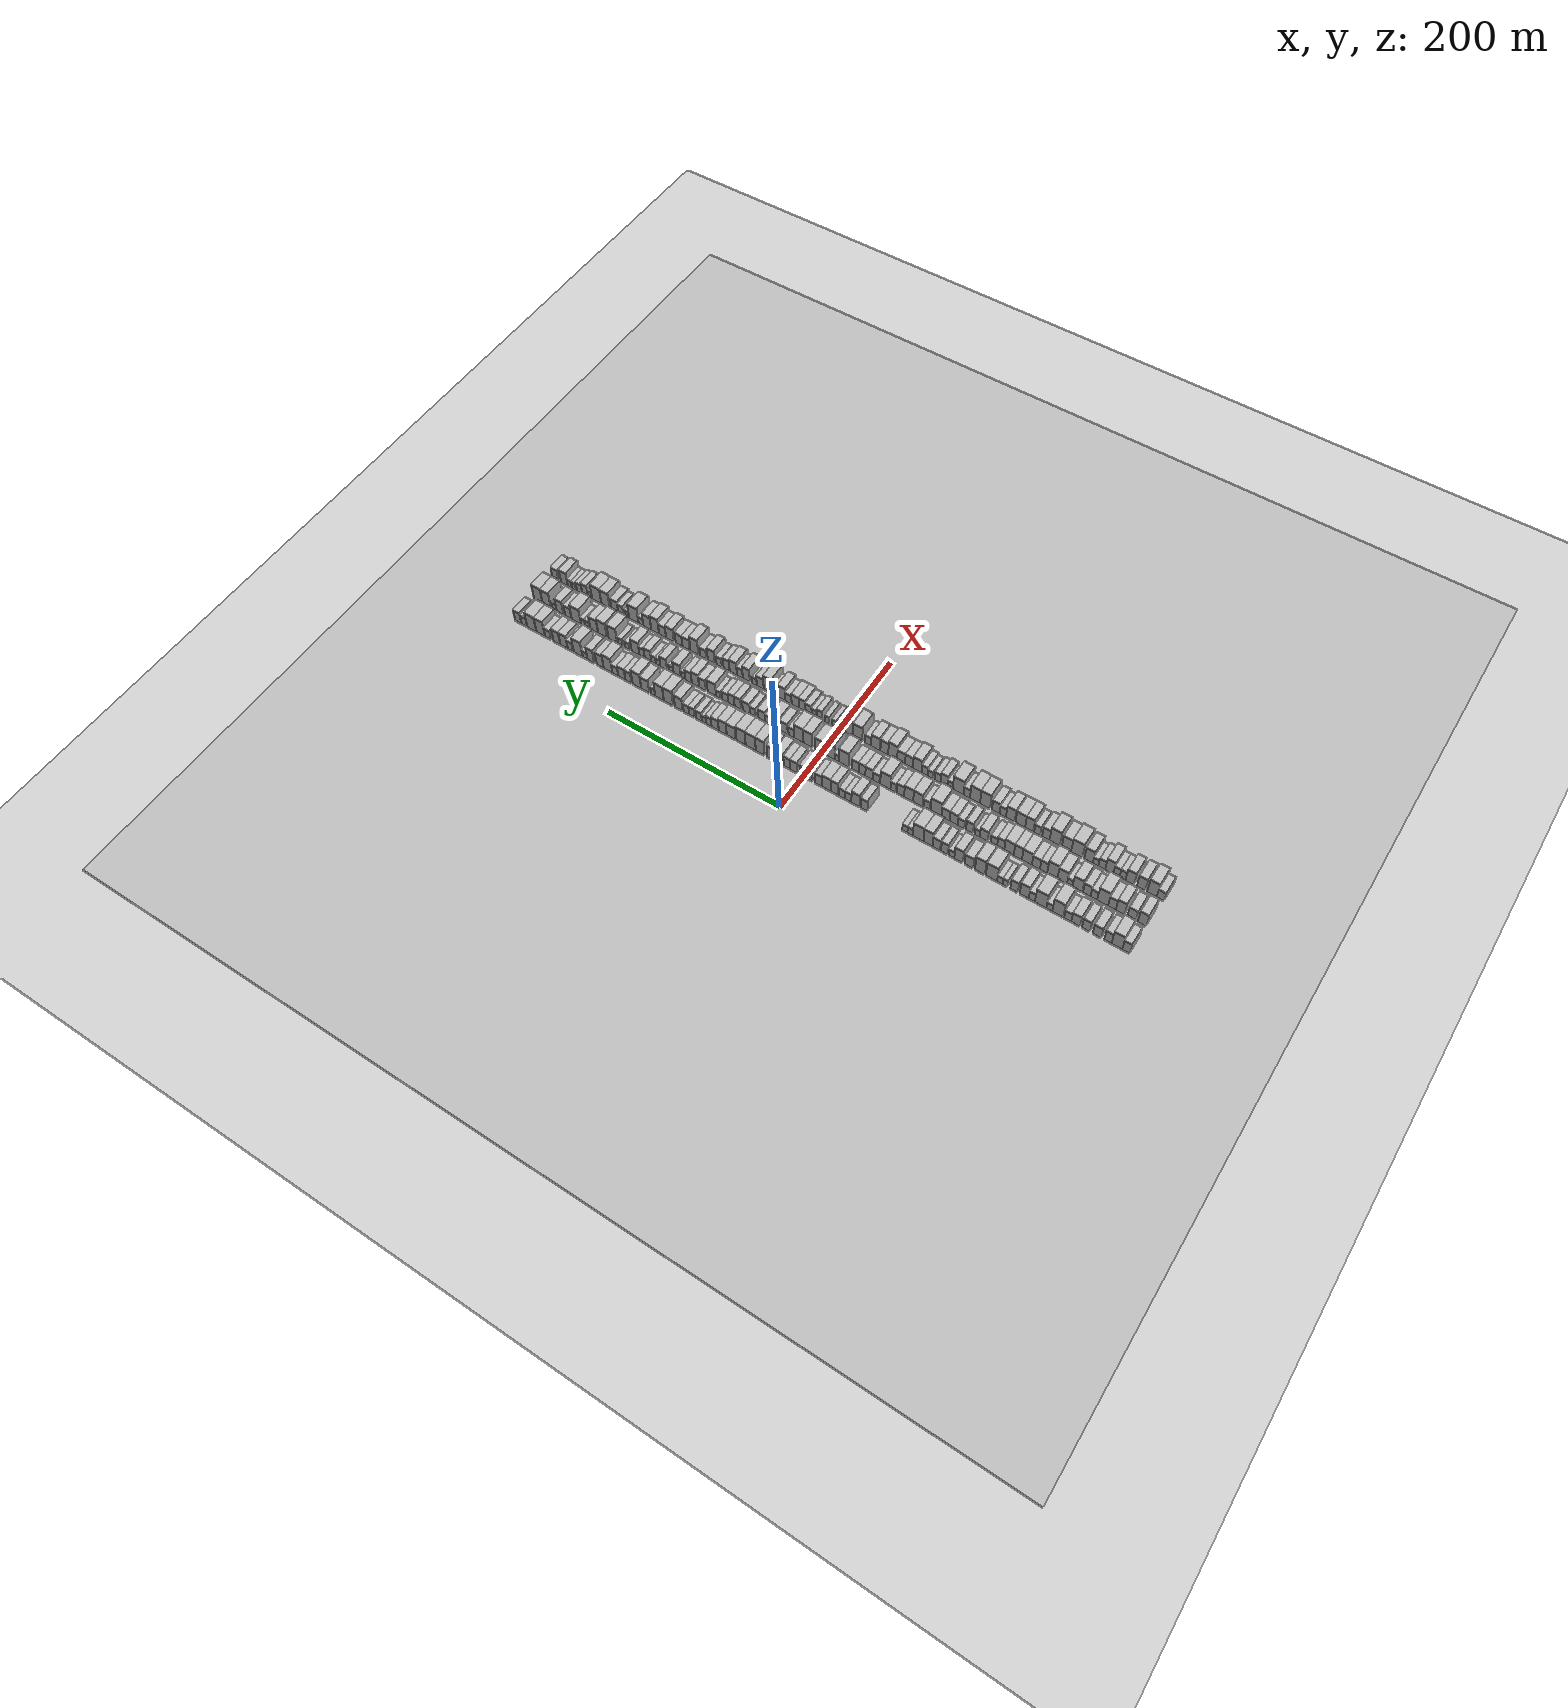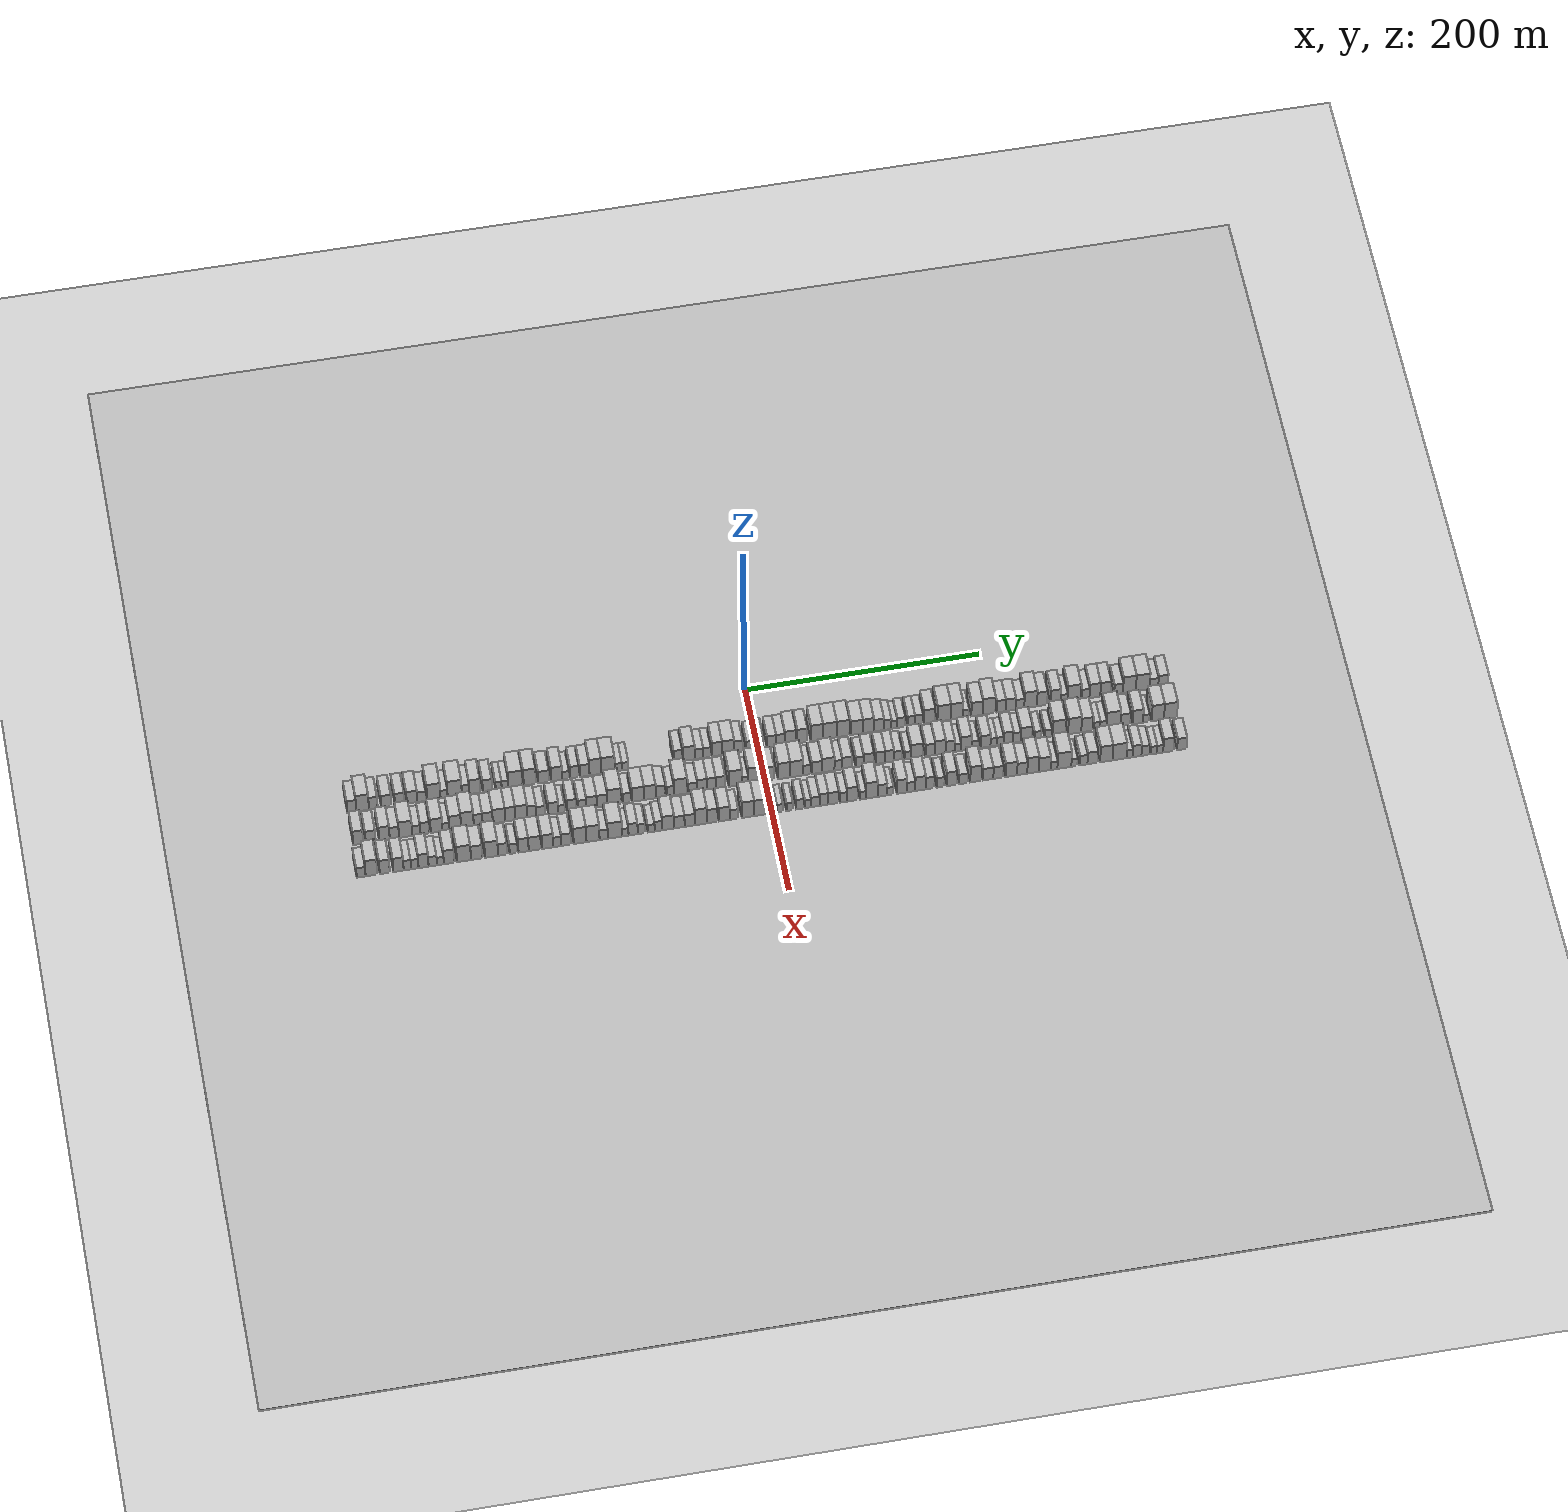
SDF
<?xml version="1.0" encoding="utf-8"?>

<sdf version="1.6">

   <world name="default">

      <gui fullscreen="0">

         <camera name="user_camera">

            <pose>-15 0 4.57585 0 0 0</pose>

            <view_controller>orbit</view_controller>

         </camera>

      </gui>

      <scene>

         <sky>

           <clouds>

             <speed>12</speed>

           </clouds>

         </sky>

         <ambient>0.4 0.4 0.4 1</ambient>

         <background>0.7 0.7 0.7 1</background>

         <shadows>1</shadows>

      </scene>

      <gravity>0 0 -9.8066</gravity>

      <magnetic_field>6e-06 2.3e-05 -4.2e-05</magnetic_field>

      <physics default="0" name="default_physics" type="ode">

         <ode>

            <solver>

               <type>quick</type>

               <iters>10</iters>

               <sor>1.0</sor>

               <use_dynamic_moi_rescaling>0</use_dynamic_moi_rescaling>

            </solver>

            <constraints>

               <cfm>0</cfm>

               <erp>0.2</erp>

               <contact_max_correcting_vel>100</contact_max_correcting_vel>

               <contact_surface_layer>0.001</contact_surface_layer>

            </constraints>

         </ode>

         <max_step_size>0.004</max_step_size>

         <real_time_factor>1</real_time_factor>

         <real_time_update_rate>250</real_time_update_rate>

      </physics>

      <light name="sun" type="directional">

         <cast_shadows>1</cast_shadows>

         <pose>0 0 10 0 0 0</pose>

         <diffuse>0.8 0.8 0.8 1</diffuse>

         <specular>0.2 0.2 0.2 1</specular>

         <attenuation>

            <range>1000</range>

            <constant>0.9</constant>

            <linear>0.01</linear>

            <quadratic>0.001</quadratic>

         </attenuation>

         <direction>-0.5 0.1 -0.9</direction>

      </light>

      <include>

         <name>ground_plane_1</name>

         <uri>model://HANNAS_ground_plane</uri>

         <pose>0 0 0  0 0 0</pose>

      </include>

      <include>

         <name>ground_plane_2</name>

         <uri>model://HANNAS_ground_plane</uri>

         <pose>100 0 0  0 0 0</pose>

      </include>

      <model name="building_1">

         <static>1</static>

         <pose frame="">50.0000 -342.2190 0 0.000000 0.000000 0.000000</pose>

         <link name="link">

            <pose frame="">0 0 9.00 0 0 0</pose>

            <collision name="collision">

               <geometry>

                  <box>

                     <size>20.0000 7.5620 18.0000</size>

                  </box>

               </geometry>

               <max_contacts>10</max_contacts>

               <surface>

                  <contact>

                     <ode/>

                  </contact>

                  <bounce/>

                  <friction>

                     <torsional>

                        <ode/>

                     </torsional>

                     <ode/>

                  </friction>

               </surface>

            </collision>

            <visual name="visual">

               <cast_shadows>0</cast_shadows>

               <geometry>

                  <box>

                     <size>20.0000 7.5620 18.0000</size>

                  </box>

               </geometry>

               <material>

                  <script>

                     <uri>model://HANNAS_wall/materials/scripts</uri>

                     <uri>model://HANNAS_wall/materials/textures</uri>

                     <name>vrc/HANNAS_wall</name>

                  </script>

               </material>

            </visual>

            <self_collide>0</self_collide>

            <enable_wind>0</enable_wind>

            <kinematic>0</kinematic>

         </link>

      </model>

      <model name="building_2">

         <static>1</static>

         <pose frame="">50.0000 -333.1310 0 0.000000 0.000000 0.000000</pose>

         <link name="link">

            <pose frame="">0 0 12.00 0 0 0</pose>

            <collision name="collision">

               <geometry>

                  <box>

                     <size>20.0000 10.6140 24.0000</size>

                  </box>

               </geometry>

               <max_contacts>10</max_contacts>

               <surface>

                  <contact>

                     <ode/>

                  </contact>

                  <bounce/>

                  <friction>

                     <torsional>

                        <ode/>

                     </torsional>

                     <ode/>

                  </friction>

               </surface>

            </collision>

            <visual name="visual">

               <cast_shadows>0</cast_shadows>

               <geometry>

                  <box>

                     <size>20.0000 10.6140 24.0000</size>

                  </box>

               </geometry>

               <material>

                  <script>

                     <uri>model://HANNAS_wall/materials/scripts</uri>

                     <uri>model://HANNAS_wall/materials/textures</uri>

                     <name>vrc/HANNAS_wall</name>

                  </script>

               </material>

            </visual>

            <self_collide>0</self_collide>

            <enable_wind>0</enable_wind>

            <kinematic>0</kinematic>

         </link>

      </model>

      <model name="building_3">

         <static>1</static>

         <pose frame="">50.0000 -324.1994 0 0.000000 0.000000 0.000000</pose>

         <link name="link">

            <pose frame="">0 0 9.00 0 0 0</pose>

            <collision name="collision">

               <geometry>

                  <box>

                     <size>20.0000 7.2493 18.0000</size>

                  </box>

               </geometry>

               <max_contacts>10</max_contacts>

               <surface>

                  <contact>

                     <ode/>

                  </contact>

                  <bounce/>

                  <friction>

                     <torsional>

                        <ode/>

                     </torsional>

                     <ode/>

                  </friction>

               </surface>

            </collision>

            <visual name="visual">

               <cast_shadows>0</cast_shadows>

               <geometry>

                  <box>

                     <size>20.0000 7.2493 18.0000</size>

                  </box>

               </geometry>

               <material>

                  <script>

                     <uri>model://HANNAS_wall/materials/scripts</uri>

                     <uri>model://HANNAS_wall/materials/textures</uri>

                     <name>vrc/HANNAS_wall</name>

                  </script>

               </material>

            </visual>

            <self_collide>0</self_collide>

            <enable_wind>0</enable_wind>

            <kinematic>0</kinematic>

         </link>

      </model>

      <model name="building_4">

         <static>1</static>

         <pose frame="">50.0000 -313.3066 0 0.000000 0.000000 0.000000</pose>

         <link name="link">

            <pose frame="">0 0 9.00 0 0 0</pose>

            <collision name="collision">

               <geometry>

                  <box>

                     <size>20.0000 8.5363 18.0000</size>

                  </box>

               </geometry>

               <max_contacts>10</max_contacts>

               <surface>

                  <contact>

                     <ode/>

                  </contact>

                  <bounce/>

                  <friction>

                     <torsional>

                        <ode/>

                     </torsional>

                     <ode/>

                  </friction>

               </surface>

            </collision>

            <visual name="visual">

               <cast_shadows>0</cast_shadows>

               <geometry>

                  <box>

                     <size>20.0000 8.5363 18.0000</size>

                  </box>

               </geometry>

               <material>

                  <script>

                     <uri>model://HANNAS_wall/materials/scripts</uri>

                     <uri>model://HANNAS_wall/materials/textures</uri>

                     <name>vrc/HANNAS_wall</name>

                  </script>

               </material>

            </visual>

            <self_collide>0</self_collide>

            <enable_wind>0</enable_wind>

            <kinematic>0</kinematic>

         </link>

      </model>

      <model name="building_5">

         <static>1</static>

         <pose frame="">50.0000 -302.0713 0 0.000000 0.000000 0.000000</pose>

         <link name="link">

            <pose frame="">0 0 9.00 0 0 0</pose>

            <collision name="collision">

               <geometry>

                  <box>

                     <size>20.0000 7.9341 18.0000</size>

                  </box>

               </geometry>

               <max_contacts>10</max_contacts>

               <surface>

                  <contact>

                     <ode/>

                  </contact>

                  <bounce/>

                  <friction>

                     <torsional>

                        <ode/>

                     </torsional>

                     <ode/>

                  </friction>

               </surface>

            </collision>

            <visual name="visual">

               <cast_shadows>0</cast_shadows>

               <geometry>

                  <box>

                     <size>20.0000 7.9341 18.0000</size>

                  </box>

               </geometry>

               <material>

                  <script>

                     <uri>model://HANNAS_wall/materials/scripts</uri>

                     <uri>model://HANNAS_wall/materials/textures</uri>

                     <name>vrc/HANNAS_wall</name>

                  </script>

               </material>

            </visual>

            <self_collide>0</self_collide>

            <enable_wind>0</enable_wind>

            <kinematic>0</kinematic>

         </link>

      </model>

      <model name="building_6">

         <static>1</static>

         <pose frame="">50.0000 -291.6735 0 0.000000 0.000000 0.000000</pose>

         <link name="link">

            <pose frame="">0 0 9.00 0 0 0</pose>

            <collision name="collision">

               <geometry>

                  <box>

                     <size>20.0000 8.8616 18.0000</size>

                  </box>

               </geometry>

               <max_contacts>10</max_contacts>

               <surface>

                  <contact>

                     <ode/>

                  </contact>

                  <bounce/>

                  <friction>

                     <torsional>

                        <ode/>

                     </torsional>

                     <ode/>

                  </friction>

               </surface>

            </collision>

            <visual name="visual">

               <cast_shadows>0</cast_shadows>

               <geometry>

                  <box>

                     <size>20.0000 8.8616 18.0000</size>

                  </box>

               </geometry>

               <material>

                  <script>

                     <uri>model://HANNAS_wall/materials/scripts</uri>

                     <uri>model://HANNAS_wall/materials/textures</uri>

                     <name>vrc/HANNAS_wall</name>

                  </script>

               </material>

            </visual>

            <self_collide>0</self_collide>

            <enable_wind>0</enable_wind>

            <kinematic>0</kinematic>

         </link>

      </model>

      <model name="building_7">

         <static>1</static>

         <pose frame="">50.0000 -283.6404 0 0.000000 0.000000 0.000000</pose>

         <link name="link">

            <pose frame="">0 0 7.50 0 0 0</pose>

            <collision name="collision">

               <geometry>

                  <box>

                     <size>20.0000 7.2044 15.0000</size>

                  </box>

               </geometry>

               <max_contacts>10</max_contacts>

               <surface>

                  <contact>

                     <ode/>

                  </contact>

                  <bounce/>

                  <friction>

                     <torsional>

                        <ode/>

                     </torsional>

                     <ode/>

                  </friction>

               </surface>

            </collision>

            <visual name="visual">

               <cast_shadows>0</cast_shadows>

               <geometry>

                  <box>

                     <size>20.0000 7.2044 15.0000</size>

                  </box>

               </geometry>

               <material>

                  <script>

                     <uri>model://HANNAS_wall/materials/scripts</uri>

                     <uri>model://HANNAS_wall/materials/textures</uri>

                     <name>vrc/HANNAS_wall</name>

                  </script>

               </material>

            </visual>

            <self_collide>0</self_collide>

            <enable_wind>0</enable_wind>

            <kinematic>0</kinematic>

         </link>

      </model>

      <model name="building_8">

         <static>1</static>

         <pose frame="">50.0000 -273.4399 0 0.000000 0.000000 0.000000</pose>

         <link name="link">

            <pose frame="">0 0 12.00 0 0 0</pose>

            <collision name="collision">

               <geometry>

                  <box>

                     <size>20.0000 11.1966 24.0000</size>

                  </box>

               </geometry>

               <max_contacts>10</max_contacts>

               <surface>

                  <contact>

                     <ode/>

                  </contact>

                  <bounce/>

                  <friction>

                     <torsional>

                        <ode/>

                     </torsional>

                     <ode/>

                  </friction>

               </surface>

            </collision>

            <visual name="visual">

               <cast_shadows>0</cast_shadows>

               <geometry>

                  <box>

                     <size>20.0000 11.1966 24.0000</size>

                  </box>

               </geometry>

               <material>

                  <script>

                     <uri>model://HANNAS_wall/materials/scripts</uri>

                     <uri>model://HANNAS_wall/materials/textures</uri>

                     <name>vrc/HANNAS_wall</name>

                  </script>

               </material>

            </visual>

            <self_collide>0</self_collide>

            <enable_wind>0</enable_wind>

            <kinematic>0</kinematic>

         </link>

      </model>

      <model name="building_9">

         <static>1</static>

         <pose frame="">50.0000 -264.8591 0 0.000000 0.000000 0.000000</pose>

         <link name="link">

            <pose frame="">0 0 6.00 0 0 0</pose>

            <collision name="collision">

               <geometry>

                  <box>

                     <size>20.0000 5.9650 12.0000</size>

                  </box>

               </geometry>

               <max_contacts>10</max_contacts>

               <surface>

                  <contact>

                     <ode/>

                  </contact>

                  <bounce/>

                  <friction>

                     <torsional>

                        <ode/>

                     </torsional>

                     <ode/>

                  </friction>

               </surface>

            </collision>

            <visual name="visual">

               <cast_shadows>0</cast_shadows>

               <geometry>

                  <box>

                     <size>20.0000 5.9650 12.0000</size>

                  </box>

               </geometry>

               <material>

                  <script>

                     <uri>model://HANNAS_wall/materials/scripts</uri>

                     <uri>model://HANNAS_wall/materials/textures</uri>

                     <name>vrc/HANNAS_wall</name>

                  </script>

               </material>

            </visual>

            <self_collide>0</self_collide>

            <enable_wind>0</enable_wind>

            <kinematic>0</kinematic>

         </link>

      </model>

      <model name="building_10">

         <static>1</static>

         <pose frame="">50.0000 -255.8999 0 0.000000 0.000000 0.000000</pose>

         <link name="link">

            <pose frame="">0 0 12.00 0 0 0</pose>

            <collision name="collision">

               <geometry>

                  <box>

                     <size>20.0000 11.9535 24.0000</size>

                  </box>

               </geometry>

               <max_contacts>10</max_contacts>

               <surface>

                  <contact>

                     <ode/>

                  </contact>

                  <bounce/>

                  <friction>

                     <torsional>

                        <ode/>

                     </torsional>

                     <ode/>

                  </friction>

               </surface>

            </collision>

            <visual name="visual">

               <cast_shadows>0</cast_shadows>

               <geometry>

                  <box>

                     <size>20.0000 11.9535 24.0000</size>

                  </box>

               </geometry>

               <material>

                  <script>

                     <uri>model://HANNAS_wall/materials/scripts</uri>

                     <uri>model://HANNAS_wall/materials/textures</uri>

                     <name>vrc/HANNAS_wall</name>

                  </script>

               </material>

            </visual>

            <self_collide>0</self_collide>

            <enable_wind>0</enable_wind>

            <kinematic>0</kinematic>

         </link>

      </model>

      <model name="building_11">

         <static>1</static>

         <pose frame="">50.0000 -246.7564 0 0.000000 0.000000 0.000000</pose>

         <link name="link">

            <pose frame="">0 0 7.50 0 0 0</pose>

            <collision name="collision">

               <geometry>

                  <box>

                     <size>20.0000 6.3335 15.0000</size>

                  </box>

               </geometry>

               <max_contacts>10</max_contacts>

               <surface>

                  <contact>

                     <ode/>

                  </contact>

                  <bounce/>

                  <friction>

                     <torsional>

                        <ode/>

                     </torsional>

                     <ode/>

                  </friction>

               </surface>

            </collision>

            <visual name="visual">

               <cast_shadows>0</cast_shadows>

               <geometry>

                  <box>

                     <size>20.0000 6.3335 15.0000</size>

                  </box>

               </geometry>

               <material>

                  <script>

                     <uri>model://HANNAS_wall/materials/scripts</uri>

                     <uri>model://HANNAS_wall/materials/textures</uri>

                     <name>vrc/HANNAS_wall</name>

                  </script>

               </material>

            </visual>

            <self_collide>0</self_collide>

            <enable_wind>0</enable_wind>

            <kinematic>0</kinematic>

         </link>

      </model>

      <model name="building_12">

         <static>1</static>

         <pose frame="">50.0000 -238.9504 0 0.000000 0.000000 0.000000</pose>

         <link name="link">

            <pose frame="">0 0 10.50 0 0 0</pose>

            <collision name="collision">

               <geometry>

                  <box>

                     <size>20.0000 9.2785 21.0000</size>

                  </box>

               </geometry>

               <max_contacts>10</max_contacts>

               <surface>

                  <contact>

                     <ode/>

                  </contact>

                  <bounce/>

                  <friction>

                     <torsional>

                        <ode/>

                     </torsional>

                     <ode/>

                  </friction>

               </surface>

            </collision>

            <visual name="visual">

               <cast_shadows>0</cast_shadows>

               <geometry>

                  <box>

                     <size>20.0000 9.2785 21.0000</size>

                  </box>

               </geometry>

               <material>

                  <script>

                     <uri>model://HANNAS_wall/materials/scripts</uri>

                     <uri>model://HANNAS_wall/materials/textures</uri>

                     <name>vrc/HANNAS_wall</name>

                  </script>

               </material>

            </visual>

            <self_collide>0</self_collide>

            <enable_wind>0</enable_wind>

            <kinematic>0</kinematic>

         </link>

      </model>

      <model name="building_13">

         <static>1</static>

         <pose frame="">50.0000 -228.4290 0 0.000000 0.000000 0.000000</pose>

         <link name="link">

            <pose frame="">0 0 9.00 0 0 0</pose>

            <collision name="collision">

               <geometry>

                  <box>

                     <size>20.0000 7.7644 18.0000</size>

                  </box>

               </geometry>

               <max_contacts>10</max_contacts>

               <surface>

                  <contact>

                     <ode/>

                  </contact>

                  <bounce/>

                  <friction>

                     <torsional>

                        <ode/>

                     </torsional>

                     <ode/>

                  </friction>

               </surface>

            </collision>

            <visual name="visual">

               <cast_shadows>0</cast_shadows>

               <geometry>

                  <box>

                     <size>20.0000 7.7644 18.0000</size>

                  </box>

               </geometry>

               <material>

                  <script>

                     <uri>model://HANNAS_wall/materials/scripts</uri>

                     <uri>model://HANNAS_wall/materials/textures</uri>

                     <name>vrc/HANNAS_wall</name>

                  </script>

               </material>

            </visual>

            <self_collide>0</self_collide>

            <enable_wind>0</enable_wind>

            <kinematic>0</kinematic>

         </link>

      </model>

      <model name="building_14">

         <static>1</static>

         <pose frame="">50.0000 -219.0100 0 0.000000 0.000000 0.000000</pose>

         <link name="link">

            <pose frame="">0 0 6.00 0 0 0</pose>

            <collision name="collision">

               <geometry>

                  <box>

                     <size>20.0000 5.0735 12.0000</size>

                  </box>

               </geometry>

               <max_contacts>10</max_contacts>

               <surface>

                  <contact>

                     <ode/>

                  </contact>

                  <bounce/>

                  <friction>

                     <torsional>

                        <ode/>

                     </torsional>

                     <ode/>

                  </friction>

               </surface>

            </collision>

            <visual name="visual">

               <cast_shadows>0</cast_shadows>

               <geometry>

                  <box>

                     <size>20.0000 5.0735 12.0000</size>

                  </box>

               </geometry>

               <material>

                  <script>

                     <uri>model://HANNAS_wall/materials/scripts</uri>

                     <uri>model://HANNAS_wall/materials/textures</uri>

                     <name>vrc/HANNAS_wall</name>

                  </script>

               </material>

            </visual>

            <self_collide>0</self_collide>

            <enable_wind>0</enable_wind>

            <kinematic>0</kinematic>

         </link>

      </model>

      <model name="building_15">

         <static>1</static>

         <pose frame="">50.0000 -213.6350 0 0.000000 0.000000 0.000000</pose>

         <link name="link">

            <pose frame="">0 0 6.00 0 0 0</pose>

            <collision name="collision">

               <geometry>

                  <box>

                     <size>20.0000 5.6767 12.0000</size>

                  </box>

               </geometry>

               <max_contacts>10</max_contacts>

               <surface>

                  <contact>

                     <ode/>

                  </contact>

                  <bounce/>

                  <friction>

                     <torsional>

                        <ode/>

                     </torsional>

                     <ode/>

                  </friction>

               </surface>

            </collision>

            <visual name="visual">

               <cast_shadows>0</cast_shadows>

               <geometry>

                  <box>

                     <size>20.0000 5.6767 12.0000</size>

                  </box>

               </geometry>

               <material>

                  <script>

                     <uri>model://HANNAS_wall/materials/scripts</uri>

                     <uri>model://HANNAS_wall/materials/textures</uri>

                     <name>vrc/HANNAS_wall</name>

                  </script>

               </material>

            </visual>

            <self_collide>0</self_collide>

            <enable_wind>0</enable_wind>

            <kinematic>0</kinematic>

         </link>

      </model>

      <model name="building_16">

         <static>1</static>

         <pose frame="">50.0000 -204.8736 0 0.000000 0.000000 0.000000</pose>

         <link name="link">

            <pose frame="">0 0 12.00 0 0 0</pose>

            <collision name="collision">

               <geometry>

                  <box>

                     <size>20.0000 11.8460 24.0000</size>

                  </box>

               </geometry>

               <max_contacts>10</max_contacts>

               <surface>

                  <contact>

                     <ode/>

                  </contact>

                  <bounce/>

                  <friction>

                     <torsional>

                        <ode/>

                     </torsional>

                     <ode/>

                  </friction>

               </surface>

            </collision>

            <visual name="visual">

               <cast_shadows>0</cast_shadows>

               <geometry>

                  <box>

                     <size>20.0000 11.8460 24.0000</size>

                  </box>

               </geometry>

               <material>

                  <script>

                     <uri>model://HANNAS_wall/materials/scripts</uri>

                     <uri>model://HANNAS_wall/materials/textures</uri>

                     <name>vrc/HANNAS_wall</name>

                  </script>

               </material>

            </visual>

            <self_collide>0</self_collide>

            <enable_wind>0</enable_wind>

            <kinematic>0</kinematic>

         </link>

      </model>

      <model name="building_17">

         <static>1</static>

         <pose frame="">50.0000 -192.7813 0 0.000000 0.000000 0.000000</pose>

         <link name="link">

            <pose frame="">0 0 12.00 0 0 0</pose>

            <collision name="collision">

               <geometry>

                  <box>

                     <size>20.0000 10.3386 24.0000</size>

                  </box>

               </geometry>

               <max_contacts>10</max_contacts>

               <surface>

                  <contact>

                     <ode/>

                  </contact>

                  <bounce/>

                  <friction>

                     <torsional>

                        <ode/>

                     </torsional>

                     <ode/>

                  </friction>

               </surface>

            </collision>

            <visual name="visual">

               <cast_shadows>0</cast_shadows>

               <geometry>

                  <box>

                     <size>20.0000 10.3386 24.0000</size>

                  </box>

               </geometry>

               <material>

                  <script>

                     <uri>model://HANNAS_wall/materials/scripts</uri>

                     <uri>model://HANNAS_wall/materials/textures</uri>

                     <name>vrc/HANNAS_wall</name>

                  </script>

               </material>

            </visual>

            <self_collide>0</self_collide>

            <enable_wind>0</enable_wind>

            <kinematic>0</kinematic>

         </link>

      </model>

      <model name="building_18">

         <static>1</static>

         <pose frame="">50.0000 -181.1529 0 0.000000 0.000000 0.000000</pose>

         <link name="link">

            <pose frame="">0 0 9.00 0 0 0</pose>

            <collision name="collision">

               <geometry>

                  <box>

                     <size>20.0000 8.9184 18.0000</size>

                  </box>

               </geometry>

               <max_contacts>10</max_contacts>

               <surface>

                  <contact>

                     <ode/>

                  </contact>

                  <bounce/>

                  <friction>

                     <torsional>

                        <ode/>

                     </torsional>

                     <ode/>

                  </friction>

               </surface>

            </collision>

            <visual name="visual">

               <cast_shadows>0</cast_shadows>

               <geometry>

                  <box>

                     <size>20.0000 8.9184 18.0000</size>

                  </box>

               </geometry>

               <material>

                  <script>

                     <uri>model://HANNAS_wall/materials/scripts</uri>

                     <uri>model://HANNAS_wall/materials/textures</uri>

                     <name>vrc/HANNAS_wall</name>

                  </script>

               </material>

            </visual>

            <self_collide>0</self_collide>

            <enable_wind>0</enable_wind>

            <kinematic>0</kinematic>

         </link>

      </model>

      <model name="building_19">

         <static>1</static>

         <pose frame="">50.0000 -170.1867 0 0.000000 0.000000 0.000000</pose>

         <link name="link">

            <pose frame="">0 0 10.50 0 0 0</pose>

            <collision name="collision">

               <geometry>

                  <box>

                     <size>20.0000 9.0140 21.0000</size>

                  </box>

               </geometry>

               <max_contacts>10</max_contacts>

               <surface>

                  <contact>

                     <ode/>

                  </contact>

                  <bounce/>

                  <friction>

                     <torsional>

                        <ode/>

                     </torsional>

                     <ode/>

                  </friction>

               </surface>

            </collision>

            <visual name="visual">

               <cast_shadows>0</cast_shadows>

               <geometry>

                  <box>

                     <size>20.0000 9.0140 21.0000</size>

                  </box>

               </geometry>

               <material>

                  <script>

                     <uri>model://HANNAS_wall/materials/scripts</uri>

                     <uri>model://HANNAS_wall/materials/textures</uri>

                     <name>vrc/HANNAS_wall</name>

                  </script>

               </material>

            </visual>

            <self_collide>0</self_collide>

            <enable_wind>0</enable_wind>

            <kinematic>0</kinematic>

         </link>

      </model>

      <model name="building_20">

         <static>1</static>

         <pose frame="">50.0000 -162.6998 0 0.000000 0.000000 0.000000</pose>

         <link name="link">

            <pose frame="">0 0 6.00 0 0 0</pose>

            <collision name="collision">

               <geometry>

                  <box>

                     <size>20.0000 5.9597 12.0000</size>

                  </box>

               </geometry>

               <max_contacts>10</max_contacts>

               <surface>

                  <contact>

                     <ode/>

                  </contact>

                  <bounce/>

                  <friction>

                     <torsional>

                        <ode/>

                     </torsional>

                     <ode/>

                  </friction>

               </surface>

            </collision>

            <visual name="visual">

               <cast_shadows>0</cast_shadows>

               <geometry>

                  <box>

                     <size>20.0000 5.9597 12.0000</size>

                  </box>

               </geometry>

               <material>

                  <script>

                     <uri>model://HANNAS_wall/materials/scripts</uri>

                     <uri>model://HANNAS_wall/materials/textures</uri>

                     <name>vrc/HANNAS_wall</name>

                  </script>

               </material>

            </visual>

            <self_collide>0</self_collide>

            <enable_wind>0</enable_wind>

            <kinematic>0</kinematic>

         </link>

      </model>

      <model name="building_21">

         <static>1</static>

         <pose frame="">50.0000 -155.1052 0 0.000000 0.000000 0.000000</pose>

         <link name="link">

            <pose frame="">0 0 9.00 0 0 0</pose>

            <collision name="collision">

               <geometry>

                  <box>

                     <size>20.0000 7.2296 18.0000</size>

                  </box>

               </geometry>

               <max_contacts>10</max_contacts>

               <surface>

                  <contact>

                     <ode/>

                  </contact>

                  <bounce/>

                  <friction>

                     <torsional>

                        <ode/>

                     </torsional>

                     <ode/>

                  </friction>

               </surface>

            </collision>

            <visual name="visual">

               <cast_shadows>0</cast_shadows>

               <geometry>

                  <box>

                     <size>20.0000 7.2296 18.0000</size>

                  </box>

               </geometry>

               <material>

                  <script>

                     <uri>model://HANNAS_wall/materials/scripts</uri>

                     <uri>model://HANNAS_wall/materials/textures</uri>

                     <name>vrc/HANNAS_wall</name>

                  </script>

               </material>

            </visual>

            <self_collide>0</self_collide>

            <enable_wind>0</enable_wind>

            <kinematic>0</kinematic>

         </link>

      </model>

      <model name="building_22">

         <static>1</static>

         <pose frame="">50.0000 -146.5102 0 0.000000 0.000000 0.000000</pose>

         <link name="link">

            <pose frame="">0 0 9.00 0 0 0</pose>

            <collision name="collision">

               <geometry>

                  <box>

                     <size>20.0000 7.9605 18.0000</size>

                  </box>

               </geometry>

               <max_contacts>10</max_contacts>

               <surface>

                  <contact>

                     <ode/>

                  </contact>

                  <bounce/>

                  <friction>

                     <torsional>

                        <ode/>

                     </torsional>

                     <ode/>

                  </friction>

               </surface>

            </collision>

            <visual name="visual">

               <cast_shadows>0</cast_shadows>

               <geometry>

                  <box>

                     <size>20.0000 7.9605 18.0000</size>

                  </box>

               </geometry>

               <material>

                  <script>

                     <uri>model://HANNAS_wall/materials/scripts</uri>

                     <uri>model://HANNAS_wall/materials/textures</uri>

                     <name>vrc/HANNAS_wall</name>

                  </script>

               </material>

            </visual>

            <self_collide>0</self_collide>

            <enable_wind>0</enable_wind>

            <kinematic>0</kinematic>

         </link>

      </model>

      <model name="building_23">

         <static>1</static>

         <pose frame="">50.0000 -137.6101 0 0.000000 0.000000 0.000000</pose>

         <link name="link">

            <pose frame="">0 0 12.00 0 0 0</pose>

            <collision name="collision">

               <geometry>

                  <box>

                     <size>20.0000 9.8397 24.0000</size>

                  </box>

               </geometry>

               <max_contacts>10</max_contacts>

               <surface>

                  <contact>

                     <ode/>

                  </contact>

                  <bounce/>

                  <friction>

                     <torsional>

                        <ode/>

                     </torsional>

                     <ode/>

                  </friction>

               </surface>

            </collision>

            <visual name="visual">

               <cast_shadows>0</cast_shadows>

               <geometry>

                  <box>

                     <size>20.0000 9.8397 24.0000</size>

                  </box>

               </geometry>

               <material>

                  <script>

                     <uri>model://HANNAS_wall/materials/scripts</uri>

                     <uri>model://HANNAS_wall/materials/textures</uri>

                     <name>vrc/HANNAS_wall</name>

                  </script>

               </material>

            </visual>

            <self_collide>0</self_collide>

            <enable_wind>0</enable_wind>

            <kinematic>0</kinematic>

         </link>

      </model>

      <model name="building_24">

         <static>1</static>

         <pose frame="">50.0000 -126.9382 0 0.000000 0.000000 0.000000</pose>

         <link name="link">

            <pose frame="">0 0 12.00 0 0 0</pose>

            <collision name="collision">

               <geometry>

                  <box>

                     <size>20.0000 11.5041 24.0000</size>

                  </box>

               </geometry>

               <max_contacts>10</max_contacts>

               <surface>

                  <contact>

                     <ode/>

                  </contact>

                  <bounce/>

                  <friction>

                     <torsional>

                        <ode/>

                     </torsional>

                     <ode/>

                  </friction>

               </surface>

            </collision>

            <visual name="visual">

               <cast_shadows>0</cast_shadows>

               <geometry>

                  <box>

                     <size>20.0000 11.5041 24.0000</size>

                  </box>

               </geometry>

               <material>

                  <script>

                     <uri>model://HANNAS_wall/materials/scripts</uri>

                     <uri>model://HANNAS_wall/materials/textures</uri>

                     <name>vrc/HANNAS_wall</name>

                  </script>

               </material>

            </visual>

            <self_collide>0</self_collide>

            <enable_wind>0</enable_wind>

            <kinematic>0</kinematic>

         </link>

      </model>

      <model name="building_25">

         <static>1</static>

         <pose frame="">50.0000 -118.1877 0 0.000000 0.000000 0.000000</pose>

         <link name="link">

            <pose frame="">0 0 6.00 0 0 0</pose>

            <collision name="collision">

               <geometry>

                  <box>

                     <size>20.0000 5.9968 12.0000</size>

                  </box>

               </geometry>

               <max_contacts>10</max_contacts>

               <surface>

                  <contact>

                     <ode/>

                  </contact>

                  <bounce/>

                  <friction>

                     <torsional>

                        <ode/>

                     </torsional>

                     <ode/>

                  </friction>

               </surface>

            </collision>

            <visual name="visual">

               <cast_shadows>0</cast_shadows>

               <geometry>

                  <box>

                     <size>20.0000 5.9968 12.0000</size>

                  </box>

               </geometry>

               <material>

                  <script>

                     <uri>model://HANNAS_wall/materials/scripts</uri>

                     <uri>model://HANNAS_wall/materials/textures</uri>

                     <name>vrc/HANNAS_wall</name>

                  </script>

               </material>

            </visual>

            <self_collide>0</self_collide>

            <enable_wind>0</enable_wind>

            <kinematic>0</kinematic>

         </link>

      </model>

      <model name="building_26">

         <static>1</static>

         <pose frame="">50.0000 -112.4463 0 0.000000 0.000000 0.000000</pose>

         <link name="link">

            <pose frame="">0 0 6.00 0 0 0</pose>

            <collision name="collision">

               <geometry>

                  <box>

                     <size>20.0000 5.4861 12.0000</size>

                  </box>

               </geometry>

               <max_contacts>10</max_contacts>

               <surface>

                  <contact>

                     <ode/>

                  </contact>

                  <bounce/>

                  <friction>

                     <torsional>

                        <ode/>

                     </torsional>

                     <ode/>

                  </friction>

               </surface>

            </collision>

            <visual name="visual">

               <cast_shadows>0</cast_shadows>

               <geometry>

                  <box>

                     <size>20.0000 5.4861 12.0000</size>

                  </box>

               </geometry>

               <material>

                  <script>

                     <uri>model://HANNAS_wall/materials/scripts</uri>

                     <uri>model://HANNAS_wall/materials/textures</uri>

                     <name>vrc/HANNAS_wall</name>

                  </script>

               </material>

            </visual>

            <self_collide>0</self_collide>

            <enable_wind>0</enable_wind>

            <kinematic>0</kinematic>

         </link>

      </model>

      <model name="building_27">

         <static>1</static>

         <pose frame="">50.0000 -67.8716 0 0.000000 0.000000 0.000000</pose>

         <link name="link">

            <pose frame="">0 0 9.00 0 0 0</pose>

            <collision name="collision">

               <geometry>

                  <box>

                     <size>20.0000 7.2211 18.0000</size>

                  </box>

               </geometry>

               <max_contacts>10</max_contacts>

               <surface>

                  <contact>

                     <ode/>

                  </contact>

                  <bounce/>

                  <friction>

                     <torsional>

                        <ode/>

                     </torsional>

                     <ode/>

                  </friction>

               </surface>

            </collision>

            <visual name="visual">

               <cast_shadows>0</cast_shadows>

               <geometry>

                  <box>

                     <size>20.0000 7.2211 18.0000</size>

                  </box>

               </geometry>

               <material>

                  <script>

                     <uri>model://HANNAS_wall/materials/scripts</uri>

                     <uri>model://HANNAS_wall/materials/textures</uri>

                     <name>vrc/HANNAS_wall</name>

                  </script>

               </material>

            </visual>

            <self_collide>0</self_collide>

            <enable_wind>0</enable_wind>

            <kinematic>0</kinematic>

         </link>

      </model>

      <model name="building_28">

         <static>1</static>

         <pose frame="">50.0000 -58.4912 0 0.000000 0.000000 0.000000</pose>

         <link name="link">

            <pose frame="">0 0 10.50 0 0 0</pose>

            <collision name="collision">

               <geometry>

                  <box>

                     <size>20.0000 9.5399 21.0000</size>

                  </box>

               </geometry>

               <max_contacts>10</max_contacts>

               <surface>

                  <contact>

                     <ode/>

                  </contact>

                  <bounce/>

                  <friction>

                     <torsional>

                        <ode/>

                     </torsional>

                     <ode/>

                  </friction>

               </surface>

            </collision>

            <visual name="visual">

               <cast_shadows>0</cast_shadows>

               <geometry>

                  <box>

                     <size>20.0000 9.5399 21.0000</size>

                  </box>

               </geometry>

               <material>

                  <script>

                     <uri>model://HANNAS_wall/materials/scripts</uri>

                     <uri>model://HANNAS_wall/materials/textures</uri>

                     <name>vrc/HANNAS_wall</name>

                  </script>

               </material>

            </visual>

            <self_collide>0</self_collide>

            <enable_wind>0</enable_wind>

            <kinematic>0</kinematic>

         </link>

      </model>

      <model name="building_29">

         <static>1</static>

         <pose frame="">50.0000 -50.1089 0 0.000000 0.000000 0.000000</pose>

         <link name="link">

            <pose frame="">0 0 7.50 0 0 0</pose>

            <collision name="collision">

               <geometry>

                  <box>

                     <size>20.0000 7.2247 15.0000</size>

                  </box>

               </geometry>

               <max_contacts>10</max_contacts>

               <surface>

                  <contact>

                     <ode/>

                  </contact>

                  <bounce/>

                  <friction>

                     <torsional>

                        <ode/>

                     </torsional>

                     <ode/>

                  </friction>

               </surface>

            </collision>

            <visual name="visual">

               <cast_shadows>0</cast_shadows>

               <geometry>

                  <box>

                     <size>20.0000 7.2247 15.0000</size>

                  </box>

               </geometry>

               <material>

                  <script>

                     <uri>model://HANNAS_wall/materials/scripts</uri>

                     <uri>model://HANNAS_wall/materials/textures</uri>

                     <name>vrc/HANNAS_wall</name>

                  </script>

               </material>

            </visual>

            <self_collide>0</self_collide>

            <enable_wind>0</enable_wind>

            <kinematic>0</kinematic>

         </link>

      </model>

      <model name="building_30">

         <static>1</static>

         <pose frame="">50.0000 -43.3192 0 0.000000 0.000000 0.000000</pose>

         <link name="link">

            <pose frame="">0 0 7.50 0 0 0</pose>

            <collision name="collision">

               <geometry>

                  <box>

                     <size>20.0000 6.3545 15.0000</size>

                  </box>

               </geometry>

               <max_contacts>10</max_contacts>

               <surface>

                  <contact>

                     <ode/>

                  </contact>

                  <bounce/>

                  <friction>

                     <torsional>

                        <ode/>

                     </torsional>

                     <ode/>

                  </friction>

               </surface>

            </collision>

            <visual name="visual">

               <cast_shadows>0</cast_shadows>

               <geometry>

                  <box>

                     <size>20.0000 6.3545 15.0000</size>

                  </box>

               </geometry>

               <material>

                  <script>

                     <uri>model://HANNAS_wall/materials/scripts</uri>

                     <uri>model://HANNAS_wall/materials/textures</uri>

                     <name>vrc/HANNAS_wall</name>

                  </script>

               </material>

            </visual>

            <self_collide>0</self_collide>

            <enable_wind>0</enable_wind>

            <kinematic>0</kinematic>

         </link>

      </model>

      <model name="building_31">

         <static>1</static>

         <pose frame="">50.0000 -34.8919 0 0.000000 0.000000 0.000000</pose>

         <link name="link">

            <pose frame="">0 0 10.50 0 0 0</pose>

            <collision name="collision">

               <geometry>

                  <box>

                     <size>20.0000 8.5002 21.0000</size>

                  </box>

               </geometry>

               <max_contacts>10</max_contacts>

               <surface>

                  <contact>

                     <ode/>

                  </contact>

                  <bounce/>

                  <friction>

                     <torsional>

                        <ode/>

                     </torsional>

                     <ode/>

                  </friction>

               </surface>

            </collision>

            <visual name="visual">

               <cast_shadows>0</cast_shadows>

               <geometry>

                  <box>

                     <size>20.0000 8.5002 21.0000</size>

                  </box>

               </geometry>

               <material>

                  <script>

                     <uri>model://HANNAS_wall/materials/scripts</uri>

                     <uri>model://HANNAS_wall/materials/textures</uri>

                     <name>vrc/HANNAS_wall</name>

                  </script>

               </material>

            </visual>

            <self_collide>0</self_collide>

            <enable_wind>0</enable_wind>

            <kinematic>0</kinematic>

         </link>

      </model>

      <model name="building_32">

         <static>1</static>

         <pose frame="">50.0000 -25.5325 0 0.000000 0.000000 0.000000</pose>

         <link name="link">

            <pose frame="">0 0 10.50 0 0 0</pose>

            <collision name="collision">

               <geometry>

                  <box>

                     <size>20.0000 10.2185 21.0000</size>

                  </box>

               </geometry>

               <max_contacts>10</max_contacts>

               <surface>

                  <contact>

                     <ode/>

                  </contact>

                  <bounce/>

                  <friction>

                     <torsional>

                        <ode/>

                     </torsional>

                     <ode/>

                  </friction>

               </surface>

            </collision>

            <visual name="visual">

               <cast_shadows>0</cast_shadows>

               <geometry>

                  <box>

                     <size>20.0000 10.2185 21.0000</size>

                  </box>

               </geometry>

               <material>

                  <script>

                     <uri>model://HANNAS_wall/materials/scripts</uri>

                     <uri>model://HANNAS_wall/materials/textures</uri>

                     <name>vrc/HANNAS_wall</name>

                  </script>

               </material>

            </visual>

            <self_collide>0</self_collide>

            <enable_wind>0</enable_wind>

            <kinematic>0</kinematic>

         </link>

      </model>

      <model name="building_33">

         <static>1</static>

         <pose frame="">50.0000 -16.8051 0 0.000000 0.000000 0.000000</pose>

         <link name="link">

            <pose frame="">0 0 9.00 0 0 0</pose>

            <collision name="collision">

               <geometry>

                  <box>

                     <size>20.0000 7.2364 18.0000</size>

                  </box>

               </geometry>

               <max_contacts>10</max_contacts>

               <surface>

                  <contact>

                     <ode/>

                  </contact>

                  <bounce/>

                  <friction>

                     <torsional>

                        <ode/>

                     </torsional>

                     <ode/>

                  </friction>

               </surface>

            </collision>

            <visual name="visual">

               <cast_shadows>0</cast_shadows>

               <geometry>

                  <box>

                     <size>20.0000 7.2364 18.0000</size>

                  </box>

               </geometry>

               <material>

                  <script>

                     <uri>model://HANNAS_wall/materials/scripts</uri>

                     <uri>model://HANNAS_wall/materials/textures</uri>

                     <name>vrc/HANNAS_wall</name>

                  </script>

               </material>

            </visual>

            <self_collide>0</self_collide>

            <enable_wind>0</enable_wind>

            <kinematic>0</kinematic>

         </link>

      </model>

      <model name="building_34">

         <static>1</static>

         <pose frame="">50.0000 -6.7239 0 0.000000 0.000000 0.000000</pose>

         <link name="link">

            <pose frame="">0 0 7.50 0 0 0</pose>

            <collision name="collision">

               <geometry>

                  <box>

                     <size>20.0000 6.9261 15.0000</size>

                  </box>

               </geometry>

               <max_contacts>10</max_contacts>

               <surface>

                  <contact>

                     <ode/>

                  </contact>

                  <bounce/>

                  <friction>

                     <torsional>

                        <ode/>

                     </torsional>

                     <ode/>

                  </friction>

               </surface>

            </collision>

            <visual name="visual">

               <cast_shadows>0</cast_shadows>

               <geometry>

                  <box>

                     <size>20.0000 6.9261 15.0000</size>

                  </box>

               </geometry>

               <material>

                  <script>

                     <uri>model://HANNAS_wall/materials/scripts</uri>

                     <uri>model://HANNAS_wall/materials/textures</uri>

                     <name>vrc/HANNAS_wall</name>

                  </script>

               </material>

            </visual>

            <self_collide>0</self_collide>

            <enable_wind>0</enable_wind>

            <kinematic>0</kinematic>

         </link>

      </model>

      <model name="building_35">

         <static>1</static>

         <pose frame="">50.0000 0.5221 0 0.000000 0.000000 0.000000</pose>

         <link name="link">

            <pose frame="">0 0 9.00 0 0 0</pose>

            <collision name="collision">

               <geometry>

                  <box>

                     <size>20.0000 7.5658 18.0000</size>

                  </box>

               </geometry>

               <max_contacts>10</max_contacts>

               <surface>

                  <contact>

                     <ode/>

                  </contact>

                  <bounce/>

                  <friction>

                     <torsional>

                        <ode/>

                     </torsional>

                     <ode/>

                  </friction>

               </surface>

            </collision>

            <visual name="visual">

               <cast_shadows>0</cast_shadows>

               <geometry>

                  <box>

                     <size>20.0000 7.5658 18.0000</size>

                  </box>

               </geometry>

               <material>

                  <script>

                     <uri>model://HANNAS_wall/materials/scripts</uri>

                     <uri>model://HANNAS_wall/materials/textures</uri>

                     <name>vrc/HANNAS_wall</name>

                  </script>

               </material>

            </visual>

            <self_collide>0</self_collide>

            <enable_wind>0</enable_wind>

            <kinematic>0</kinematic>

         </link>

      </model>

      <model name="building_36">

         <static>1</static>

         <pose frame="">50.0000 11.1722 0 0.000000 0.000000 0.000000</pose>

         <link name="link">

            <pose frame="">0 0 9.00 0 0 0</pose>

            <collision name="collision">

               <geometry>

                  <box>

                     <size>20.0000 7.7345 18.0000</size>

                  </box>

               </geometry>

               <max_contacts>10</max_contacts>

               <surface>

                  <contact>

                     <ode/>

                  </contact>

                  <bounce/>

                  <friction>

                     <torsional>

                        <ode/>

                     </torsional>

                     <ode/>

                  </friction>

               </surface>

            </collision>

            <visual name="visual">

               <cast_shadows>0</cast_shadows>

               <geometry>

                  <box>

                     <size>20.0000 7.7345 18.0000</size>

                  </box>

               </geometry>

               <material>

                  <script>

                     <uri>model://HANNAS_wall/materials/scripts</uri>

                     <uri>model://HANNAS_wall/materials/textures</uri>

                     <name>vrc/HANNAS_wall</name>

                  </script>

               </material>

            </visual>

            <self_collide>0</self_collide>

            <enable_wind>0</enable_wind>

            <kinematic>0</kinematic>

         </link>

      </model>

      <model name="building_37">

         <static>1</static>

         <pose frame="">50.0000 18.7815 0 0.000000 0.000000 0.000000</pose>

         <link name="link">

            <pose frame="">0 0 9.00 0 0 0</pose>

            <collision name="collision">

               <geometry>

                  <box>

                     <size>20.0000 7.4841 18.0000</size>

                  </box>

               </geometry>

               <max_contacts>10</max_contacts>

               <surface>

                  <contact>

                     <ode/>

                  </contact>

                  <bounce/>

                  <friction>

                     <torsional>

                        <ode/>

                     </torsional>

                     <ode/>

                  </friction>

               </surface>

            </collision>

            <visual name="visual">

               <cast_shadows>0</cast_shadows>

               <geometry>

                  <box>

                     <size>20.0000 7.4841 18.0000</size>

                  </box>

               </geometry>

               <material>

                  <script>

                     <uri>model://HANNAS_wall/materials/scripts</uri>

                     <uri>model://HANNAS_wall/materials/textures</uri>

                     <name>vrc/HANNAS_wall</name>

                  </script>

               </material>

            </visual>

            <self_collide>0</self_collide>

            <enable_wind>0</enable_wind>

            <kinematic>0</kinematic>

         </link>

      </model>

      <model name="building_38">

         <static>1</static>

         <pose frame="">50.0000 27.2615 0 0.000000 0.000000 0.000000</pose>

         <link name="link">

            <pose frame="">0 0 10.50 0 0 0</pose>

            <collision name="collision">

               <geometry>

                  <box>

                     <size>20.0000 9.4758 21.0000</size>

                  </box>

               </geometry>

               <max_contacts>10</max_contacts>

               <surface>

                  <contact>

                     <ode/>

                  </contact>

                  <bounce/>

                  <friction>

                     <torsional>

                        <ode/>

                     </torsional>

                     <ode/>

                  </friction>

               </surface>

            </collision>

            <visual name="visual">

               <cast_shadows>0</cast_shadows>

               <geometry>

                  <box>

                     <size>20.0000 9.4758 21.0000</size>

                  </box>

               </geometry>

               <material>

                  <script>

                     <uri>model://HANNAS_wall/materials/scripts</uri>

                     <uri>model://HANNAS_wall/materials/textures</uri>

                     <name>vrc/HANNAS_wall</name>

                  </script>

               </material>

            </visual>

            <self_collide>0</self_collide>

            <enable_wind>0</enable_wind>

            <kinematic>0</kinematic>

         </link>

      </model>

      <model name="building_39">

         <static>1</static>

         <pose frame="">50.0000 37.2371 0 0.000000 0.000000 0.000000</pose>

         <link name="link">

            <pose frame="">0 0 10.50 0 0 0</pose>

            <collision name="collision">

               <geometry>

                  <box>

                     <size>20.0000 8.4755 21.0000</size>

                  </box>

               </geometry>

               <max_contacts>10</max_contacts>

               <surface>

                  <contact>

                     <ode/>

                  </contact>

                  <bounce/>

                  <friction>

                     <torsional>

                        <ode/>

                     </torsional>

                     <ode/>

                  </friction>

               </surface>

            </collision>

            <visual name="visual">

               <cast_shadows>0</cast_shadows>

               <geometry>

                  <box>

                     <size>20.0000 8.4755 21.0000</size>

                  </box>

               </geometry>

               <material>

                  <script>

                     <uri>model://HANNAS_wall/materials/scripts</uri>

                     <uri>model://HANNAS_wall/materials/textures</uri>

                     <name>vrc/HANNAS_wall</name>

                  </script>

               </material>

            </visual>

            <self_collide>0</self_collide>

            <enable_wind>0</enable_wind>

            <kinematic>0</kinematic>

         </link>

      </model>

      <model name="building_40">

         <static>1</static>

         <pose frame="">50.0000 49.5803 0 0.000000 0.000000 0.000000</pose>

         <link name="link">

            <pose frame="">0 0 12.00 0 0 0</pose>

            <collision name="collision">

               <geometry>

                  <box>

                     <size>20.0000 10.2108 24.0000</size>

                  </box>

               </geometry>

               <max_contacts>10</max_contacts>

               <surface>

                  <contact>

                     <ode/>

                  </contact>

                  <bounce/>

                  <friction>

                     <torsional>

                        <ode/>

                     </torsional>

                     <ode/>

                  </friction>

               </surface>

            </collision>

            <visual name="visual">

               <cast_shadows>0</cast_shadows>

               <geometry>

                  <box>

                     <size>20.0000 10.2108 24.0000</size>

                  </box>

               </geometry>

               <material>

                  <script>

                     <uri>model://HANNAS_wall/materials/scripts</uri>

                     <uri>model://HANNAS_wall/materials/textures</uri>

                     <name>vrc/HANNAS_wall</name>

                  </script>

               </material>

            </visual>

            <self_collide>0</self_collide>

            <enable_wind>0</enable_wind>

            <kinematic>0</kinematic>

         </link>

      </model>

      <model name="building_41">

         <static>1</static>

         <pose frame="">50.0000 60.5973 0 0.000000 0.000000 0.000000</pose>

         <link name="link">

            <pose frame="">0 0 12.00 0 0 0</pose>

            <collision name="collision">

               <geometry>

                  <box>

                     <size>20.0000 11.8232 24.0000</size>

                  </box>

               </geometry>

               <max_contacts>10</max_contacts>

               <surface>

                  <contact>

                     <ode/>

                  </contact>

                  <bounce/>

                  <friction>

                     <torsional>

                        <ode/>

                     </torsional>

                     <ode/>

                  </friction>

               </surface>

            </collision>

            <visual name="visual">

               <cast_shadows>0</cast_shadows>

               <geometry>

                  <box>

                     <size>20.0000 11.8232 24.0000</size>

                  </box>

               </geometry>

               <material>

                  <script>

                     <uri>model://HANNAS_wall/materials/scripts</uri>

                     <uri>model://HANNAS_wall/materials/textures</uri>

                     <name>vrc/HANNAS_wall</name>

                  </script>

               </material>

            </visual>

            <self_collide>0</self_collide>

            <enable_wind>0</enable_wind>

            <kinematic>0</kinematic>

         </link>

      </model>

      <model name="building_42">

         <static>1</static>

         <pose frame="">50.0000 71.8486 0 0.000000 0.000000 0.000000</pose>

         <link name="link">

            <pose frame="">0 0 12.00 0 0 0</pose>

            <collision name="collision">

               <geometry>

                  <box>

                     <size>20.0000 10.6795 24.0000</size>

                  </box>

               </geometry>

               <max_contacts>10</max_contacts>

               <surface>

                  <contact>

                     <ode/>

                  </contact>

                  <bounce/>

                  <friction>

                     <torsional>

                        <ode/>

                     </torsional>

                     <ode/>

                  </friction>

               </surface>

            </collision>

            <visual name="visual">

               <cast_shadows>0</cast_shadows>

               <geometry>

                  <box>

                     <size>20.0000 10.6795 24.0000</size>

                  </box>

               </geometry>

               <material>

                  <script>

                     <uri>model://HANNAS_wall/materials/scripts</uri>

                     <uri>model://HANNAS_wall/materials/textures</uri>

                     <name>vrc/HANNAS_wall</name>

                  </script>

               </material>

            </visual>

            <self_collide>0</self_collide>

            <enable_wind>0</enable_wind>

            <kinematic>0</kinematic>

         </link>

      </model>

      <model name="building_43">

         <static>1</static>

         <pose frame="">50.0000 83.3677 0 0.000000 0.000000 0.000000</pose>

         <link name="link">

            <pose frame="">0 0 10.50 0 0 0</pose>

            <collision name="collision">

               <geometry>

                  <box>

                     <size>20.0000 10.3586 21.0000</size>

                  </box>

               </geometry>

               <max_contacts>10</max_contacts>

               <surface>

                  <contact>

                     <ode/>

                  </contact>

                  <bounce/>

                  <friction>

                     <torsional>

                        <ode/>

                     </torsional>

                     <ode/>

                  </friction>

               </surface>

            </collision>

            <visual name="visual">

               <cast_shadows>0</cast_shadows>

               <geometry>

                  <box>

                     <size>20.0000 10.3586 21.0000</size>

                  </box>

               </geometry>

               <material>

                  <script>

                     <uri>model://HANNAS_wall/materials/scripts</uri>

                     <uri>model://HANNAS_wall/materials/textures</uri>

                     <name>vrc/HANNAS_wall</name>

                  </script>

               </material>

            </visual>

            <self_collide>0</self_collide>

            <enable_wind>0</enable_wind>

            <kinematic>0</kinematic>

         </link>

      </model>

      <model name="building_44">

         <static>1</static>

         <pose frame="">50.0000 93.1518 0 0.000000 0.000000 0.000000</pose>

         <link name="link">

            <pose frame="">0 0 10.50 0 0 0</pose>

            <collision name="collision">

               <geometry>

                  <box>

                     <size>20.0000 9.2096 21.0000</size>

                  </box>

               </geometry>

               <max_contacts>10</max_contacts>

               <surface>

                  <contact>

                     <ode/>

                  </contact>

                  <bounce/>

                  <friction>

                     <torsional>

                        <ode/>

                     </torsional>

                     <ode/>

                  </friction>

               </surface>

            </collision>

            <visual name="visual">

               <cast_shadows>0</cast_shadows>

               <geometry>

                  <box>

                     <size>20.0000 9.2096 21.0000</size>

                  </box>

               </geometry>

               <material>

                  <script>

                     <uri>model://HANNAS_wall/materials/scripts</uri>

                     <uri>model://HANNAS_wall/materials/textures</uri>

                     <name>vrc/HANNAS_wall</name>

                  </script>

               </material>

            </visual>

            <self_collide>0</self_collide>

            <enable_wind>0</enable_wind>

            <kinematic>0</kinematic>

         </link>

      </model>

      <model name="building_45">

         <static>1</static>

         <pose frame="">50.0000 102.0809 0 0.000000 0.000000 0.000000</pose>

         <link name="link">

            <pose frame="">0 0 9.00 0 0 0</pose>

            <collision name="collision">

               <geometry>

                  <box>

                     <size>20.0000 8.6486 18.0000</size>

                  </box>

               </geometry>

               <max_contacts>10</max_contacts>

               <surface>

                  <contact>

                     <ode/>

                  </contact>

                  <bounce/>

                  <friction>

                     <torsional>

                        <ode/>

                     </torsional>

                     <ode/>

                  </friction>

               </surface>

            </collision>

            <visual name="visual">

               <cast_shadows>0</cast_shadows>

               <geometry>

                  <box>

                     <size>20.0000 8.6486 18.0000</size>

                  </box>

               </geometry>

               <material>

                  <script>

                     <uri>model://HANNAS_wall/materials/scripts</uri>

                     <uri>model://HANNAS_wall/materials/textures</uri>

                     <name>vrc/HANNAS_wall</name>

                  </script>

               </material>

            </visual>

            <self_collide>0</self_collide>

            <enable_wind>0</enable_wind>

            <kinematic>0</kinematic>

         </link>

      </model>

      <model name="building_46">

         <static>1</static>

         <pose frame="">50.0000 109.5634 0 0.000000 0.000000 0.000000</pose>

         <link name="link">

            <pose frame="">0 0 7.50 0 0 0</pose>

            <collision name="collision">

               <geometry>

                  <box>

                     <size>20.0000 6.3164 15.0000</size>

                  </box>

               </geometry>

               <max_contacts>10</max_contacts>

               <surface>

                  <contact>

                     <ode/>

                  </contact>

                  <bounce/>

                  <friction>

                     <torsional>

                        <ode/>

                     </torsional>

                     <ode/>

                  </friction>

               </surface>

            </collision>

            <visual name="visual">

               <cast_shadows>0</cast_shadows>

               <geometry>

                  <box>

                     <size>20.0000 6.3164 15.0000</size>

                  </box>

               </geometry>

               <material>

                  <script>

                     <uri>model://HANNAS_wall/materials/scripts</uri>

                     <uri>model://HANNAS_wall/materials/textures</uri>

                     <name>vrc/HANNAS_wall</name>

                  </script>

               </material>

            </visual>

            <self_collide>0</self_collide>

            <enable_wind>0</enable_wind>

            <kinematic>0</kinematic>

         </link>

      </model>

      <model name="building_47">

         <static>1</static>

         <pose frame="">50.0000 115.2288 0 0.000000 0.000000 0.000000</pose>

         <link name="link">

            <pose frame="">0 0 6.00 0 0 0</pose>

            <collision name="collision">

               <geometry>

                  <box>

                     <size>20.0000 5.0144 12.0000</size>

                  </box>

               </geometry>

               <max_contacts>10</max_contacts>

               <surface>

                  <contact>

                     <ode/>

                  </contact>

                  <bounce/>

                  <friction>

                     <torsional>

                        <ode/>

                     </torsional>

                     <ode/>

                  </friction>

               </surface>

            </collision>

            <visual name="visual">

               <cast_shadows>0</cast_shadows>

               <geometry>

                  <box>

                     <size>20.0000 5.0144 12.0000</size>

                  </box>

               </geometry>

               <material>

                  <script>

                     <uri>model://HANNAS_wall/materials/scripts</uri>

                     <uri>model://HANNAS_wall/materials/textures</uri>

                     <name>vrc/HANNAS_wall</name>

                  </script>

               </material>

            </visual>

            <self_collide>0</self_collide>

            <enable_wind>0</enable_wind>

            <kinematic>0</kinematic>

         </link>

      </model>

      <model name="building_48">

         <static>1</static>

         <pose frame="">50.0000 121.1027 0 0.000000 0.000000 0.000000</pose>

         <link name="link">

            <pose frame="">0 0 7.50 0 0 0</pose>

            <collision name="collision">

               <geometry>

                  <box>

                     <size>20.0000 6.7334 15.0000</size>

                  </box>

               </geometry>

               <max_contacts>10</max_contacts>

               <surface>

                  <contact>

                     <ode/>

                  </contact>

                  <bounce/>

                  <friction>

                     <torsional>

                        <ode/>

                     </torsional>

                     <ode/>

                  </friction>

               </surface>

            </collision>

            <visual name="visual">

               <cast_shadows>0</cast_shadows>

               <geometry>

                  <box>

                     <size>20.0000 6.7334 15.0000</size>

                  </box>

               </geometry>

               <material>

                  <script>

                     <uri>model://HANNAS_wall/materials/scripts</uri>

                     <uri>model://HANNAS_wall/materials/textures</uri>

                     <name>vrc/HANNAS_wall</name>

                  </script>

               </material>

            </visual>

            <self_collide>0</self_collide>

            <enable_wind>0</enable_wind>

            <kinematic>0</kinematic>

         </link>

      </model>

      <model name="building_49">

         <static>1</static>

         <pose frame="">50.0000 129.6285 0 0.000000 0.000000 0.000000</pose>

         <link name="link">

            <pose frame="">0 0 7.50 0 0 0</pose>

            <collision name="collision">

               <geometry>

                  <box>

                     <size>20.0000 6.3184 15.0000</size>

                  </box>

               </geometry>

               <max_contacts>10</max_contacts>

               <surface>

                  <contact>

                     <ode/>

                  </contact>

                  <bounce/>

                  <friction>

                     <torsional>

                        <ode/>

                     </torsional>

                     <ode/>

                  </friction>

               </surface>

            </collision>

            <visual name="visual">

               <cast_shadows>0</cast_shadows>

               <geometry>

                  <box>

                     <size>20.0000 6.3184 15.0000</size>

                  </box>

               </geometry>

               <material>

                  <script>

                     <uri>model://HANNAS_wall/materials/scripts</uri>

                     <uri>model://HANNAS_wall/materials/textures</uri>

                     <name>vrc/HANNAS_wall</name>

                  </script>

               </material>

            </visual>

            <self_collide>0</self_collide>

            <enable_wind>0</enable_wind>

            <kinematic>0</kinematic>

         </link>

      </model>

      <model name="building_50">

         <static>1</static>

         <pose frame="">50.0000 136.1284 0 0.000000 0.000000 0.000000</pose>

         <link name="link">

            <pose frame="">0 0 7.50 0 0 0</pose>

            <collision name="collision">

               <geometry>

                  <box>

                     <size>20.0000 6.6814 15.0000</size>

                  </box>

               </geometry>

               <max_contacts>10</max_contacts>

               <surface>

                  <contact>

                     <ode/>

                  </contact>

                  <bounce/>

                  <friction>

                     <torsional>

                        <ode/>

                     </torsional>

                     <ode/>

                  </friction>

               </surface>

            </collision>

            <visual name="visual">

               <cast_shadows>0</cast_shadows>

               <geometry>

                  <box>

                     <size>20.0000 6.6814 15.0000</size>

                  </box>

               </geometry>

               <material>

                  <script>

                     <uri>model://HANNAS_wall/materials/scripts</uri>

                     <uri>model://HANNAS_wall/materials/textures</uri>

                     <name>vrc/HANNAS_wall</name>

                  </script>

               </material>

            </visual>

            <self_collide>0</self_collide>

            <enable_wind>0</enable_wind>

            <kinematic>0</kinematic>

         </link>

      </model>

      <model name="building_51">

         <static>1</static>

         <pose frame="">50.0000 145.1727 0 0.000000 0.000000 0.000000</pose>

         <link name="link">

            <pose frame="">0 0 10.50 0 0 0</pose>

            <collision name="collision">

               <geometry>

                  <box>

                     <size>20.0000 9.4071 21.0000</size>

                  </box>

               </geometry>

               <max_contacts>10</max_contacts>

               <surface>

                  <contact>

                     <ode/>

                  </contact>

                  <bounce/>

                  <friction>

                     <torsional>

                        <ode/>

                     </torsional>

                     <ode/>

                  </friction>

               </surface>

            </collision>

            <visual name="visual">

               <cast_shadows>0</cast_shadows>

               <geometry>

                  <box>

                     <size>20.0000 9.4071 21.0000</size>

                  </box>

               </geometry>

               <material>

                  <script>

                     <uri>model://HANNAS_wall/materials/scripts</uri>

                     <uri>model://HANNAS_wall/materials/textures</uri>

                     <name>vrc/HANNAS_wall</name>

                  </script>

               </material>

            </visual>

            <self_collide>0</self_collide>

            <enable_wind>0</enable_wind>

            <kinematic>0</kinematic>

         </link>

      </model>

      <model name="building_52">

         <static>1</static>

         <pose frame="">50.0000 157.5622 0 0.000000 0.000000 0.000000</pose>

         <link name="link">

            <pose frame="">0 0 12.00 0 0 0</pose>

            <collision name="collision">

               <geometry>

                  <box>

                     <size>20.0000 11.3720 24.0000</size>

                  </box>

               </geometry>

               <max_contacts>10</max_contacts>

               <surface>

                  <contact>

                     <ode/>

                  </contact>

                  <bounce/>

                  <friction>

                     <torsional>

                        <ode/>

                     </torsional>

                     <ode/>

                  </friction>

               </surface>

            </collision>

            <visual name="visual">

               <cast_shadows>0</cast_shadows>

               <geometry>

                  <box>

                     <size>20.0000 11.3720 24.0000</size>

                  </box>

               </geometry>

               <material>

                  <script>

                     <uri>model://HANNAS_wall/materials/scripts</uri>

                     <uri>model://HANNAS_wall/materials/textures</uri>

                     <name>vrc/HANNAS_wall</name>

                  </script>

               </material>

            </visual>

            <self_collide>0</self_collide>

            <enable_wind>0</enable_wind>

            <kinematic>0</kinematic>

         </link>

      </model>

      <model name="building_53">

         <static>1</static>

         <pose frame="">50.0000 168.4131 0 0.000000 0.000000 0.000000</pose>

         <link name="link">

            <pose frame="">0 0 12.00 0 0 0</pose>

            <collision name="collision">

               <geometry>

                  <box>

                     <size>20.0000 10.3298 24.0000</size>

                  </box>

               </geometry>

               <max_contacts>10</max_contacts>

               <surface>

                  <contact>

                     <ode/>

                  </contact>

                  <bounce/>

                  <friction>

                     <torsional>

                        <ode/>

                     </torsional>

                     <ode/>

                  </friction>

               </surface>

            </collision>

            <visual name="visual">

               <cast_shadows>0</cast_shadows>

               <geometry>

                  <box>

                     <size>20.0000 10.3298 24.0000</size>

                  </box>

               </geometry>

               <material>

                  <script>

                     <uri>model://HANNAS_wall/materials/scripts</uri>

                     <uri>model://HANNAS_wall/materials/textures</uri>

                     <name>vrc/HANNAS_wall</name>

                  </script>

               </material>

            </visual>

            <self_collide>0</self_collide>

            <enable_wind>0</enable_wind>

            <kinematic>0</kinematic>

         </link>

      </model>

      <model name="building_54">

         <static>1</static>

         <pose frame="">50.0000 176.1507 0 0.000000 0.000000 0.000000</pose>

         <link name="link">

            <pose frame="">0 0 6.00 0 0 0</pose>

            <collision name="collision">

               <geometry>

                  <box>

                     <size>20.0000 5.1454 12.0000</size>

                  </box>

               </geometry>

               <max_contacts>10</max_contacts>

               <surface>

                  <contact>

                     <ode/>

                  </contact>

                  <bounce/>

                  <friction>

                     <torsional>

                        <ode/>

                     </torsional>

                     <ode/>

                  </friction>

               </surface>

            </collision>

            <visual name="visual">

               <cast_shadows>0</cast_shadows>

               <geometry>

                  <box>

                     <size>20.0000 5.1454 12.0000</size>

                  </box>

               </geometry>

               <material>

                  <script>

                     <uri>model://HANNAS_wall/materials/scripts</uri>

                     <uri>model://HANNAS_wall/materials/textures</uri>

                     <name>vrc/HANNAS_wall</name>

                  </script>

               </material>

            </visual>

            <self_collide>0</self_collide>

            <enable_wind>0</enable_wind>

            <kinematic>0</kinematic>

         </link>

      </model>

      <model name="building_55">

         <static>1</static>

         <pose frame="">50.0000 185.5899 0 0.000000 0.000000 0.000000</pose>

         <link name="link">

            <pose frame="">0 0 10.50 0 0 0</pose>

            <collision name="collision">

               <geometry>

                  <box>

                     <size>20.0000 9.7330 21.0000</size>

                  </box>

               </geometry>

               <max_contacts>10</max_contacts>

               <surface>

                  <contact>

                     <ode/>

                  </contact>

                  <bounce/>

                  <friction>

                     <torsional>

                        <ode/>

                     </torsional>

                     <ode/>

                  </friction>

               </surface>

            </collision>

            <visual name="visual">

               <cast_shadows>0</cast_shadows>

               <geometry>

                  <box>

                     <size>20.0000 9.7330 21.0000</size>

                  </box>

               </geometry>

               <material>

                  <script>

                     <uri>model://HANNAS_wall/materials/scripts</uri>

                     <uri>model://HANNAS_wall/materials/textures</uri>

                     <name>vrc/HANNAS_wall</name>

                  </script>

               </material>

            </visual>

            <self_collide>0</self_collide>

            <enable_wind>0</enable_wind>

            <kinematic>0</kinematic>

         </link>

      </model>

      <model name="building_56">

         <static>1</static>

         <pose frame="">50.0000 195.8292 0 0.000000 0.000000 0.000000</pose>

         <link name="link">

            <pose frame="">0 0 12.00 0 0 0</pose>

            <collision name="collision">

               <geometry>

                  <box>

                     <size>20.0000 10.7455 24.0000</size>

                  </box>

               </geometry>

               <max_contacts>10</max_contacts>

               <surface>

                  <contact>

                     <ode/>

                  </contact>

                  <bounce/>

                  <friction>

                     <torsional>

                        <ode/>

                     </torsional>

                     <ode/>

                  </friction>

               </surface>

            </collision>

            <visual name="visual">

               <cast_shadows>0</cast_shadows>

               <geometry>

                  <box>

                     <size>20.0000 10.7455 24.0000</size>

                  </box>

               </geometry>

               <material>

                  <script>

                     <uri>model://HANNAS_wall/materials/scripts</uri>

                     <uri>model://HANNAS_wall/materials/textures</uri>

                     <name>vrc/HANNAS_wall</name>

                  </script>

               </material>

            </visual>

            <self_collide>0</self_collide>

            <enable_wind>0</enable_wind>

            <kinematic>0</kinematic>

         </link>

      </model>

      <model name="building_57">

         <static>1</static>

         <pose frame="">50.0000 206.0392 0 0.000000 0.000000 0.000000</pose>

         <link name="link">

            <pose frame="">0 0 9.00 0 0 0</pose>

            <collision name="collision">

               <geometry>

                  <box>

                     <size>20.0000 7.6745 18.0000</size>

                  </box>

               </geometry>

               <max_contacts>10</max_contacts>

               <surface>

                  <contact>

                     <ode/>

                  </contact>

                  <bounce/>

                  <friction>

                     <torsional>

                        <ode/>

                     </torsional>

                     <ode/>

                  </friction>

               </surface>

            </collision>

            <visual name="visual">

               <cast_shadows>0</cast_shadows>

               <geometry>

                  <box>

                     <size>20.0000 7.6745 18.0000</size>

                  </box>

               </geometry>

               <material>

                  <script>

                     <uri>model://HANNAS_wall/materials/scripts</uri>

                     <uri>model://HANNAS_wall/materials/textures</uri>

                     <name>vrc/HANNAS_wall</name>

                  </script>

               </material>

            </visual>

            <self_collide>0</self_collide>

            <enable_wind>0</enable_wind>

            <kinematic>0</kinematic>

         </link>

      </model>

      <model name="building_58">

         <static>1</static>

         <pose frame="">50.0000 214.1651 0 0.000000 0.000000 0.000000</pose>

         <link name="link">

            <pose frame="">0 0 9.00 0 0 0</pose>

            <collision name="collision">

               <geometry>

                  <box>

                     <size>20.0000 8.5774 18.0000</size>

                  </box>

               </geometry>

               <max_contacts>10</max_contacts>

               <surface>

                  <contact>

                     <ode/>

                  </contact>

                  <bounce/>

                  <friction>

                     <torsional>

                        <ode/>

                     </torsional>

                     <ode/>

                  </friction>

               </surface>

            </collision>

            <visual name="visual">

               <cast_shadows>0</cast_shadows>

               <geometry>

                  <box>

                     <size>20.0000 8.5774 18.0000</size>

                  </box>

               </geometry>

               <material>

                  <script>

                     <uri>model://HANNAS_wall/materials/scripts</uri>

                     <uri>model://HANNAS_wall/materials/textures</uri>

                     <name>vrc/HANNAS_wall</name>

                  </script>

               </material>

            </visual>

            <self_collide>0</self_collide>

            <enable_wind>0</enable_wind>

            <kinematic>0</kinematic>

         </link>

      </model>

      <model name="building_59">

         <static>1</static>

         <pose frame="">50.0000 222.1161 0 0.000000 0.000000 0.000000</pose>

         <link name="link">

            <pose frame="">0 0 7.50 0 0 0</pose>

            <collision name="collision">

               <geometry>

                  <box>

                     <size>20.0000 7.3245 15.0000</size>

                  </box>

               </geometry>

               <max_contacts>10</max_contacts>

               <surface>

                  <contact>

                     <ode/>

                  </contact>

                  <bounce/>

                  <friction>

                     <torsional>

                        <ode/>

                     </torsional>

                     <ode/>

                  </friction>

               </surface>

            </collision>

            <visual name="visual">

               <cast_shadows>0</cast_shadows>

               <geometry>

                  <box>

                     <size>20.0000 7.3245 15.0000</size>

                  </box>

               </geometry>

               <material>

                  <script>

                     <uri>model://HANNAS_wall/materials/scripts</uri>

                     <uri>model://HANNAS_wall/materials/textures</uri>

                     <name>vrc/HANNAS_wall</name>

                  </script>

               </material>

            </visual>

            <self_collide>0</self_collide>

            <enable_wind>0</enable_wind>

            <kinematic>0</kinematic>

         </link>

      </model>

      <model name="building_60">

         <static>1</static>

         <pose frame="">50.0000 231.1849 0 0.000000 0.000000 0.000000</pose>

         <link name="link">

            <pose frame="">0 0 12.00 0 0 0</pose>

            <collision name="collision">

               <geometry>

                  <box>

                     <size>20.0000 10.8130 24.0000</size>

                  </box>

               </geometry>

               <max_contacts>10</max_contacts>

               <surface>

                  <contact>

                     <ode/>

                  </contact>

                  <bounce/>

                  <friction>

                     <torsional>

                        <ode/>

                     </torsional>

                     <ode/>

                  </friction>

               </surface>

            </collision>

            <visual name="visual">

               <cast_shadows>0</cast_shadows>

               <geometry>

                  <box>

                     <size>20.0000 10.8130 24.0000</size>

                  </box>

               </geometry>

               <material>

                  <script>

                     <uri>model://HANNAS_wall/materials/scripts</uri>

                     <uri>model://HANNAS_wall/materials/textures</uri>

                     <name>vrc/HANNAS_wall</name>

                  </script>

               </material>

            </visual>

            <self_collide>0</self_collide>

            <enable_wind>0</enable_wind>

            <kinematic>0</kinematic>

         </link>

      </model>

      <model name="building_61">

         <static>1</static>

         <pose frame="">50.0000 240.9119 0 0.000000 0.000000 0.000000</pose>

         <link name="link">

            <pose frame="">0 0 10.50 0 0 0</pose>

            <collision name="collision">

               <geometry>

                  <box>

                     <size>20.0000 8.6410 21.0000</size>

                  </box>

               </geometry>

               <max_contacts>10</max_contacts>

               <surface>

                  <contact>

                     <ode/>

                  </contact>

                  <bounce/>

                  <friction>

                     <torsional>

                        <ode/>

                     </torsional>

                     <ode/>

                  </friction>

               </surface>

            </collision>

            <visual name="visual">

               <cast_shadows>0</cast_shadows>

               <geometry>

                  <box>

                     <size>20.0000 8.6410 21.0000</size>

                  </box>

               </geometry>

               <material>

                  <script>

                     <uri>model://HANNAS_wall/materials/scripts</uri>

                     <uri>model://HANNAS_wall/materials/textures</uri>

                     <name>vrc/HANNAS_wall</name>

                  </script>

               </material>

            </visual>

            <self_collide>0</self_collide>

            <enable_wind>0</enable_wind>

            <kinematic>0</kinematic>

         </link>

      </model>

      <model name="building_62">

         <static>1</static>

         <pose frame="">50.0000 252.4795 0 0.000000 0.000000 0.000000</pose>

         <link name="link">

            <pose frame="">0 0 10.50 0 0 0</pose>

            <collision name="collision">

               <geometry>

                  <box>

                     <size>20.0000 8.4943 21.0000</size>

                  </box>

               </geometry>

               <max_contacts>10</max_contacts>

               <surface>

                  <contact>

                     <ode/>

                  </contact>

                  <bounce/>

                  <friction>

                     <torsional>

                        <ode/>

                     </torsional>

                     <ode/>

                  </friction>

               </surface>

            </collision>

            <visual name="visual">

               <cast_shadows>0</cast_shadows>

               <geometry>

                  <box>

                     <size>20.0000 8.4943 21.0000</size>

                  </box>

               </geometry>

               <material>

                  <script>

                     <uri>model://HANNAS_wall/materials/scripts</uri>

                     <uri>model://HANNAS_wall/materials/textures</uri>

                     <name>vrc/HANNAS_wall</name>

                  </script>

               </material>

            </visual>

            <self_collide>0</self_collide>

            <enable_wind>0</enable_wind>

            <kinematic>0</kinematic>

         </link>

      </model>

      <model name="building_63">

         <static>1</static>

         <pose frame="">50.0000 259.7101 0 0.000000 0.000000 0.000000</pose>

         <link name="link">

            <pose frame="">0 0 6.00 0 0 0</pose>

            <collision name="collision">

               <geometry>

                  <box>

                     <size>20.0000 5.9669 12.0000</size>

                  </box>

               </geometry>

               <max_contacts>10</max_contacts>

               <surface>

                  <contact>

                     <ode/>

                  </contact>

                  <bounce/>

                  <friction>

                     <torsional>

                        <ode/>

                     </torsional>

                     <ode/>

                  </friction>

               </surface>

            </collision>

            <visual name="visual">

               <cast_shadows>0</cast_shadows>

               <geometry>

                  <box>

                     <size>20.0000 5.9669 12.0000</size>

                  </box>

               </geometry>

               <material>

                  <script>

                     <uri>model://HANNAS_wall/materials/scripts</uri>

                     <uri>model://HANNAS_wall/materials/textures</uri>

                     <name>vrc/HANNAS_wall</name>

                  </script>

               </material>

            </visual>

            <self_collide>0</self_collide>

            <enable_wind>0</enable_wind>

            <kinematic>0</kinematic>

         </link>

      </model>

      <model name="building_64">

         <static>1</static>

         <pose frame="">50.0000 268.2960 0 0.000000 0.000000 0.000000</pose>

         <link name="link">

            <pose frame="">0 0 12.00 0 0 0</pose>

            <collision name="collision">

               <geometry>

                  <box>

                     <size>20.0000 11.2050 24.0000</size>

                  </box>

               </geometry>

               <max_contacts>10</max_contacts>

               <surface>

                  <contact>

                     <ode/>

                  </contact>

                  <bounce/>

                  <friction>

                     <torsional>

                        <ode/>

                     </torsional>

                     <ode/>

                  </friction>

               </surface>

            </collision>

            <visual name="visual">

               <cast_shadows>0</cast_shadows>

               <geometry>

                  <box>

                     <size>20.0000 11.2050 24.0000</size>

                  </box>

               </geometry>

               <material>

                  <script>

                     <uri>model://HANNAS_wall/materials/scripts</uri>

                     <uri>model://HANNAS_wall/materials/textures</uri>

                     <name>vrc/HANNAS_wall</name>

                  </script>

               </material>

            </visual>

            <self_collide>0</self_collide>

            <enable_wind>0</enable_wind>

            <kinematic>0</kinematic>

         </link>

      </model>

      <model name="building_65">

         <static>1</static>

         <pose frame="">50.0000 278.1197 0 0.000000 0.000000 0.000000</pose>

         <link name="link">

            <pose frame="">0 0 7.50 0 0 0</pose>

            <collision name="collision">

               <geometry>

                  <box>

                     <size>20.0000 6.4425 15.0000</size>

                  </box>

               </geometry>

               <max_contacts>10</max_contacts>

               <surface>

                  <contact>

                     <ode/>

                  </contact>

                  <bounce/>

                  <friction>

                     <torsional>

                        <ode/>

                     </torsional>

                     <ode/>

                  </friction>

               </surface>

            </collision>

            <visual name="visual">

               <cast_shadows>0</cast_shadows>

               <geometry>

                  <box>

                     <size>20.0000 6.4425 15.0000</size>

                  </box>

               </geometry>

               <material>

                  <script>

                     <uri>model://HANNAS_wall/materials/scripts</uri>

                     <uri>model://HANNAS_wall/materials/textures</uri>

                     <name>vrc/HANNAS_wall</name>

                  </script>

               </material>

            </visual>

            <self_collide>0</self_collide>

            <enable_wind>0</enable_wind>

            <kinematic>0</kinematic>

         </link>

      </model>

      <model name="building_66">

         <static>1</static>

         <pose frame="">50.0000 285.9739 0 0.000000 0.000000 0.000000</pose>

         <link name="link">

            <pose frame="">0 0 10.50 0 0 0</pose>

            <collision name="collision">

               <geometry>

                  <box>

                     <size>20.0000 9.2658 21.0000</size>

                  </box>

               </geometry>

               <max_contacts>10</max_contacts>

               <surface>

                  <contact>

                     <ode/>

                  </contact>

                  <bounce/>

                  <friction>

                     <torsional>

                        <ode/>

                     </torsional>

                     <ode/>

                  </friction>

               </surface>

            </collision>

            <visual name="visual">

               <cast_shadows>0</cast_shadows>

               <geometry>

                  <box>

                     <size>20.0000 9.2658 21.0000</size>

                  </box>

               </geometry>

               <material>

                  <script>

                     <uri>model://HANNAS_wall/materials/scripts</uri>

                     <uri>model://HANNAS_wall/materials/textures</uri>

                     <name>vrc/HANNAS_wall</name>

                  </script>

               </material>

            </visual>

            <self_collide>0</self_collide>

            <enable_wind>0</enable_wind>

            <kinematic>0</kinematic>

         </link>

      </model>

      <model name="building_67">

         <static>1</static>

         <pose frame="">50.0000 295.0466 0 0.000000 0.000000 0.000000</pose>

         <link name="link">

            <pose frame="">0 0 10.50 0 0 0</pose>

            <collision name="collision">

               <geometry>

                  <box>

                     <size>20.0000 8.8795 21.0000</size>

                  </box>

               </geometry>

               <max_contacts>10</max_contacts>

               <surface>

                  <contact>

                     <ode/>

                  </contact>

                  <bounce/>

                  <friction>

                     <torsional>

                        <ode/>

                     </torsional>

                     <ode/>

                  </friction>

               </surface>

            </collision>

            <visual name="visual">

               <cast_shadows>0</cast_shadows>

               <geometry>

                  <box>

                     <size>20.0000 8.8795 21.0000</size>

                  </box>

               </geometry>

               <material>

                  <script>

                     <uri>model://HANNAS_wall/materials/scripts</uri>

                     <uri>model://HANNAS_wall/materials/textures</uri>

                     <name>vrc/HANNAS_wall</name>

                  </script>

               </material>

            </visual>

            <self_collide>0</self_collide>

            <enable_wind>0</enable_wind>

            <kinematic>0</kinematic>

         </link>

      </model>

      <model name="building_68">

         <static>1</static>

         <pose frame="">50.0000 306.2143 0 0.000000 0.000000 0.000000</pose>

         <link name="link">

            <pose frame="">0 0 7.50 0 0 0</pose>

            <collision name="collision">

               <geometry>

                  <box>

                     <size>20.0000 7.4558 15.0000</size>

                  </box>

               </geometry>

               <max_contacts>10</max_contacts>

               <surface>

                  <contact>

                     <ode/>

                  </contact>

                  <bounce/>

                  <friction>

                     <torsional>

                        <ode/>

                     </torsional>

                     <ode/>

                  </friction>

               </surface>

            </collision>

            <visual name="visual">

               <cast_shadows>0</cast_shadows>

               <geometry>

                  <box>

                     <size>20.0000 7.4558 15.0000</size>

                  </box>

               </geometry>

               <material>

                  <script>

                     <uri>model://HANNAS_wall/materials/scripts</uri>

                     <uri>model://HANNAS_wall/materials/textures</uri>

                     <name>vrc/HANNAS_wall</name>

                  </script>

               </material>

            </visual>

            <self_collide>0</self_collide>

            <enable_wind>0</enable_wind>

            <kinematic>0</kinematic>

         </link>

      </model>

      <model name="building_69">

         <static>1</static>

         <pose frame="">50.0000 315.4350 0 0.000000 0.000000 0.000000</pose>

         <link name="link">

            <pose frame="">0 0 12.00 0 0 0</pose>

            <collision name="collision">

               <geometry>

                  <box>

                     <size>20.0000 10.9856 24.0000</size>

                  </box>

               </geometry>

               <max_contacts>10</max_contacts>

               <surface>

                  <contact>

                     <ode/>

                  </contact>

                  <bounce/>

                  <friction>

                     <torsional>

                        <ode/>

                     </torsional>

                     <ode/>

                  </friction>

               </surface>

            </collision>

            <visual name="visual">

               <cast_shadows>0</cast_shadows>

               <geometry>

                  <box>

                     <size>20.0000 10.9856 24.0000</size>

                  </box>

               </geometry>

               <material>

                  <script>

                     <uri>model://HANNAS_wall/materials/scripts</uri>

                     <uri>model://HANNAS_wall/materials/textures</uri>

                     <name>vrc/HANNAS_wall</name>

                  </script>

               </material>

            </visual>

            <self_collide>0</self_collide>

            <enable_wind>0</enable_wind>

            <kinematic>0</kinematic>

         </link>

      </model>

      <model name="building_70">

         <static>1</static>

         <pose frame="">50.0000 326.7937 0 0.000000 0.000000 0.000000</pose>

         <link name="link">

            <pose frame="">0 0 12.00 0 0 0</pose>

            <collision name="collision">

               <geometry>

                  <box>

                     <size>20.0000 11.7317 24.0000</size>

                  </box>

               </geometry>

               <max_contacts>10</max_contacts>

               <surface>

                  <contact>

                     <ode/>

                  </contact>

                  <bounce/>

                  <friction>

                     <torsional>

                        <ode/>

                     </torsional>

                     <ode/>

                  </friction>

               </surface>

            </collision>

            <visual name="visual">

               <cast_shadows>0</cast_shadows>

               <geometry>

                  <box>

                     <size>20.0000 11.7317 24.0000</size>

                  </box>

               </geometry>

               <material>

                  <script>

                     <uri>model://HANNAS_wall/materials/scripts</uri>

                     <uri>model://HANNAS_wall/materials/textures</uri>

                     <name>vrc/HANNAS_wall</name>

                  </script>

               </material>

            </visual>

            <self_collide>0</self_collide>

            <enable_wind>0</enable_wind>

            <kinematic>0</kinematic>

         </link>

      </model>

      <model name="building_71">

         <static>1</static>

         <pose frame="">50.0000 336.3459 0 0.000000 0.000000 0.000000</pose>

         <link name="link">

            <pose frame="">0 0 7.50 0 0 0</pose>

            <collision name="collision">

               <geometry>

                  <box>

                     <size>20.0000 7.3728 15.0000</size>

                  </box>

               </geometry>

               <max_contacts>10</max_contacts>

               <surface>

                  <contact>

                     <ode/>

                  </contact>

                  <bounce/>

                  <friction>

                     <torsional>

                        <ode/>

                     </torsional>

                     <ode/>

                  </friction>

               </surface>

            </collision>

            <visual name="visual">

               <cast_shadows>0</cast_shadows>

               <geometry>

                  <box>

                     <size>20.0000 7.3728 15.0000</size>

                  </box>

               </geometry>

               <material>

                  <script>

                     <uri>model://HANNAS_wall/materials/scripts</uri>

                     <uri>model://HANNAS_wall/materials/textures</uri>

                     <name>vrc/HANNAS_wall</name>

                  </script>

               </material>

            </visual>

            <self_collide>0</self_collide>

            <enable_wind>0</enable_wind>

            <kinematic>0</kinematic>

         </link>

      </model>

      <model name="building_72">

         <static>1</static>

         <pose frame="">50.0000 344.1592 0 0.000000 0.000000 0.000000</pose>

         <link name="link">

            <pose frame="">0 0 9.00 0 0 0</pose>

            <collision name="collision">

               <geometry>

                  <box>

                     <size>20.0000 8.2536 18.0000</size>

                  </box>

               </geometry>

               <max_contacts>10</max_contacts>

               <surface>

                  <contact>

                     <ode/>

                  </contact>

                  <bounce/>

                  <friction>

                     <torsional>

                        <ode/>

                     </torsional>

                     <ode/>

                  </friction>

               </surface>

            </collision>

            <visual name="visual">

               <cast_shadows>0</cast_shadows>

               <geometry>

                  <box>

                     <size>20.0000 8.2536 18.0000</size>

                  </box>

               </geometry>

               <material>

                  <script>

                     <uri>model://HANNAS_wall/materials/scripts</uri>

                     <uri>model://HANNAS_wall/materials/textures</uri>

                     <name>vrc/HANNAS_wall</name>

                  </script>

               </material>

            </visual>

            <self_collide>0</self_collide>

            <enable_wind>0</enable_wind>

            <kinematic>0</kinematic>

         </link>

      </model>

      <model name="building_73">

         <static>1</static>

         <pose frame="">82.0000 -341.7778 0 0.000000 0.000000 0.000000</pose>

         <link name="link">

            <pose frame="">0 0 10.50 0 0 0</pose>

            <collision name="collision">

               <geometry>

                  <box>

                     <size>20.0000 8.4443 21.0000</size>

                  </box>

               </geometry>

               <max_contacts>10</max_contacts>

               <surface>

                  <contact>

                     <ode/>

                  </contact>

                  <bounce/>

                  <friction>

                     <torsional>

                        <ode/>

                     </torsional>

                     <ode/>

                  </friction>

               </surface>

            </collision>

            <visual name="visual">

               <cast_shadows>0</cast_shadows>

               <geometry>

                  <box>

                     <size>20.0000 8.4443 21.0000</size>

                  </box>

               </geometry>

               <material>

                  <script>

                     <uri>model://HANNAS_wall/materials/scripts</uri>

                     <uri>model://HANNAS_wall/materials/textures</uri>

                     <name>vrc/HANNAS_wall</name>

                  </script>

               </material>

            </visual>

            <self_collide>0</self_collide>

            <enable_wind>0</enable_wind>

            <kinematic>0</kinematic>

         </link>

      </model>

      <model name="building_74">

         <static>1</static>

         <pose frame="">82.0000 -331.4087 0 0.000000 0.000000 0.000000</pose>

         <link name="link">

            <pose frame="">0 0 9.00 0 0 0</pose>

            <collision name="collision">

               <geometry>

                  <box>

                     <size>20.0000 8.2939 18.0000</size>

                  </box>

               </geometry>

               <max_contacts>10</max_contacts>

               <surface>

                  <contact>

                     <ode/>

                  </contact>

                  <bounce/>

                  <friction>

                     <torsional>

                        <ode/>

                     </torsional>

                     <ode/>

                  </friction>

               </surface>

            </collision>

            <visual name="visual">

               <cast_shadows>0</cast_shadows>

               <geometry>

                  <box>

                     <size>20.0000 8.2939 18.0000</size>

                  </box>

               </geometry>

               <material>

                  <script>

                     <uri>model://HANNAS_wall/materials/scripts</uri>

                     <uri>model://HANNAS_wall/materials/textures</uri>

                     <name>vrc/HANNAS_wall</name>

                  </script>

               </material>

            </visual>

            <self_collide>0</self_collide>

            <enable_wind>0</enable_wind>

            <kinematic>0</kinematic>

         </link>

      </model>

      <model name="building_75">

         <static>1</static>

         <pose frame="">82.0000 -319.8608 0 0.000000 0.000000 0.000000</pose>

         <link name="link">

            <pose frame="">0 0 10.50 0 0 0</pose>

            <collision name="collision">

               <geometry>

                  <box>

                     <size>20.0000 8.8019 21.0000</size>

                  </box>

               </geometry>

               <max_contacts>10</max_contacts>

               <surface>

                  <contact>

                     <ode/>

                  </contact>

                  <bounce/>

                  <friction>

                     <torsional>

                        <ode/>

                     </torsional>

                     <ode/>

                  </friction>

               </surface>

            </collision>

            <visual name="visual">

               <cast_shadows>0</cast_shadows>

               <geometry>

                  <box>

                     <size>20.0000 8.8019 21.0000</size>

                  </box>

               </geometry>

               <material>

                  <script>

                     <uri>model://HANNAS_wall/materials/scripts</uri>

                     <uri>model://HANNAS_wall/materials/textures</uri>

                     <name>vrc/HANNAS_wall</name>

                  </script>

               </material>

            </visual>

            <self_collide>0</self_collide>

            <enable_wind>0</enable_wind>

            <kinematic>0</kinematic>

         </link>

      </model>

      <model name="building_76">

         <static>1</static>

         <pose frame="">82.0000 -311.5618 0 0.000000 0.000000 0.000000</pose>

         <link name="link">

            <pose frame="">0 0 9.00 0 0 0</pose>

            <collision name="collision">

               <geometry>

                  <box>

                     <size>20.0000 7.7960 18.0000</size>

                  </box>

               </geometry>

               <max_contacts>10</max_contacts>

               <surface>

                  <contact>

                     <ode/>

                  </contact>

                  <bounce/>

                  <friction>

                     <torsional>

                        <ode/>

                     </torsional>

                     <ode/>

                  </friction>

               </surface>

            </collision>

            <visual name="visual">

               <cast_shadows>0</cast_shadows>

               <geometry>

                  <box>

                     <size>20.0000 7.7960 18.0000</size>

                  </box>

               </geometry>

               <material>

                  <script>

                     <uri>model://HANNAS_wall/materials/scripts</uri>

                     <uri>model://HANNAS_wall/materials/textures</uri>

                     <name>vrc/HANNAS_wall</name>

                  </script>

               </material>

            </visual>

            <self_collide>0</self_collide>

            <enable_wind>0</enable_wind>

            <kinematic>0</kinematic>

         </link>

      </model>

      <model name="building_77">

         <static>1</static>

         <pose frame="">82.0000 -302.1254 0 0.000000 0.000000 0.000000</pose>

         <link name="link">

            <pose frame="">0 0 12.00 0 0 0</pose>

            <collision name="collision">

               <geometry>

                  <box>

                     <size>20.0000 11.0768 24.0000</size>

                  </box>

               </geometry>

               <max_contacts>10</max_contacts>

               <surface>

                  <contact>

                     <ode/>

                  </contact>

                  <bounce/>

                  <friction>

                     <torsional>

                        <ode/>

                     </torsional>

                     <ode/>

                  </friction>

               </surface>

            </collision>

            <visual name="visual">

               <cast_shadows>0</cast_shadows>

               <geometry>

                  <box>

                     <size>20.0000 11.0768 24.0000</size>

                  </box>

               </geometry>

               <material>

                  <script>

                     <uri>model://HANNAS_wall/materials/scripts</uri>

                     <uri>model://HANNAS_wall/materials/textures</uri>

                     <name>vrc/HANNAS_wall</name>

                  </script>

               </material>

            </visual>

            <self_collide>0</self_collide>

            <enable_wind>0</enable_wind>

            <kinematic>0</kinematic>

         </link>

      </model>

      <model name="building_78">

         <static>1</static>

         <pose frame="">82.0000 -293.1417 0 0.000000 0.000000 0.000000</pose>

         <link name="link">

            <pose frame="">0 0 7.50 0 0 0</pose>

            <collision name="collision">

               <geometry>

                  <box>

                     <size>20.0000 6.8906 15.0000</size>

                  </box>

               </geometry>

               <max_contacts>10</max_contacts>

               <surface>

                  <contact>

                     <ode/>

                  </contact>

                  <bounce/>

                  <friction>

                     <torsional>

                        <ode/>

                     </torsional>

                     <ode/>

                  </friction>

               </surface>

            </collision>

            <visual name="visual">

               <cast_shadows>0</cast_shadows>

               <geometry>

                  <box>

                     <size>20.0000 6.8906 15.0000</size>

                  </box>

               </geometry>

               <material>

                  <script>

                     <uri>model://HANNAS_wall/materials/scripts</uri>

                     <uri>model://HANNAS_wall/materials/textures</uri>

                     <name>vrc/HANNAS_wall</name>

                  </script>

               </material>

            </visual>

            <self_collide>0</self_collide>

            <enable_wind>0</enable_wind>

            <kinematic>0</kinematic>

         </link>

      </model>

      <model name="building_79">

         <static>1</static>

         <pose frame="">82.0000 -285.9240 0 0.000000 0.000000 0.000000</pose>

         <link name="link">

            <pose frame="">0 0 9.00 0 0 0</pose>

            <collision name="collision">

               <geometry>

                  <box>

                     <size>20.0000 7.5448 18.0000</size>

                  </box>

               </geometry>

               <max_contacts>10</max_contacts>

               <surface>

                  <contact>

                     <ode/>

                  </contact>

                  <bounce/>

                  <friction>

                     <torsional>

                        <ode/>

                     </torsional>

                     <ode/>

                  </friction>

               </surface>

            </collision>

            <visual name="visual">

               <cast_shadows>0</cast_shadows>

               <geometry>

                  <box>

                     <size>20.0000 7.5448 18.0000</size>

                  </box>

               </geometry>

               <material>

                  <script>

                     <uri>model://HANNAS_wall/materials/scripts</uri>

                     <uri>model://HANNAS_wall/materials/textures</uri>

                     <name>vrc/HANNAS_wall</name>

                  </script>

               </material>

            </visual>

            <self_collide>0</self_collide>

            <enable_wind>0</enable_wind>

            <kinematic>0</kinematic>

         </link>

      </model>

      <model name="building_80">

         <static>1</static>

         <pose frame="">82.0000 -276.2814 0 0.000000 0.000000 0.000000</pose>

         <link name="link">

            <pose frame="">0 0 10.50 0 0 0</pose>

            <collision name="collision">

               <geometry>

                  <box>

                     <size>20.0000 9.7404 21.0000</size>

                  </box>

               </geometry>

               <max_contacts>10</max_contacts>

               <surface>

                  <contact>

                     <ode/>

                  </contact>

                  <bounce/>

                  <friction>

                     <torsional>

                        <ode/>

                     </torsional>

                     <ode/>

                  </friction>

               </surface>

            </collision>

            <visual name="visual">

               <cast_shadows>0</cast_shadows>

               <geometry>

                  <box>

                     <size>20.0000 9.7404 21.0000</size>

                  </box>

               </geometry>

               <material>

                  <script>

                     <uri>model://HANNAS_wall/materials/scripts</uri>

                     <uri>model://HANNAS_wall/materials/textures</uri>

                     <name>vrc/HANNAS_wall</name>

                  </script>

               </material>

            </visual>

            <self_collide>0</self_collide>

            <enable_wind>0</enable_wind>

            <kinematic>0</kinematic>

         </link>

      </model>

      <model name="building_81">

         <static>1</static>

         <pose frame="">82.0000 -268.4903 0 0.000000 0.000000 0.000000</pose>

         <link name="link">

            <pose frame="">0 0 6.00 0 0 0</pose>

            <collision name="collision">

               <geometry>

                  <box>

                     <size>20.0000 5.8418 12.0000</size>

                  </box>

               </geometry>

               <max_contacts>10</max_contacts>

               <surface>

                  <contact>

                     <ode/>

                  </contact>

                  <bounce/>

                  <friction>

                     <torsional>

                        <ode/>

                     </torsional>

                     <ode/>

                  </friction>

               </surface>

            </collision>

            <visual name="visual">

               <cast_shadows>0</cast_shadows>

               <geometry>

                  <box>

                     <size>20.0000 5.8418 12.0000</size>

                  </box>

               </geometry>

               <material>

                  <script>

                     <uri>model://HANNAS_wall/materials/scripts</uri>

                     <uri>model://HANNAS_wall/materials/textures</uri>

                     <name>vrc/HANNAS_wall</name>

                  </script>

               </material>

            </visual>

            <self_collide>0</self_collide>

            <enable_wind>0</enable_wind>

            <kinematic>0</kinematic>

         </link>

      </model>

      <model name="building_82">

         <static>1</static>

         <pose frame="">82.0000 -260.6777 0 0.000000 0.000000 0.000000</pose>

         <link name="link">

            <pose frame="">0 0 10.50 0 0 0</pose>

            <collision name="collision">

               <geometry>

                  <box>

                     <size>20.0000 9.7833 21.0000</size>

                  </box>

               </geometry>

               <max_contacts>10</max_contacts>

               <surface>

                  <contact>

                     <ode/>

                  </contact>

                  <bounce/>

                  <friction>

                     <torsional>

                        <ode/>

                     </torsional>

                     <ode/>

                  </friction>

               </surface>

            </collision>

            <visual name="visual">

               <cast_shadows>0</cast_shadows>

               <geometry>

                  <box>

                     <size>20.0000 9.7833 21.0000</size>

                  </box>

               </geometry>

               <material>

                  <script>

                     <uri>model://HANNAS_wall/materials/scripts</uri>

                     <uri>model://HANNAS_wall/materials/textures</uri>

                     <name>vrc/HANNAS_wall</name>

                  </script>

               </material>

            </visual>

            <self_collide>0</self_collide>

            <enable_wind>0</enable_wind>

            <kinematic>0</kinematic>

         </link>

      </model>

      <model name="building_83">

         <static>1</static>

         <pose frame="">82.0000 -250.4594 0 0.000000 0.000000 0.000000</pose>

         <link name="link">

            <pose frame="">0 0 12.00 0 0 0</pose>

            <collision name="collision">

               <geometry>

                  <box>

                     <size>20.0000 10.6534 24.0000</size>

                  </box>

               </geometry>

               <max_contacts>10</max_contacts>

               <surface>

                  <contact>

                     <ode/>

                  </contact>

                  <bounce/>

                  <friction>

                     <torsional>

                        <ode/>

                     </torsional>

                     <ode/>

                  </friction>

               </surface>

            </collision>

            <visual name="visual">

               <cast_shadows>0</cast_shadows>

               <geometry>

                  <box>

                     <size>20.0000 10.6534 24.0000</size>

                  </box>

               </geometry>

               <material>

                  <script>

                     <uri>model://HANNAS_wall/materials/scripts</uri>

                     <uri>model://HANNAS_wall/materials/textures</uri>

                     <name>vrc/HANNAS_wall</name>

                  </script>

               </material>

            </visual>

            <self_collide>0</self_collide>

            <enable_wind>0</enable_wind>

            <kinematic>0</kinematic>

         </link>

      </model>

      <model name="building_84">

         <static>1</static>

         <pose frame="">82.0000 -241.4067 0 0.000000 0.000000 0.000000</pose>

         <link name="link">

            <pose frame="">0 0 9.00 0 0 0</pose>

            <collision name="collision">

               <geometry>

                  <box>

                     <size>20.0000 7.4518 18.0000</size>

                  </box>

               </geometry>

               <max_contacts>10</max_contacts>

               <surface>

                  <contact>

                     <ode/>

                  </contact>

                  <bounce/>

                  <friction>

                     <torsional>

                        <ode/>

                     </torsional>

                     <ode/>

                  </friction>

               </surface>

            </collision>

            <visual name="visual">

               <cast_shadows>0</cast_shadows>

               <geometry>

                  <box>

                     <size>20.0000 7.4518 18.0000</size>

                  </box>

               </geometry>

               <material>

                  <script>

                     <uri>model://HANNAS_wall/materials/scripts</uri>

                     <uri>model://HANNAS_wall/materials/textures</uri>

                     <name>vrc/HANNAS_wall</name>

                  </script>

               </material>

            </visual>

            <self_collide>0</self_collide>

            <enable_wind>0</enable_wind>

            <kinematic>0</kinematic>

         </link>

      </model>

      <model name="building_85">

         <static>1</static>

         <pose frame="">82.0000 -233.4323 0 0.000000 0.000000 0.000000</pose>

         <link name="link">

            <pose frame="">0 0 9.00 0 0 0</pose>

            <collision name="collision">

               <geometry>

                  <box>

                     <size>20.0000 8.4970 18.0000</size>

                  </box>

               </geometry>

               <max_contacts>10</max_contacts>

               <surface>

                  <contact>

                     <ode/>

                  </contact>

                  <bounce/>

                  <friction>

                     <torsional>

                        <ode/>

                     </torsional>

                     <ode/>

                  </friction>

               </surface>

            </collision>

            <visual name="visual">

               <cast_shadows>0</cast_shadows>

               <geometry>

                  <box>

                     <size>20.0000 8.4970 18.0000</size>

                  </box>

               </geometry>

               <material>

                  <script>

                     <uri>model://HANNAS_wall/materials/scripts</uri>

                     <uri>model://HANNAS_wall/materials/textures</uri>

                     <name>vrc/HANNAS_wall</name>

                  </script>

               </material>

            </visual>

            <self_collide>0</self_collide>

            <enable_wind>0</enable_wind>

            <kinematic>0</kinematic>

         </link>

      </model>

      <model name="building_86">

         <static>1</static>

         <pose frame="">82.0000 -223.9514 0 0.000000 0.000000 0.000000</pose>

         <link name="link">

            <pose frame="">0 0 10.50 0 0 0</pose>

            <collision name="collision">

               <geometry>

                  <box>

                     <size>20.0000 10.4647 21.0000</size>

                  </box>

               </geometry>

               <max_contacts>10</max_contacts>

               <surface>

                  <contact>

                     <ode/>

                  </contact>

                  <bounce/>

                  <friction>

                     <torsional>

                        <ode/>

                     </torsional>

                     <ode/>

                  </friction>

               </surface>

            </collision>

            <visual name="visual">

               <cast_shadows>0</cast_shadows>

               <geometry>

                  <box>

                     <size>20.0000 10.4647 21.0000</size>

                  </box>

               </geometry>

               <material>

                  <script>

                     <uri>model://HANNAS_wall/materials/scripts</uri>

                     <uri>model://HANNAS_wall/materials/textures</uri>

                     <name>vrc/HANNAS_wall</name>

                  </script>

               </material>

            </visual>

            <self_collide>0</self_collide>

            <enable_wind>0</enable_wind>

            <kinematic>0</kinematic>

         </link>

      </model>

      <model name="building_87">

         <static>1</static>

         <pose frame="">82.0000 -214.4662 0 0.000000 0.000000 0.000000</pose>

         <link name="link">

            <pose frame="">0 0 10.50 0 0 0</pose>

            <collision name="collision">

               <geometry>

                  <box>

                     <size>20.0000 8.5058 21.0000</size>

                  </box>

               </geometry>

               <max_contacts>10</max_contacts>

               <surface>

                  <contact>

                     <ode/>

                  </contact>

                  <bounce/>

                  <friction>

                     <torsional>

                        <ode/>

                     </torsional>

                     <ode/>

                  </friction>

               </surface>

            </collision>

            <visual name="visual">

               <cast_shadows>0</cast_shadows>

               <geometry>

                  <box>

                     <size>20.0000 8.5058 21.0000</size>

                  </box>

               </geometry>

               <material>

                  <script>

                     <uri>model://HANNAS_wall/materials/scripts</uri>

                     <uri>model://HANNAS_wall/materials/textures</uri>

                     <name>vrc/HANNAS_wall</name>

                  </script>

               </material>

            </visual>

            <self_collide>0</self_collide>

            <enable_wind>0</enable_wind>

            <kinematic>0</kinematic>

         </link>

      </model>

      <model name="building_88">

         <static>1</static>

         <pose frame="">82.0000 -205.1605 0 0.000000 0.000000 0.000000</pose>

         <link name="link">

            <pose frame="">0 0 10.50 0 0 0</pose>

            <collision name="collision">

               <geometry>

                  <box>

                     <size>20.0000 10.1057 21.0000</size>

                  </box>

               </geometry>

               <max_contacts>10</max_contacts>

               <surface>

                  <contact>

                     <ode/>

                  </contact>

                  <bounce/>

                  <friction>

                     <torsional>

                        <ode/>

                     </torsional>

                     <ode/>

                  </friction>

               </surface>

            </collision>

            <visual name="visual">

               <cast_shadows>0</cast_shadows>

               <geometry>

                  <box>

                     <size>20.0000 10.1057 21.0000</size>

                  </box>

               </geometry>

               <material>

                  <script>

                     <uri>model://HANNAS_wall/materials/scripts</uri>

                     <uri>model://HANNAS_wall/materials/textures</uri>

                     <name>vrc/HANNAS_wall</name>

                  </script>

               </material>

            </visual>

            <self_collide>0</self_collide>

            <enable_wind>0</enable_wind>

            <kinematic>0</kinematic>

         </link>

      </model>

      <model name="building_89">

         <static>1</static>

         <pose frame="">82.0000 -196.3350 0 0.000000 0.000000 0.000000</pose>

         <link name="link">

            <pose frame="">0 0 9.00 0 0 0</pose>

            <collision name="collision">

               <geometry>

                  <box>

                     <size>20.0000 7.5452 18.0000</size>

                  </box>

               </geometry>

               <max_contacts>10</max_contacts>

               <surface>

                  <contact>

                     <ode/>

                  </contact>

                  <bounce/>

                  <friction>

                     <torsional>

                        <ode/>

                     </torsional>

                     <ode/>

                  </friction>

               </surface>

            </collision>

            <visual name="visual">

               <cast_shadows>0</cast_shadows>

               <geometry>

                  <box>

                     <size>20.0000 7.5452 18.0000</size>

                  </box>

               </geometry>

               <material>

                  <script>

                     <uri>model://HANNAS_wall/materials/scripts</uri>

                     <uri>model://HANNAS_wall/materials/textures</uri>

                     <name>vrc/HANNAS_wall</name>

                  </script>

               </material>

            </visual>

            <self_collide>0</self_collide>

            <enable_wind>0</enable_wind>

            <kinematic>0</kinematic>

         </link>

      </model>

      <model name="building_90">

         <static>1</static>

         <pose frame="">82.0000 -189.0517 0 0.000000 0.000000 0.000000</pose>

         <link name="link">

            <pose frame="">0 0 7.50 0 0 0</pose>

            <collision name="collision">

               <geometry>

                  <box>

                     <size>20.0000 7.0215 15.0000</size>

                  </box>

               </geometry>

               <max_contacts>10</max_contacts>

               <surface>

                  <contact>

                     <ode/>

                  </contact>

                  <bounce/>

                  <friction>

                     <torsional>

                        <ode/>

                     </torsional>

                     <ode/>

                  </friction>

               </surface>

            </collision>

            <visual name="visual">

               <cast_shadows>0</cast_shadows>

               <geometry>

                  <box>

                     <size>20.0000 7.0215 15.0000</size>

                  </box>

               </geometry>

               <material>

                  <script>

                     <uri>model://HANNAS_wall/materials/scripts</uri>

                     <uri>model://HANNAS_wall/materials/textures</uri>

                     <name>vrc/HANNAS_wall</name>

                  </script>

               </material>

            </visual>

            <self_collide>0</self_collide>

            <enable_wind>0</enable_wind>

            <kinematic>0</kinematic>

         </link>

      </model>

      <model name="building_91">

         <static>1</static>

         <pose frame="">82.0000 -178.3345 0 0.000000 0.000000 0.000000</pose>

         <link name="link">

            <pose frame="">0 0 9.00 0 0 0</pose>

            <collision name="collision">

               <geometry>

                  <box>

                     <size>20.0000 8.4129 18.0000</size>

                  </box>

               </geometry>

               <max_contacts>10</max_contacts>

               <surface>

                  <contact>

                     <ode/>

                  </contact>

                  <bounce/>

                  <friction>

                     <torsional>

                        <ode/>

                     </torsional>

                     <ode/>

                  </friction>

               </surface>

            </collision>

            <visual name="visual">

               <cast_shadows>0</cast_shadows>

               <geometry>

                  <box>

                     <size>20.0000 8.4129 18.0000</size>

                  </box>

               </geometry>

               <material>

                  <script>

                     <uri>model://HANNAS_wall/materials/scripts</uri>

                     <uri>model://HANNAS_wall/materials/textures</uri>

                     <name>vrc/HANNAS_wall</name>

                  </script>

               </material>

            </visual>

            <self_collide>0</self_collide>

            <enable_wind>0</enable_wind>

            <kinematic>0</kinematic>

         </link>

      </model>

      <model name="building_92">

         <static>1</static>

         <pose frame="">82.0000 -171.4803 0 0.000000 0.000000 0.000000</pose>

         <link name="link">

            <pose frame="">0 0 6.00 0 0 0</pose>

            <collision name="collision">

               <geometry>

                  <box>

                     <size>20.0000 5.2954 12.0000</size>

                  </box>

               </geometry>

               <max_contacts>10</max_contacts>

               <surface>

                  <contact>

                     <ode/>

                  </contact>

                  <bounce/>

                  <friction>

                     <torsional>

                        <ode/>

                     </torsional>

                     <ode/>

                  </friction>

               </surface>

            </collision>

            <visual name="visual">

               <cast_shadows>0</cast_shadows>

               <geometry>

                  <box>

                     <size>20.0000 5.2954 12.0000</size>

                  </box>

               </geometry>

               <material>

                  <script>

                     <uri>model://HANNAS_wall/materials/scripts</uri>

                     <uri>model://HANNAS_wall/materials/textures</uri>

                     <name>vrc/HANNAS_wall</name>

                  </script>

               </material>

            </visual>

            <self_collide>0</self_collide>

            <enable_wind>0</enable_wind>

            <kinematic>0</kinematic>

         </link>

      </model>

      <model name="building_93">

         <static>1</static>

         <pose frame="">82.0000 -163.1532 0 0.000000 0.000000 0.000000</pose>

         <link name="link">

            <pose frame="">0 0 9.00 0 0 0</pose>

            <collision name="collision">

               <geometry>

                  <box>

                     <size>20.0000 7.3588 18.0000</size>

                  </box>

               </geometry>

               <max_contacts>10</max_contacts>

               <surface>

                  <contact>

                     <ode/>

                  </contact>

                  <bounce/>

                  <friction>

                     <torsional>

                        <ode/>

                     </torsional>

                     <ode/>

                  </friction>

               </surface>

            </collision>

            <visual name="visual">

               <cast_shadows>0</cast_shadows>

               <geometry>

                  <box>

                     <size>20.0000 7.3588 18.0000</size>

                  </box>

               </geometry>

               <material>

                  <script>

                     <uri>model://HANNAS_wall/materials/scripts</uri>

                     <uri>model://HANNAS_wall/materials/textures</uri>

                     <name>vrc/HANNAS_wall</name>

                  </script>

               </material>

            </visual>

            <self_collide>0</self_collide>

            <enable_wind>0</enable_wind>

            <kinematic>0</kinematic>

         </link>

      </model>

      <model name="building_94">

         <static>1</static>

         <pose frame="">82.0000 -154.0242 0 0.000000 0.000000 0.000000</pose>

         <link name="link">

            <pose frame="">0 0 7.50 0 0 0</pose>

            <collision name="collision">

               <geometry>

                  <box>

                     <size>20.0000 6.8991 15.0000</size>

                  </box>

               </geometry>

               <max_contacts>10</max_contacts>

               <surface>

                  <contact>

                     <ode/>

                  </contact>

                  <bounce/>

                  <friction>

                     <torsional>

                        <ode/>

                     </torsional>

                     <ode/>

                  </friction>

               </surface>

            </collision>

            <visual name="visual">

               <cast_shadows>0</cast_shadows>

               <geometry>

                  <box>

                     <size>20.0000 6.8991 15.0000</size>

                  </box>

               </geometry>

               <material>

                  <script>

                     <uri>model://HANNAS_wall/materials/scripts</uri>

                     <uri>model://HANNAS_wall/materials/textures</uri>

                     <name>vrc/HANNAS_wall</name>

                  </script>

               </material>

            </visual>

            <self_collide>0</self_collide>

            <enable_wind>0</enable_wind>

            <kinematic>0</kinematic>

         </link>

      </model>

      <model name="building_95">

         <static>1</static>

         <pose frame="">82.0000 -146.2384 0 0.000000 0.000000 0.000000</pose>

         <link name="link">

            <pose frame="">0 0 9.00 0 0 0</pose>

            <collision name="collision">

               <geometry>

                  <box>

                     <size>20.0000 8.6725 18.0000</size>

                  </box>

               </geometry>

               <max_contacts>10</max_contacts>

               <surface>

                  <contact>

                     <ode/>

                  </contact>

                  <bounce/>

                  <friction>

                     <torsional>

                        <ode/>

                     </torsional>

                     <ode/>

                  </friction>

               </surface>

            </collision>

            <visual name="visual">

               <cast_shadows>0</cast_shadows>

               <geometry>

                  <box>

                     <size>20.0000 8.6725 18.0000</size>

                  </box>

               </geometry>

               <material>

                  <script>

                     <uri>model://HANNAS_wall/materials/scripts</uri>

                     <uri>model://HANNAS_wall/materials/textures</uri>

                     <name>vrc/HANNAS_wall</name>

                  </script>

               </material>

            </visual>

            <self_collide>0</self_collide>

            <enable_wind>0</enable_wind>

            <kinematic>0</kinematic>

         </link>

      </model>

      <model name="building_96">

         <static>1</static>

         <pose frame="">82.0000 -137.4107 0 0.000000 0.000000 0.000000</pose>

         <link name="link">

            <pose frame="">0 0 9.00 0 0 0</pose>

            <collision name="collision">

               <geometry>

                  <box>

                     <size>20.0000 8.9829 18.0000</size>

                  </box>

               </geometry>

               <max_contacts>10</max_contacts>

               <surface>

                  <contact>

                     <ode/>

                  </contact>

                  <bounce/>

                  <friction>

                     <torsional>

                        <ode/>

                     </torsional>

                     <ode/>

                  </friction>

               </surface>

            </collision>

            <visual name="visual">

               <cast_shadows>0</cast_shadows>

               <geometry>

                  <box>

                     <size>20.0000 8.9829 18.0000</size>

                  </box>

               </geometry>

               <material>

                  <script>

                     <uri>model://HANNAS_wall/materials/scripts</uri>

                     <uri>model://HANNAS_wall/materials/textures</uri>

                     <name>vrc/HANNAS_wall</name>

                  </script>

               </material>

            </visual>

            <self_collide>0</self_collide>

            <enable_wind>0</enable_wind>

            <kinematic>0</kinematic>

         </link>

      </model>

      <model name="building_97">

         <static>1</static>

         <pose frame="">82.0000 -126.9958 0 0.000000 0.000000 0.000000</pose>

         <link name="link">

            <pose frame="">0 0 12.00 0 0 0</pose>

            <collision name="collision">

               <geometry>

                  <box>

                     <size>20.0000 11.8469 24.0000</size>

                  </box>

               </geometry>

               <max_contacts>10</max_contacts>

               <surface>

                  <contact>

                     <ode/>

                  </contact>

                  <bounce/>

                  <friction>

                     <torsional>

                        <ode/>

                     </torsional>

                     <ode/>

                  </friction>

               </surface>

            </collision>

            <visual name="visual">

               <cast_shadows>0</cast_shadows>

               <geometry>

                  <box>

                     <size>20.0000 11.8469 24.0000</size>

                  </box>

               </geometry>

               <material>

                  <script>

                     <uri>model://HANNAS_wall/materials/scripts</uri>

                     <uri>model://HANNAS_wall/materials/textures</uri>

                     <name>vrc/HANNAS_wall</name>

                  </script>

               </material>

            </visual>

            <self_collide>0</self_collide>

            <enable_wind>0</enable_wind>

            <kinematic>0</kinematic>

         </link>

      </model>

      <model name="building_98">

         <static>1</static>

         <pose frame="">82.0000 -116.7042 0 0.000000 0.000000 0.000000</pose>

         <link name="link">

            <pose frame="">0 0 7.50 0 0 0</pose>

            <collision name="collision">

               <geometry>

                  <box>

                     <size>20.0000 6.7363 15.0000</size>

                  </box>

               </geometry>

               <max_contacts>10</max_contacts>

               <surface>

                  <contact>

                     <ode/>

                  </contact>

                  <bounce/>

                  <friction>

                     <torsional>

                        <ode/>

                     </torsional>

                     <ode/>

                  </friction>

               </surface>

            </collision>

            <visual name="visual">

               <cast_shadows>0</cast_shadows>

               <geometry>

                  <box>

                     <size>20.0000 6.7363 15.0000</size>

                  </box>

               </geometry>

               <material>

                  <script>

                     <uri>model://HANNAS_wall/materials/scripts</uri>

                     <uri>model://HANNAS_wall/materials/textures</uri>

                     <name>vrc/HANNAS_wall</name>

                  </script>

               </material>

            </visual>

            <self_collide>0</self_collide>

            <enable_wind>0</enable_wind>

            <kinematic>0</kinematic>

         </link>

      </model>

      <model name="building_99">

         <static>1</static>

         <pose frame="">82.0000 -107.2248 0 0.000000 0.000000 0.000000</pose>

         <link name="link">

            <pose frame="">0 0 10.50 0 0 0</pose>

            <collision name="collision">

               <geometry>

                  <box>

                     <size>20.0000 10.2227 21.0000</size>

                  </box>

               </geometry>

               <max_contacts>10</max_contacts>

               <surface>

                  <contact>

                     <ode/>

                  </contact>

                  <bounce/>

                  <friction>

                     <torsional>

                        <ode/>

                     </torsional>

                     <ode/>

                  </friction>

               </surface>

            </collision>

            <visual name="visual">

               <cast_shadows>0</cast_shadows>

               <geometry>

                  <box>

                     <size>20.0000 10.2227 21.0000</size>

                  </box>

               </geometry>

               <material>

                  <script>

                     <uri>model://HANNAS_wall/materials/scripts</uri>

                     <uri>model://HANNAS_wall/materials/textures</uri>

                     <name>vrc/HANNAS_wall</name>

                  </script>

               </material>

            </visual>

            <self_collide>0</self_collide>

            <enable_wind>0</enable_wind>

            <kinematic>0</kinematic>

         </link>

      </model>

      <model name="building_100">

         <static>1</static>

         <pose frame="">82.0000 -97.1668 0 0.000000 0.000000 0.000000</pose>

         <link name="link">

            <pose frame="">0 0 10.50 0 0 0</pose>

            <collision name="collision">

               <geometry>

                  <box>

                     <size>20.0000 9.8931 21.0000</size>

                  </box>

               </geometry>

               <max_contacts>10</max_contacts>

               <surface>

                  <contact>

                     <ode/>

                  </contact>

                  <bounce/>

                  <friction>

                     <torsional>

                        <ode/>

                     </torsional>

                     <ode/>

                  </friction>

               </surface>

            </collision>

            <visual name="visual">

               <cast_shadows>0</cast_shadows>

               <geometry>

                  <box>

                     <size>20.0000 9.8931 21.0000</size>

                  </box>

               </geometry>

               <material>

                  <script>

                     <uri>model://HANNAS_wall/materials/scripts</uri>

                     <uri>model://HANNAS_wall/materials/textures</uri>

                     <name>vrc/HANNAS_wall</name>

                  </script>

               </material>

            </visual>

            <self_collide>0</self_collide>

            <enable_wind>0</enable_wind>

            <kinematic>0</kinematic>

         </link>

      </model>

      <model name="building_101">

         <static>1</static>

         <pose frame="">82.0000 -88.1514 0 0.000000 0.000000 0.000000</pose>

         <link name="link">

            <pose frame="">0 0 9.00 0 0 0</pose>

            <collision name="collision">

               <geometry>

                  <box>

                     <size>20.0000 8.1377 18.0000</size>

                  </box>

               </geometry>

               <max_contacts>10</max_contacts>

               <surface>

                  <contact>

                     <ode/>

                  </contact>

                  <bounce/>

                  <friction>

                     <torsional>

                        <ode/>

                     </torsional>

                     <ode/>

                  </friction>

               </surface>

            </collision>

            <visual name="visual">

               <cast_shadows>0</cast_shadows>

               <geometry>

                  <box>

                     <size>20.0000 8.1377 18.0000</size>

                  </box>

               </geometry>

               <material>

                  <script>

                     <uri>model://HANNAS_wall/materials/scripts</uri>

                     <uri>model://HANNAS_wall/materials/textures</uri>

                     <name>vrc/HANNAS_wall</name>

                  </script>

               </material>

            </visual>

            <self_collide>0</self_collide>

            <enable_wind>0</enable_wind>

            <kinematic>0</kinematic>

         </link>

      </model>

      <model name="building_102">

         <static>1</static>

         <pose frame="">82.0000 -80.0522 0 0.000000 0.000000 0.000000</pose>

         <link name="link">

            <pose frame="">0 0 7.50 0 0 0</pose>

            <collision name="collision">

               <geometry>

                  <box>

                     <size>20.0000 6.0607 15.0000</size>

                  </box>

               </geometry>

               <max_contacts>10</max_contacts>

               <surface>

                  <contact>

                     <ode/>

                  </contact>

                  <bounce/>

                  <friction>

                     <torsional>

                        <ode/>

                     </torsional>

                     <ode/>

                  </friction>

               </surface>

            </collision>

            <visual name="visual">

               <cast_shadows>0</cast_shadows>

               <geometry>

                  <box>

                     <size>20.0000 6.0607 15.0000</size>

                  </box>

               </geometry>

               <material>

                  <script>

                     <uri>model://HANNAS_wall/materials/scripts</uri>

                     <uri>model://HANNAS_wall/materials/textures</uri>

                     <name>vrc/HANNAS_wall</name>

                  </script>

               </material>

            </visual>

            <self_collide>0</self_collide>

            <enable_wind>0</enable_wind>

            <kinematic>0</kinematic>

         </link>

      </model>

      <model name="building_103">

         <static>1</static>

         <pose frame="">82.0000 -71.3800 0 0.000000 0.000000 0.000000</pose>

         <link name="link">

            <pose frame="">0 0 12.00 0 0 0</pose>

            <collision name="collision">

               <geometry>

                  <box>

                     <size>20.0000 11.2838 24.0000</size>

                  </box>

               </geometry>

               <max_contacts>10</max_contacts>

               <surface>

                  <contact>

                     <ode/>

                  </contact>

                  <bounce/>

                  <friction>

                     <torsional>

                        <ode/>

                     </torsional>

                     <ode/>

                  </friction>

               </surface>

            </collision>

            <visual name="visual">

               <cast_shadows>0</cast_shadows>

               <geometry>

                  <box>

                     <size>20.0000 11.2838 24.0000</size>

                  </box>

               </geometry>

               <material>

                  <script>

                     <uri>model://HANNAS_wall/materials/scripts</uri>

                     <uri>model://HANNAS_wall/materials/textures</uri>

                     <name>vrc/HANNAS_wall</name>

                  </script>

               </material>

            </visual>

            <self_collide>0</self_collide>

            <enable_wind>0</enable_wind>

            <kinematic>0</kinematic>

         </link>

      </model>

      <model name="building_104">

         <static>1</static>

         <pose frame="">82.0000 -61.0499 0 0.000000 0.000000 0.000000</pose>

         <link name="link">

            <pose frame="">0 0 7.50 0 0 0</pose>

            <collision name="collision">

               <geometry>

                  <box>

                     <size>20.0000 7.3764 15.0000</size>

                  </box>

               </geometry>

               <max_contacts>10</max_contacts>

               <surface>

                  <contact>

                     <ode/>

                  </contact>

                  <bounce/>

                  <friction>

                     <torsional>

                        <ode/>

                     </torsional>

                     <ode/>

                  </friction>

               </surface>

            </collision>

            <visual name="visual">

               <cast_shadows>0</cast_shadows>

               <geometry>

                  <box>

                     <size>20.0000 7.3764 15.0000</size>

                  </box>

               </geometry>

               <material>

                  <script>

                     <uri>model://HANNAS_wall/materials/scripts</uri>

                     <uri>model://HANNAS_wall/materials/textures</uri>

                     <name>vrc/HANNAS_wall</name>

                  </script>

               </material>

            </visual>

            <self_collide>0</self_collide>

            <enable_wind>0</enable_wind>

            <kinematic>0</kinematic>

         </link>

      </model>

      <model name="building_105">

         <static>1</static>

         <pose frame="">82.0000 -53.2442 0 0.000000 0.000000 0.000000</pose>

         <link name="link">

            <pose frame="">0 0 9.00 0 0 0</pose>

            <collision name="collision">

               <geometry>

                  <box>

                     <size>20.0000 8.2350 18.0000</size>

                  </box>

               </geometry>

               <max_contacts>10</max_contacts>

               <surface>

                  <contact>

                     <ode/>

                  </contact>

                  <bounce/>

                  <friction>

                     <torsional>

                        <ode/>

                     </torsional>

                     <ode/>

                  </friction>

               </surface>

            </collision>

            <visual name="visual">

               <cast_shadows>0</cast_shadows>

               <geometry>

                  <box>

                     <size>20.0000 8.2350 18.0000</size>

                  </box>

               </geometry>

               <material>

                  <script>

                     <uri>model://HANNAS_wall/materials/scripts</uri>

                     <uri>model://HANNAS_wall/materials/textures</uri>

                     <name>vrc/HANNAS_wall</name>

                  </script>

               </material>

            </visual>

            <self_collide>0</self_collide>

            <enable_wind>0</enable_wind>

            <kinematic>0</kinematic>

         </link>

      </model>

      <model name="building_106">

         <static>1</static>

         <pose frame="">82.0000 -45.4457 0 0.000000 0.000000 0.000000</pose>

         <link name="link">

            <pose frame="">0 0 9.00 0 0 0</pose>

            <collision name="collision">

               <geometry>

                  <box>

                     <size>20.0000 7.3619 18.0000</size>

                  </box>

               </geometry>

               <max_contacts>10</max_contacts>

               <surface>

                  <contact>

                     <ode/>

                  </contact>

                  <bounce/>

                  <friction>

                     <torsional>

                        <ode/>

                     </torsional>

                     <ode/>

                  </friction>

               </surface>

            </collision>

            <visual name="visual">

               <cast_shadows>0</cast_shadows>

               <geometry>

                  <box>

                     <size>20.0000 7.3619 18.0000</size>

                  </box>

               </geometry>

               <material>

                  <script>

                     <uri>model://HANNAS_wall/materials/scripts</uri>

                     <uri>model://HANNAS_wall/materials/textures</uri>

                     <name>vrc/HANNAS_wall</name>

                  </script>

               </material>

            </visual>

            <self_collide>0</self_collide>

            <enable_wind>0</enable_wind>

            <kinematic>0</kinematic>

         </link>

      </model>

      <model name="building_107">

         <static>1</static>

         <pose frame="">82.0000 -37.7706 0 0.000000 0.000000 0.000000</pose>

         <link name="link">

            <pose frame="">0 0 9.00 0 0 0</pose>

            <collision name="collision">

               <geometry>

                  <box>

                     <size>20.0000 7.9883 18.0000</size>

                  </box>

               </geometry>

               <max_contacts>10</max_contacts>

               <surface>

                  <contact>

                     <ode/>

                  </contact>

                  <bounce/>

                  <friction>

                     <torsional>

                        <ode/>

                     </torsional>

                     <ode/>

                  </friction>

               </surface>

            </collision>

            <visual name="visual">

               <cast_shadows>0</cast_shadows>

               <geometry>

                  <box>

                     <size>20.0000 7.9883 18.0000</size>

                  </box>

               </geometry>

               <material>

                  <script>

                     <uri>model://HANNAS_wall/materials/scripts</uri>

                     <uri>model://HANNAS_wall/materials/textures</uri>

                     <name>vrc/HANNAS_wall</name>

                  </script>

               </material>

            </visual>

            <self_collide>0</self_collide>

            <enable_wind>0</enable_wind>

            <kinematic>0</kinematic>

         </link>

      </model>

      <model name="building_108">

         <static>1</static>

         <pose frame="">82.0000 -25.2174 0 0.000000 0.000000 0.000000</pose>

         <link name="link">

            <pose frame="">0 0 12.00 0 0 0</pose>

            <collision name="collision">

               <geometry>

                  <box>

                     <size>20.0000 11.1182 24.0000</size>

                  </box>

               </geometry>

               <max_contacts>10</max_contacts>

               <surface>

                  <contact>

                     <ode/>

                  </contact>

                  <bounce/>

                  <friction>

                     <torsional>

                        <ode/>

                     </torsional>

                     <ode/>

                  </friction>

               </surface>

            </collision>

            <visual name="visual">

               <cast_shadows>0</cast_shadows>

               <geometry>

                  <box>

                     <size>20.0000 11.1182 24.0000</size>

                  </box>

               </geometry>

               <material>

                  <script>

                     <uri>model://HANNAS_wall/materials/scripts</uri>

                     <uri>model://HANNAS_wall/materials/textures</uri>

                     <name>vrc/HANNAS_wall</name>

                  </script>

               </material>

            </visual>

            <self_collide>0</self_collide>

            <enable_wind>0</enable_wind>

            <kinematic>0</kinematic>

         </link>

      </model>

      <model name="building_109">

         <static>1</static>

         <pose frame="">82.0000 -17.0525 0 0.000000 0.000000 0.000000</pose>

         <link name="link">

            <pose frame="">0 0 6.00 0 0 0</pose>

            <collision name="collision">

               <geometry>

                  <box>

                     <size>20.0000 5.2115 12.0000</size>

                  </box>

               </geometry>

               <max_contacts>10</max_contacts>

               <surface>

                  <contact>

                     <ode/>

                  </contact>

                  <bounce/>

                  <friction>

                     <torsional>

                        <ode/>

                     </torsional>

                     <ode/>

                  </friction>

               </surface>

            </collision>

            <visual name="visual">

               <cast_shadows>0</cast_shadows>

               <geometry>

                  <box>

                     <size>20.0000 5.2115 12.0000</size>

                  </box>

               </geometry>

               <material>

                  <script>

                     <uri>model://HANNAS_wall/materials/scripts</uri>

                     <uri>model://HANNAS_wall/materials/textures</uri>

                     <name>vrc/HANNAS_wall</name>

                  </script>

               </material>

            </visual>

            <self_collide>0</self_collide>

            <enable_wind>0</enable_wind>

            <kinematic>0</kinematic>

         </link>

      </model>

      <model name="building_110">

         <static>1</static>

         <pose frame="">82.0000 -8.4804 0 0.000000 0.000000 0.000000</pose>

         <link name="link">

            <pose frame="">0 0 12.00 0 0 0</pose>

            <collision name="collision">

               <geometry>

                  <box>

                     <size>20.0000 11.9326 24.0000</size>

                  </box>

               </geometry>

               <max_contacts>10</max_contacts>

               <surface>

                  <contact>

                     <ode/>

                  </contact>

                  <bounce/>

                  <friction>

                     <torsional>

                        <ode/>

                     </torsional>

                     <ode/>

                  </friction>

               </surface>

            </collision>

            <visual name="visual">

               <cast_shadows>0</cast_shadows>

               <geometry>

                  <box>

                     <size>20.0000 11.9326 24.0000</size>

                  </box>

               </geometry>

               <material>

                  <script>

                     <uri>model://HANNAS_wall/materials/scripts</uri>

                     <uri>model://HANNAS_wall/materials/textures</uri>

                     <name>vrc/HANNAS_wall</name>

                  </script>

               </material>

            </visual>

            <self_collide>0</self_collide>

            <enable_wind>0</enable_wind>

            <kinematic>0</kinematic>

         </link>

      </model>

      <model name="building_111">

         <static>1</static>

         <pose frame="">82.0000 3.0935 0 0.000000 0.000000 0.000000</pose>

         <link name="link">

            <pose frame="">0 0 10.50 0 0 0</pose>

            <collision name="collision">

               <geometry>

                  <box>

                     <size>20.0000 9.2154 21.0000</size>

                  </box>

               </geometry>

               <max_contacts>10</max_contacts>

               <surface>

                  <contact>

                     <ode/>

                  </contact>

                  <bounce/>

                  <friction>

                     <torsional>

                        <ode/>

                     </torsional>

                     <ode/>

                  </friction>

               </surface>

            </collision>

            <visual name="visual">

               <cast_shadows>0</cast_shadows>

               <geometry>

                  <box>

                     <size>20.0000 9.2154 21.0000</size>

                  </box>

               </geometry>

               <material>

                  <script>

                     <uri>model://HANNAS_wall/materials/scripts</uri>

                     <uri>model://HANNAS_wall/materials/textures</uri>

                     <name>vrc/HANNAS_wall</name>

                  </script>

               </material>

            </visual>

            <self_collide>0</self_collide>

            <enable_wind>0</enable_wind>

            <kinematic>0</kinematic>

         </link>

      </model>

      <model name="building_112">

         <static>1</static>

         <pose frame="">82.0000 15.8721 0 0.000000 0.000000 0.000000</pose>

         <link name="link">

            <pose frame="">0 0 12.00 0 0 0</pose>

            <collision name="collision">

               <geometry>

                  <box>

                     <size>20.0000 10.3417 24.0000</size>

                  </box>

               </geometry>

               <max_contacts>10</max_contacts>

               <surface>

                  <contact>

                     <ode/>

                  </contact>

                  <bounce/>

                  <friction>

                     <torsional>

                        <ode/>

                     </torsional>

                     <ode/>

                  </friction>

               </surface>

            </collision>

            <visual name="visual">

               <cast_shadows>0</cast_shadows>

               <geometry>

                  <box>

                     <size>20.0000 10.3417 24.0000</size>

                  </box>

               </geometry>

               <material>

                  <script>

                     <uri>model://HANNAS_wall/materials/scripts</uri>

                     <uri>model://HANNAS_wall/materials/textures</uri>

                     <name>vrc/HANNAS_wall</name>

                  </script>

               </material>

            </visual>

            <self_collide>0</self_collide>

            <enable_wind>0</enable_wind>

            <kinematic>0</kinematic>

         </link>

      </model>

      <model name="building_113">

         <static>1</static>

         <pose frame="">82.0000 26.5463 0 0.000000 0.000000 0.000000</pose>

         <link name="link">

            <pose frame="">0 0 12.00 0 0 0</pose>

            <collision name="collision">

               <geometry>

                  <box>

                     <size>20.0000 11.0065 24.0000</size>

                  </box>

               </geometry>

               <max_contacts>10</max_contacts>

               <surface>

                  <contact>

                     <ode/>

                  </contact>

                  <bounce/>

                  <friction>

                     <torsional>

                        <ode/>

                     </torsional>

                     <ode/>

                  </friction>

               </surface>

            </collision>

            <visual name="visual">

               <cast_shadows>0</cast_shadows>

               <geometry>

                  <box>

                     <size>20.0000 11.0065 24.0000</size>

                  </box>

               </geometry>

               <material>

                  <script>

                     <uri>model://HANNAS_wall/materials/scripts</uri>

                     <uri>model://HANNAS_wall/materials/textures</uri>

                     <name>vrc/HANNAS_wall</name>

                  </script>

               </material>

            </visual>

            <self_collide>0</self_collide>

            <enable_wind>0</enable_wind>

            <kinematic>0</kinematic>

         </link>

      </model>

      <model name="building_114">

         <static>1</static>

         <pose frame="">82.0000 35.1488 0 0.000000 0.000000 0.000000</pose>

         <link name="link">

            <pose frame="">0 0 7.50 0 0 0</pose>

            <collision name="collision">

               <geometry>

                  <box>

                     <size>20.0000 6.1986 15.0000</size>

                  </box>

               </geometry>

               <max_contacts>10</max_contacts>

               <surface>

                  <contact>

                     <ode/>

                  </contact>

                  <bounce/>

                  <friction>

                     <torsional>

                        <ode/>

                     </torsional>

                     <ode/>

                  </friction>

               </surface>

            </collision>

            <visual name="visual">

               <cast_shadows>0</cast_shadows>

               <geometry>

                  <box>

                     <size>20.0000 6.1986 15.0000</size>

                  </box>

               </geometry>

               <material>

                  <script>

                     <uri>model://HANNAS_wall/materials/scripts</uri>

                     <uri>model://HANNAS_wall/materials/textures</uri>

                     <name>vrc/HANNAS_wall</name>

                  </script>

               </material>

            </visual>

            <self_collide>0</self_collide>

            <enable_wind>0</enable_wind>

            <kinematic>0</kinematic>

         </link>

      </model>

      <model name="building_115">

         <static>1</static>

         <pose frame="">82.0000 43.6789 0 0.000000 0.000000 0.000000</pose>

         <link name="link">

            <pose frame="">0 0 9.00 0 0 0</pose>

            <collision name="collision">

               <geometry>

                  <box>

                     <size>20.0000 8.8616 18.0000</size>

                  </box>

               </geometry>

               <max_contacts>10</max_contacts>

               <surface>

                  <contact>

                     <ode/>

                  </contact>

                  <bounce/>

                  <friction>

                     <torsional>

                        <ode/>

                     </torsional>

                     <ode/>

                  </friction>

               </surface>

            </collision>

            <visual name="visual">

               <cast_shadows>0</cast_shadows>

               <geometry>

                  <box>

                     <size>20.0000 8.8616 18.0000</size>

                  </box>

               </geometry>

               <material>

                  <script>

                     <uri>model://HANNAS_wall/materials/scripts</uri>

                     <uri>model://HANNAS_wall/materials/textures</uri>

                     <name>vrc/HANNAS_wall</name>

                  </script>

               </material>

            </visual>

            <self_collide>0</self_collide>

            <enable_wind>0</enable_wind>

            <kinematic>0</kinematic>

         </link>

      </model>

      <model name="building_116">

         <static>1</static>

         <pose frame="">82.0000 53.2702 0 0.000000 0.000000 0.000000</pose>

         <link name="link">

            <pose frame="">0 0 10.50 0 0 0</pose>

            <collision name="collision">

               <geometry>

                  <box>

                     <size>20.0000 10.3209 21.0000</size>

                  </box>

               </geometry>

               <max_contacts>10</max_contacts>

               <surface>

                  <contact>

                     <ode/>

                  </contact>

                  <bounce/>

                  <friction>

                     <torsional>

                        <ode/>

                     </torsional>

                     <ode/>

                  </friction>

               </surface>

            </collision>

            <visual name="visual">

               <cast_shadows>0</cast_shadows>

               <geometry>

                  <box>

                     <size>20.0000 10.3209 21.0000</size>

                  </box>

               </geometry>

               <material>

                  <script>

                     <uri>model://HANNAS_wall/materials/scripts</uri>

                     <uri>model://HANNAS_wall/materials/textures</uri>

                     <name>vrc/HANNAS_wall</name>

                  </script>

               </material>

            </visual>

            <self_collide>0</self_collide>

            <enable_wind>0</enable_wind>

            <kinematic>0</kinematic>

         </link>

      </model>

      <model name="building_117">

         <static>1</static>

         <pose frame="">82.0000 61.7337 0 0.000000 0.000000 0.000000</pose>

         <link name="link">

            <pose frame="">0 0 7.50 0 0 0</pose>

            <collision name="collision">

               <geometry>

                  <box>

                     <size>20.0000 6.6061 15.0000</size>

                  </box>

               </geometry>

               <max_contacts>10</max_contacts>

               <surface>

                  <contact>

                     <ode/>

                  </contact>

                  <bounce/>

                  <friction>

                     <torsional>

                        <ode/>

                     </torsional>

                     <ode/>

                  </friction>

               </surface>

            </collision>

            <visual name="visual">

               <cast_shadows>0</cast_shadows>

               <geometry>

                  <box>

                     <size>20.0000 6.6061 15.0000</size>

                  </box>

               </geometry>

               <material>

                  <script>

                     <uri>model://HANNAS_wall/materials/scripts</uri>

                     <uri>model://HANNAS_wall/materials/textures</uri>

                     <name>vrc/HANNAS_wall</name>

                  </script>

               </material>

            </visual>

            <self_collide>0</self_collide>

            <enable_wind>0</enable_wind>

            <kinematic>0</kinematic>

         </link>

      </model>

      <model name="building_118">

         <static>1</static>

         <pose frame="">82.0000 69.2477 0 0.000000 0.000000 0.000000</pose>

         <link name="link">

            <pose frame="">0 0 9.00 0 0 0</pose>

            <collision name="collision">

               <geometry>

                  <box>

                     <size>20.0000 8.4220 18.0000</size>

                  </box>

               </geometry>

               <max_contacts>10</max_contacts>

               <surface>

                  <contact>

                     <ode/>

                  </contact>

                  <bounce/>

                  <friction>

                     <torsional>

                        <ode/>

                     </torsional>

                     <ode/>

                  </friction>

               </surface>

            </collision>

            <visual name="visual">

               <cast_shadows>0</cast_shadows>

               <geometry>

                  <box>

                     <size>20.0000 8.4220 18.0000</size>

                  </box>

               </geometry>

               <material>

                  <script>

                     <uri>model://HANNAS_wall/materials/scripts</uri>

                     <uri>model://HANNAS_wall/materials/textures</uri>

                     <name>vrc/HANNAS_wall</name>

                  </script>

               </material>

            </visual>

            <self_collide>0</self_collide>

            <enable_wind>0</enable_wind>

            <kinematic>0</kinematic>

         </link>

      </model>

      <model name="building_119">

         <static>1</static>

         <pose frame="">82.0000 79.7962 0 0.000000 0.000000 0.000000</pose>

         <link name="link">

            <pose frame="">0 0 7.50 0 0 0</pose>

            <collision name="collision">

               <geometry>

                  <box>

                     <size>20.0000 6.6749 15.0000</size>

                  </box>

               </geometry>

               <max_contacts>10</max_contacts>

               <surface>

                  <contact>

                     <ode/>

                  </contact>

                  <bounce/>

                  <friction>

                     <torsional>

                        <ode/>

                     </torsional>

                     <ode/>

                  </friction>

               </surface>

            </collision>

            <visual name="visual">

               <cast_shadows>0</cast_shadows>

               <geometry>

                  <box>

                     <size>20.0000 6.6749 15.0000</size>

                  </box>

               </geometry>

               <material>

                  <script>

                     <uri>model://HANNAS_wall/materials/scripts</uri>

                     <uri>model://HANNAS_wall/materials/textures</uri>

                     <name>vrc/HANNAS_wall</name>

                  </script>

               </material>

            </visual>

            <self_collide>0</self_collide>

            <enable_wind>0</enable_wind>

            <kinematic>0</kinematic>

         </link>

      </model>

      <model name="building_120">

         <static>1</static>

         <pose frame="">82.0000 87.4304 0 0.000000 0.000000 0.000000</pose>

         <link name="link">

            <pose frame="">0 0 9.00 0 0 0</pose>

            <collision name="collision">

               <geometry>

                  <box>

                     <size>20.0000 8.5935 18.0000</size>

                  </box>

               </geometry>

               <max_contacts>10</max_contacts>

               <surface>

                  <contact>

                     <ode/>

                  </contact>

                  <bounce/>

                  <friction>

                     <torsional>

                        <ode/>

                     </torsional>

                     <ode/>

                  </friction>

               </surface>

            </collision>

            <visual name="visual">

               <cast_shadows>0</cast_shadows>

               <geometry>

                  <box>

                     <size>20.0000 8.5935 18.0000</size>

                  </box>

               </geometry>

               <material>

                  <script>

                     <uri>model://HANNAS_wall/materials/scripts</uri>

                     <uri>model://HANNAS_wall/materials/textures</uri>

                     <name>vrc/HANNAS_wall</name>

                  </script>

               </material>

            </visual>

            <self_collide>0</self_collide>

            <enable_wind>0</enable_wind>

            <kinematic>0</kinematic>

         </link>

      </model>

      <model name="building_121">

         <static>1</static>

         <pose frame="">82.0000 97.5639 0 0.000000 0.000000 0.000000</pose>

         <link name="link">

            <pose frame="">0 0 9.00 0 0 0</pose>

            <collision name="collision">

               <geometry>

                  <box>

                     <size>20.0000 7.6736 18.0000</size>

                  </box>

               </geometry>

               <max_contacts>10</max_contacts>

               <surface>

                  <contact>

                     <ode/>

                  </contact>

                  <bounce/>

                  <friction>

                     <torsional>

                        <ode/>

                     </torsional>

                     <ode/>

                  </friction>

               </surface>

            </collision>

            <visual name="visual">

               <cast_shadows>0</cast_shadows>

               <geometry>

                  <box>

                     <size>20.0000 7.6736 18.0000</size>

                  </box>

               </geometry>

               <material>

                  <script>

                     <uri>model://HANNAS_wall/materials/scripts</uri>

                     <uri>model://HANNAS_wall/materials/textures</uri>

                     <name>vrc/HANNAS_wall</name>

                  </script>

               </material>

            </visual>

            <self_collide>0</self_collide>

            <enable_wind>0</enable_wind>

            <kinematic>0</kinematic>

         </link>

      </model>

      <model name="building_122">

         <static>1</static>

         <pose frame="">82.0000 105.0400 0 0.000000 0.000000 0.000000</pose>

         <link name="link">

            <pose frame="">0 0 9.00 0 0 0</pose>

            <collision name="collision">

               <geometry>

                  <box>

                     <size>20.0000 7.2786 18.0000</size>

                  </box>

               </geometry>

               <max_contacts>10</max_contacts>

               <surface>

                  <contact>

                     <ode/>

                  </contact>

                  <bounce/>

                  <friction>

                     <torsional>

                        <ode/>

                     </torsional>

                     <ode/>

                  </friction>

               </surface>

            </collision>

            <visual name="visual">

               <cast_shadows>0</cast_shadows>

               <geometry>

                  <box>

                     <size>20.0000 7.2786 18.0000</size>

                  </box>

               </geometry>

               <material>

                  <script>

                     <uri>model://HANNAS_wall/materials/scripts</uri>

                     <uri>model://HANNAS_wall/materials/textures</uri>

                     <name>vrc/HANNAS_wall</name>

                  </script>

               </material>

            </visual>

            <self_collide>0</self_collide>

            <enable_wind>0</enable_wind>

            <kinematic>0</kinematic>

         </link>

      </model>

      <model name="building_123">

         <static>1</static>

         <pose frame="">82.0000 112.2425 0 0.000000 0.000000 0.000000</pose>

         <link name="link">

            <pose frame="">0 0 7.50 0 0 0</pose>

            <collision name="collision">

               <geometry>

                  <box>

                     <size>20.0000 7.1264 15.0000</size>

                  </box>

               </geometry>

               <max_contacts>10</max_contacts>

               <surface>

                  <contact>

                     <ode/>

                  </contact>

                  <bounce/>

                  <friction>

                     <torsional>

                        <ode/>

                     </torsional>

                     <ode/>

                  </friction>

               </surface>

            </collision>

            <visual name="visual">

               <cast_shadows>0</cast_shadows>

               <geometry>

                  <box>

                     <size>20.0000 7.1264 15.0000</size>

                  </box>

               </geometry>

               <material>

                  <script>

                     <uri>model://HANNAS_wall/materials/scripts</uri>

                     <uri>model://HANNAS_wall/materials/textures</uri>

                     <name>vrc/HANNAS_wall</name>

                  </script>

               </material>

            </visual>

            <self_collide>0</self_collide>

            <enable_wind>0</enable_wind>

            <kinematic>0</kinematic>

         </link>

      </model>

      <model name="building_124">

         <static>1</static>

         <pose frame="">82.0000 120.5322 0 0.000000 0.000000 0.000000</pose>

         <link name="link">

            <pose frame="">0 0 6.00 0 0 0</pose>

            <collision name="collision">

               <geometry>

                  <box>

                     <size>20.0000 5.4531 12.0000</size>

                  </box>

               </geometry>

               <max_contacts>10</max_contacts>

               <surface>

                  <contact>

                     <ode/>

                  </contact>

                  <bounce/>

                  <friction>

                     <torsional>

                        <ode/>

                     </torsional>

                     <ode/>

                  </friction>

               </surface>

            </collision>

            <visual name="visual">

               <cast_shadows>0</cast_shadows>

               <geometry>

                  <box>

                     <size>20.0000 5.4531 12.0000</size>

                  </box>

               </geometry>

               <material>

                  <script>

                     <uri>model://HANNAS_wall/materials/scripts</uri>

                     <uri>model://HANNAS_wall/materials/textures</uri>

                     <name>vrc/HANNAS_wall</name>

                  </script>

               </material>

            </visual>

            <self_collide>0</self_collide>

            <enable_wind>0</enable_wind>

            <kinematic>0</kinematic>

         </link>

      </model>

      <model name="building_125">

         <static>1</static>

         <pose frame="">82.0000 128.3795 0 0.000000 0.000000 0.000000</pose>

         <link name="link">

            <pose frame="">0 0 10.50 0 0 0</pose>

            <collision name="collision">

               <geometry>

                  <box>

                     <size>20.0000 10.2415 21.0000</size>

                  </box>

               </geometry>

               <max_contacts>10</max_contacts>

               <surface>

                  <contact>

                     <ode/>

                  </contact>

                  <bounce/>

                  <friction>

                     <torsional>

                        <ode/>

                     </torsional>

                     <ode/>

                  </friction>

               </surface>

            </collision>

            <visual name="visual">

               <cast_shadows>0</cast_shadows>

               <geometry>

                  <box>

                     <size>20.0000 10.2415 21.0000</size>

                  </box>

               </geometry>

               <material>

                  <script>

                     <uri>model://HANNAS_wall/materials/scripts</uri>

                     <uri>model://HANNAS_wall/materials/textures</uri>

                     <name>vrc/HANNAS_wall</name>

                  </script>

               </material>

            </visual>

            <self_collide>0</self_collide>

            <enable_wind>0</enable_wind>

            <kinematic>0</kinematic>

         </link>

      </model>

      <model name="building_126">

         <static>1</static>

         <pose frame="">82.0000 139.5724 0 0.000000 0.000000 0.000000</pose>

         <link name="link">

            <pose frame="">0 0 9.00 0 0 0</pose>

            <collision name="collision">

               <geometry>

                  <box>

                     <size>20.0000 8.1443 18.0000</size>

                  </box>

               </geometry>

               <max_contacts>10</max_contacts>

               <surface>

                  <contact>

                     <ode/>

                  </contact>

                  <bounce/>

                  <friction>

                     <torsional>

                        <ode/>

                     </torsional>

                     <ode/>

                  </friction>

               </surface>

            </collision>

            <visual name="visual">

               <cast_shadows>0</cast_shadows>

               <geometry>

                  <box>

                     <size>20.0000 8.1443 18.0000</size>

                  </box>

               </geometry>

               <material>

                  <script>

                     <uri>model://HANNAS_wall/materials/scripts</uri>

                     <uri>model://HANNAS_wall/materials/textures</uri>

                     <name>vrc/HANNAS_wall</name>

                  </script>

               </material>

            </visual>

            <self_collide>0</self_collide>

            <enable_wind>0</enable_wind>

            <kinematic>0</kinematic>

         </link>

      </model>

      <model name="building_127">

         <static>1</static>

         <pose frame="">82.0000 148.0279 0 0.000000 0.000000 0.000000</pose>

         <link name="link">

            <pose frame="">0 0 10.50 0 0 0</pose>

            <collision name="collision">

               <geometry>

                  <box>

                     <size>20.0000 8.7666 21.0000</size>

                  </box>

               </geometry>

               <max_contacts>10</max_contacts>

               <surface>

                  <contact>

                     <ode/>

                  </contact>

                  <bounce/>

                  <friction>

                     <torsional>

                        <ode/>

                     </torsional>

                     <ode/>

                  </friction>

               </surface>

            </collision>

            <visual name="visual">

               <cast_shadows>0</cast_shadows>

               <geometry>

                  <box>

                     <size>20.0000 8.7666 21.0000</size>

                  </box>

               </geometry>

               <material>

                  <script>

                     <uri>model://HANNAS_wall/materials/scripts</uri>

                     <uri>model://HANNAS_wall/materials/textures</uri>

                     <name>vrc/HANNAS_wall</name>

                  </script>

               </material>

            </visual>

            <self_collide>0</self_collide>

            <enable_wind>0</enable_wind>

            <kinematic>0</kinematic>

         </link>

      </model>

      <model name="building_128">

         <static>1</static>

         <pose frame="">82.0000 156.3104 0 0.000000 0.000000 0.000000</pose>

         <link name="link">

            <pose frame="">0 0 9.00 0 0 0</pose>

            <collision name="collision">

               <geometry>

                  <box>

                     <size>20.0000 7.7985 18.0000</size>

                  </box>

               </geometry>

               <max_contacts>10</max_contacts>

               <surface>

                  <contact>

                     <ode/>

                  </contact>

                  <bounce/>

                  <friction>

                     <torsional>

                        <ode/>

                     </torsional>

                     <ode/>

                  </friction>

               </surface>

            </collision>

            <visual name="visual">

               <cast_shadows>0</cast_shadows>

               <geometry>

                  <box>

                     <size>20.0000 7.7985 18.0000</size>

                  </box>

               </geometry>

               <material>

                  <script>

                     <uri>model://HANNAS_wall/materials/scripts</uri>

                     <uri>model://HANNAS_wall/materials/textures</uri>

                     <name>vrc/HANNAS_wall</name>

                  </script>

               </material>

            </visual>

            <self_collide>0</self_collide>

            <enable_wind>0</enable_wind>

            <kinematic>0</kinematic>

         </link>

      </model>

      <model name="building_129">

         <static>1</static>

         <pose frame="">82.0000 162.8617 0 0.000000 0.000000 0.000000</pose>

         <link name="link">

            <pose frame="">0 0 6.00 0 0 0</pose>

            <collision name="collision">

               <geometry>

                  <box>

                     <size>20.0000 5.3041 12.0000</size>

                  </box>

               </geometry>

               <max_contacts>10</max_contacts>

               <surface>

                  <contact>

                     <ode/>

                  </contact>

                  <bounce/>

                  <friction>

                     <torsional>

                        <ode/>

                     </torsional>

                     <ode/>

                  </friction>

               </surface>

            </collision>

            <visual name="visual">

               <cast_shadows>0</cast_shadows>

               <geometry>

                  <box>

                     <size>20.0000 5.3041 12.0000</size>

                  </box>

               </geometry>

               <material>

                  <script>

                     <uri>model://HANNAS_wall/materials/scripts</uri>

                     <uri>model://HANNAS_wall/materials/textures</uri>

                     <name>vrc/HANNAS_wall</name>

                  </script>

               </material>

            </visual>

            <self_collide>0</self_collide>

            <enable_wind>0</enable_wind>

            <kinematic>0</kinematic>

         </link>

      </model>

      <model name="building_130">

         <static>1</static>

         <pose frame="">82.0000 170.0066 0 0.000000 0.000000 0.000000</pose>

         <link name="link">

            <pose frame="">0 0 10.50 0 0 0</pose>

            <collision name="collision">

               <geometry>

                  <box>

                     <size>20.0000 8.9857 21.0000</size>

                  </box>

               </geometry>

               <max_contacts>10</max_contacts>

               <surface>

                  <contact>

                     <ode/>

                  </contact>

                  <bounce/>

                  <friction>

                     <torsional>

                        <ode/>

                     </torsional>

                     <ode/>

                  </friction>

               </surface>

            </collision>

            <visual name="visual">

               <cast_shadows>0</cast_shadows>

               <geometry>

                  <box>

                     <size>20.0000 8.9857 21.0000</size>

                  </box>

               </geometry>

               <material>

                  <script>

                     <uri>model://HANNAS_wall/materials/scripts</uri>

                     <uri>model://HANNAS_wall/materials/textures</uri>

                     <name>vrc/HANNAS_wall</name>

                  </script>

               </material>

            </visual>

            <self_collide>0</self_collide>

            <enable_wind>0</enable_wind>

            <kinematic>0</kinematic>

         </link>

      </model>

      <model name="building_131">

         <static>1</static>

         <pose frame="">82.0000 177.4424 0 0.000000 0.000000 0.000000</pose>

         <link name="link">

            <pose frame="">0 0 6.00 0 0 0</pose>

            <collision name="collision">

               <geometry>

                  <box>

                     <size>20.0000 5.8857 12.0000</size>

                  </box>

               </geometry>

               <max_contacts>10</max_contacts>

               <surface>

                  <contact>

                     <ode/>

                  </contact>

                  <bounce/>

                  <friction>

                     <torsional>

                        <ode/>

                     </torsional>

                     <ode/>

                  </friction>

               </surface>

            </collision>

            <visual name="visual">

               <cast_shadows>0</cast_shadows>

               <geometry>

                  <box>

                     <size>20.0000 5.8857 12.0000</size>

                  </box>

               </geometry>

               <material>

                  <script>

                     <uri>model://HANNAS_wall/materials/scripts</uri>

                     <uri>model://HANNAS_wall/materials/textures</uri>

                     <name>vrc/HANNAS_wall</name>

                  </script>

               </material>

            </visual>

            <self_collide>0</self_collide>

            <enable_wind>0</enable_wind>

            <kinematic>0</kinematic>

         </link>

      </model>

      <model name="building_132">

         <static>1</static>

         <pose frame="">82.0000 186.4900 0 0.000000 0.000000 0.000000</pose>

         <link name="link">

            <pose frame="">0 0 9.00 0 0 0</pose>

            <collision name="collision">

               <geometry>

                  <box>

                     <size>20.0000 8.2095 18.0000</size>

                  </box>

               </geometry>

               <max_contacts>10</max_contacts>

               <surface>

                  <contact>

                     <ode/>

                  </contact>

                  <bounce/>

                  <friction>

                     <torsional>

                        <ode/>

                     </torsional>

                     <ode/>

                  </friction>

               </surface>

            </collision>

            <visual name="visual">

               <cast_shadows>0</cast_shadows>

               <geometry>

                  <box>

                     <size>20.0000 8.2095 18.0000</size>

                  </box>

               </geometry>

               <material>

                  <script>

                     <uri>model://HANNAS_wall/materials/scripts</uri>

                     <uri>model://HANNAS_wall/materials/textures</uri>

                     <name>vrc/HANNAS_wall</name>

                  </script>

               </material>

            </visual>

            <self_collide>0</self_collide>

            <enable_wind>0</enable_wind>

            <kinematic>0</kinematic>

         </link>

      </model>

      <model name="building_133">

         <static>1</static>

         <pose frame="">82.0000 193.2410 0 0.000000 0.000000 0.000000</pose>

         <link name="link">

            <pose frame="">0 0 6.00 0 0 0</pose>

            <collision name="collision">

               <geometry>

                  <box>

                     <size>20.0000 5.2927 12.0000</size>

                  </box>

               </geometry>

               <max_contacts>10</max_contacts>

               <surface>

                  <contact>

                     <ode/>

                  </contact>

                  <bounce/>

                  <friction>

                     <torsional>

                        <ode/>

                     </torsional>

                     <ode/>

                  </friction>

               </surface>

            </collision>

            <visual name="visual">

               <cast_shadows>0</cast_shadows>

               <geometry>

                  <box>

                     <size>20.0000 5.2927 12.0000</size>

                  </box>

               </geometry>

               <material>

                  <script>

                     <uri>model://HANNAS_wall/materials/scripts</uri>

                     <uri>model://HANNAS_wall/materials/textures</uri>

                     <name>vrc/HANNAS_wall</name>

                  </script>

               </material>

            </visual>

            <self_collide>0</self_collide>

            <enable_wind>0</enable_wind>

            <kinematic>0</kinematic>

         </link>

      </model>

      <model name="building_134">

         <static>1</static>

         <pose frame="">82.0000 198.7745 0 0.000000 0.000000 0.000000</pose>

         <link name="link">

            <pose frame="">0 0 6.00 0 0 0</pose>

            <collision name="collision">

               <geometry>

                  <box>

                     <size>20.0000 5.7743 12.0000</size>

                  </box>

               </geometry>

               <max_contacts>10</max_contacts>

               <surface>

                  <contact>

                     <ode/>

                  </contact>

                  <bounce/>

                  <friction>

                     <torsional>

                        <ode/>

                     </torsional>

                     <ode/>

                  </friction>

               </surface>

            </collision>

            <visual name="visual">

               <cast_shadows>0</cast_shadows>

               <geometry>

                  <box>

                     <size>20.0000 5.7743 12.0000</size>

                  </box>

               </geometry>

               <material>

                  <script>

                     <uri>model://HANNAS_wall/materials/scripts</uri>

                     <uri>model://HANNAS_wall/materials/textures</uri>

                     <name>vrc/HANNAS_wall</name>

                  </script>

               </material>

            </visual>

            <self_collide>0</self_collide>

            <enable_wind>0</enable_wind>

            <kinematic>0</kinematic>

         </link>

      </model>

      <model name="building_135">

         <static>1</static>

         <pose frame="">82.0000 205.7223 0 0.000000 0.000000 0.000000</pose>

         <link name="link">

            <pose frame="">0 0 9.00 0 0 0</pose>

            <collision name="collision">

               <geometry>

                  <box>

                     <size>20.0000 8.1212 18.0000</size>

                  </box>

               </geometry>

               <max_contacts>10</max_contacts>

               <surface>

                  <contact>

                     <ode/>

                  </contact>

                  <bounce/>

                  <friction>

                     <torsional>

                        <ode/>

                     </torsional>

                     <ode/>

                  </friction>

               </surface>

            </collision>

            <visual name="visual">

               <cast_shadows>0</cast_shadows>

               <geometry>

                  <box>

                     <size>20.0000 8.1212 18.0000</size>

                  </box>

               </geometry>

               <material>

                  <script>

                     <uri>model://HANNAS_wall/materials/scripts</uri>

                     <uri>model://HANNAS_wall/materials/textures</uri>

                     <name>vrc/HANNAS_wall</name>

                  </script>

               </material>

            </visual>

            <self_collide>0</self_collide>

            <enable_wind>0</enable_wind>

            <kinematic>0</kinematic>

         </link>

      </model>

      <model name="building_136">

         <static>1</static>

         <pose frame="">82.0000 212.9871 0 0.000000 0.000000 0.000000</pose>

         <link name="link">

            <pose frame="">0 0 7.50 0 0 0</pose>

            <collision name="collision">

               <geometry>

                  <box>

                     <size>20.0000 6.4084 15.0000</size>

                  </box>

               </geometry>

               <max_contacts>10</max_contacts>

               <surface>

                  <contact>

                     <ode/>

                  </contact>

                  <bounce/>

                  <friction>

                     <torsional>

                        <ode/>

                     </torsional>

                     <ode/>

                  </friction>

               </surface>

            </collision>

            <visual name="visual">

               <cast_shadows>0</cast_shadows>

               <geometry>

                  <box>

                     <size>20.0000 6.4084 15.0000</size>

                  </box>

               </geometry>

               <material>

                  <script>

                     <uri>model://HANNAS_wall/materials/scripts</uri>

                     <uri>model://HANNAS_wall/materials/textures</uri>

                     <name>vrc/HANNAS_wall</name>

                  </script>

               </material>

            </visual>

            <self_collide>0</self_collide>

            <enable_wind>0</enable_wind>

            <kinematic>0</kinematic>

         </link>

      </model>

      <model name="building_137">

         <static>1</static>

         <pose frame="">82.0000 221.0677 0 0.000000 0.000000 0.000000</pose>

         <link name="link">

            <pose frame="">0 0 10.50 0 0 0</pose>

            <collision name="collision">

               <geometry>

                  <box>

                     <size>20.0000 9.7528 21.0000</size>

                  </box>

               </geometry>

               <max_contacts>10</max_contacts>

               <surface>

                  <contact>

                     <ode/>

                  </contact>

                  <bounce/>

                  <friction>

                     <torsional>

                        <ode/>

                     </torsional>

                     <ode/>

                  </friction>

               </surface>

            </collision>

            <visual name="visual">

               <cast_shadows>0</cast_shadows>

               <geometry>

                  <box>

                     <size>20.0000 9.7528 21.0000</size>

                  </box>

               </geometry>

               <material>

                  <script>

                     <uri>model://HANNAS_wall/materials/scripts</uri>

                     <uri>model://HANNAS_wall/materials/textures</uri>

                     <name>vrc/HANNAS_wall</name>

                  </script>

               </material>

            </visual>

            <self_collide>0</self_collide>

            <enable_wind>0</enable_wind>

            <kinematic>0</kinematic>

         </link>

      </model>

      <model name="building_138">

         <static>1</static>

         <pose frame="">82.0000 230.8411 0 0.000000 0.000000 0.000000</pose>

         <link name="link">

            <pose frame="">0 0 6.00 0 0 0</pose>

            <collision name="collision">

               <geometry>

                  <box>

                     <size>20.0000 5.7941 12.0000</size>

                  </box>

               </geometry>

               <max_contacts>10</max_contacts>

               <surface>

                  <contact>

                     <ode/>

                  </contact>

                  <bounce/>

                  <friction>

                     <torsional>

                        <ode/>

                     </torsional>

                     <ode/>

                  </friction>

               </surface>

            </collision>

            <visual name="visual">

               <cast_shadows>0</cast_shadows>

               <geometry>

                  <box>

                     <size>20.0000 5.7941 12.0000</size>

                  </box>

               </geometry>

               <material>

                  <script>

                     <uri>model://HANNAS_wall/materials/scripts</uri>

                     <uri>model://HANNAS_wall/materials/textures</uri>

                     <name>vrc/HANNAS_wall</name>

                  </script>

               </material>

            </visual>

            <self_collide>0</self_collide>

            <enable_wind>0</enable_wind>

            <kinematic>0</kinematic>

         </link>

      </model>

      <model name="building_139">

         <static>1</static>

         <pose frame="">82.0000 239.6468 0 0.000000 0.000000 0.000000</pose>

         <link name="link">

            <pose frame="">0 0 6.00 0 0 0</pose>

            <collision name="collision">

               <geometry>

                  <box>

                     <size>20.0000 5.8172 12.0000</size>

                  </box>

               </geometry>

               <max_contacts>10</max_contacts>

               <surface>

                  <contact>

                     <ode/>

                  </contact>

                  <bounce/>

                  <friction>

                     <torsional>

                        <ode/>

                     </torsional>

                     <ode/>

                  </friction>

               </surface>

            </collision>

            <visual name="visual">

               <cast_shadows>0</cast_shadows>

               <geometry>

                  <box>

                     <size>20.0000 5.8172 12.0000</size>

                  </box>

               </geometry>

               <material>

                  <script>

                     <uri>model://HANNAS_wall/materials/scripts</uri>

                     <uri>model://HANNAS_wall/materials/textures</uri>

                     <name>vrc/HANNAS_wall</name>

                  </script>

               </material>

            </visual>

            <self_collide>0</self_collide>

            <enable_wind>0</enable_wind>

            <kinematic>0</kinematic>

         </link>

      </model>

      <model name="building_140">

         <static>1</static>

         <pose frame="">82.0000 249.0661 0 0.000000 0.000000 0.000000</pose>

         <link name="link">

            <pose frame="">0 0 12.00 0 0 0</pose>

            <collision name="collision">

               <geometry>

                  <box>

                     <size>20.0000 11.0216 24.0000</size>

                  </box>

               </geometry>

               <max_contacts>10</max_contacts>

               <surface>

                  <contact>

                     <ode/>

                  </contact>

                  <bounce/>

                  <friction>

                     <torsional>

                        <ode/>

                     </torsional>

                     <ode/>

                  </friction>

               </surface>

            </collision>

            <visual name="visual">

               <cast_shadows>0</cast_shadows>

               <geometry>

                  <box>

                     <size>20.0000 11.0216 24.0000</size>

                  </box>

               </geometry>

               <material>

                  <script>

                     <uri>model://HANNAS_wall/materials/scripts</uri>

                     <uri>model://HANNAS_wall/materials/textures</uri>

                     <name>vrc/HANNAS_wall</name>

                  </script>

               </material>

            </visual>

            <self_collide>0</self_collide>

            <enable_wind>0</enable_wind>

            <kinematic>0</kinematic>

         </link>

      </model>

      <model name="building_141">

         <static>1</static>

         <pose frame="">82.0000 262.1649 0 0.000000 0.000000 0.000000</pose>

         <link name="link">

            <pose frame="">0 0 12.00 0 0 0</pose>

            <collision name="collision">

               <geometry>

                  <box>

                     <size>20.0000 11.1759 24.0000</size>

                  </box>

               </geometry>

               <max_contacts>10</max_contacts>

               <surface>

                  <contact>

                     <ode/>

                  </contact>

                  <bounce/>

                  <friction>

                     <torsional>

                        <ode/>

                     </torsional>

                     <ode/>

                  </friction>

               </surface>

            </collision>

            <visual name="visual">

               <cast_shadows>0</cast_shadows>

               <geometry>

                  <box>

                     <size>20.0000 11.1759 24.0000</size>

                  </box>

               </geometry>

               <material>

                  <script>

                     <uri>model://HANNAS_wall/materials/scripts</uri>

                     <uri>model://HANNAS_wall/materials/textures</uri>

                     <name>vrc/HANNAS_wall</name>

                  </script>

               </material>

            </visual>

            <self_collide>0</self_collide>

            <enable_wind>0</enable_wind>

            <kinematic>0</kinematic>

         </link>

      </model>

      <model name="building_142">

         <static>1</static>

         <pose frame="">82.0000 272.6546 0 0.000000 0.000000 0.000000</pose>

         <link name="link">

            <pose frame="">0 0 10.50 0 0 0</pose>

            <collision name="collision">

               <geometry>

                  <box>

                     <size>20.0000 9.8037 21.0000</size>

                  </box>

               </geometry>

               <max_contacts>10</max_contacts>

               <surface>

                  <contact>

                     <ode/>

                  </contact>

                  <bounce/>

                  <friction>

                     <torsional>

                        <ode/>

                     </torsional>

                     <ode/>

                  </friction>

               </surface>

            </collision>

            <visual name="visual">

               <cast_shadows>0</cast_shadows>

               <geometry>

                  <box>

                     <size>20.0000 9.8037 21.0000</size>

                  </box>

               </geometry>

               <material>

                  <script>

                     <uri>model://HANNAS_wall/materials/scripts</uri>

                     <uri>model://HANNAS_wall/materials/textures</uri>

                     <name>vrc/HANNAS_wall</name>

                  </script>

               </material>

            </visual>

            <self_collide>0</self_collide>

            <enable_wind>0</enable_wind>

            <kinematic>0</kinematic>

         </link>

      </model>

      <model name="building_143">

         <static>1</static>

         <pose frame="">82.0000 281.2016 0 0.000000 0.000000 0.000000</pose>

         <link name="link">

            <pose frame="">0 0 6.00 0 0 0</pose>

            <collision name="collision">

               <geometry>

                  <box>

                     <size>20.0000 5.2903 12.0000</size>

                  </box>

               </geometry>

               <max_contacts>10</max_contacts>

               <surface>

                  <contact>

                     <ode/>

                  </contact>

                  <bounce/>

                  <friction>

                     <torsional>

                        <ode/>

                     </torsional>

                     <ode/>

                  </friction>

               </surface>

            </collision>

            <visual name="visual">

               <cast_shadows>0</cast_shadows>

               <geometry>

                  <box>

                     <size>20.0000 5.2903 12.0000</size>

                  </box>

               </geometry>

               <material>

                  <script>

                     <uri>model://HANNAS_wall/materials/scripts</uri>

                     <uri>model://HANNAS_wall/materials/textures</uri>

                     <name>vrc/HANNAS_wall</name>

                  </script>

               </material>

            </visual>

            <self_collide>0</self_collide>

            <enable_wind>0</enable_wind>

            <kinematic>0</kinematic>

         </link>

      </model>

      <model name="building_144">

         <static>1</static>

         <pose frame="">82.0000 286.5166 0 0.000000 0.000000 0.000000</pose>

         <link name="link">

            <pose frame="">0 0 6.00 0 0 0</pose>

            <collision name="collision">

               <geometry>

                  <box>

                     <size>20.0000 5.3397 12.0000</size>

                  </box>

               </geometry>

               <max_contacts>10</max_contacts>

               <surface>

                  <contact>

                     <ode/>

                  </contact>

                  <bounce/>

                  <friction>

                     <torsional>

                        <ode/>

                     </torsional>

                     <ode/>

                  </friction>

               </surface>

            </collision>

            <visual name="visual">

               <cast_shadows>0</cast_shadows>

               <geometry>

                  <box>

                     <size>20.0000 5.3397 12.0000</size>

                  </box>

               </geometry>

               <material>

                  <script>

                     <uri>model://HANNAS_wall/materials/scripts</uri>

                     <uri>model://HANNAS_wall/materials/textures</uri>

                     <name>vrc/HANNAS_wall</name>

                  </script>

               </material>

            </visual>

            <self_collide>0</self_collide>

            <enable_wind>0</enable_wind>

            <kinematic>0</kinematic>

         </link>

      </model>

      <model name="building_145">

         <static>1</static>

         <pose frame="">82.0000 295.1687 0 0.000000 0.000000 0.000000</pose>

         <link name="link">

            <pose frame="">0 0 12.00 0 0 0</pose>

            <collision name="collision">

               <geometry>

                  <box>

                     <size>20.0000 11.9644 24.0000</size>

                  </box>

               </geometry>

               <max_contacts>10</max_contacts>

               <surface>

                  <contact>

                     <ode/>

                  </contact>

                  <bounce/>

                  <friction>

                     <torsional>

                        <ode/>

                     </torsional>

                     <ode/>

                  </friction>

               </surface>

            </collision>

            <visual name="visual">

               <cast_shadows>0</cast_shadows>

               <geometry>

                  <box>

                     <size>20.0000 11.9644 24.0000</size>

                  </box>

               </geometry>

               <material>

                  <script>

                     <uri>model://HANNAS_wall/materials/scripts</uri>

                     <uri>model://HANNAS_wall/materials/textures</uri>

                     <name>vrc/HANNAS_wall</name>

                  </script>

               </material>

            </visual>

            <self_collide>0</self_collide>

            <enable_wind>0</enable_wind>

            <kinematic>0</kinematic>

         </link>

      </model>

      <model name="building_146">

         <static>1</static>

         <pose frame="">82.0000 305.3012 0 0.000000 0.000000 0.000000</pose>

         <link name="link">

            <pose frame="">0 0 9.00 0 0 0</pose>

            <collision name="collision">

               <geometry>

                  <box>

                     <size>20.0000 8.3006 18.0000</size>

                  </box>

               </geometry>

               <max_contacts>10</max_contacts>

               <surface>

                  <contact>

                     <ode/>

                  </contact>

                  <bounce/>

                  <friction>

                     <torsional>

                        <ode/>

                     </torsional>

                     <ode/>

                  </friction>

               </surface>

            </collision>

            <visual name="visual">

               <cast_shadows>0</cast_shadows>

               <geometry>

                  <box>

                     <size>20.0000 8.3006 18.0000</size>

                  </box>

               </geometry>

               <material>

                  <script>

                     <uri>model://HANNAS_wall/materials/scripts</uri>

                     <uri>model://HANNAS_wall/materials/textures</uri>

                     <name>vrc/HANNAS_wall</name>

                  </script>

               </material>

            </visual>

            <self_collide>0</self_collide>

            <enable_wind>0</enable_wind>

            <kinematic>0</kinematic>

         </link>

      </model>

      <model name="building_147">

         <static>1</static>

         <pose frame="">82.0000 315.8851 0 0.000000 0.000000 0.000000</pose>

         <link name="link">

            <pose frame="">0 0 10.50 0 0 0</pose>

            <collision name="collision">

               <geometry>

                  <box>

                     <size>20.0000 8.8671 21.0000</size>

                  </box>

               </geometry>

               <max_contacts>10</max_contacts>

               <surface>

                  <contact>

                     <ode/>

                  </contact>

                  <bounce/>

                  <friction>

                     <torsional>

                        <ode/>

                     </torsional>

                     <ode/>

                  </friction>

               </surface>

            </collision>

            <visual name="visual">

               <cast_shadows>0</cast_shadows>

               <geometry>

                  <box>

                     <size>20.0000 8.8671 21.0000</size>

                  </box>

               </geometry>

               <material>

                  <script>

                     <uri>model://HANNAS_wall/materials/scripts</uri>

                     <uri>model://HANNAS_wall/materials/textures</uri>

                     <name>vrc/HANNAS_wall</name>

                  </script>

               </material>

            </visual>

            <self_collide>0</self_collide>

            <enable_wind>0</enable_wind>

            <kinematic>0</kinematic>

         </link>

      </model>

      <model name="building_148">

         <static>1</static>

         <pose frame="">82.0000 322.9834 0 0.000000 0.000000 0.000000</pose>

         <link name="link">

            <pose frame="">0 0 6.00 0 0 0</pose>

            <collision name="collision">

               <geometry>

                  <box>

                     <size>20.0000 5.3293 12.0000</size>

                  </box>

               </geometry>

               <max_contacts>10</max_contacts>

               <surface>

                  <contact>

                     <ode/>

                  </contact>

                  <bounce/>

                  <friction>

                     <torsional>

                        <ode/>

                     </torsional>

                     <ode/>

                  </friction>

               </surface>

            </collision>

            <visual name="visual">

               <cast_shadows>0</cast_shadows>

               <geometry>

                  <box>

                     <size>20.0000 5.3293 12.0000</size>

                  </box>

               </geometry>

               <material>

                  <script>

                     <uri>model://HANNAS_wall/materials/scripts</uri>

                     <uri>model://HANNAS_wall/materials/textures</uri>

                     <name>vrc/HANNAS_wall</name>

                  </script>

               </material>

            </visual>

            <self_collide>0</self_collide>

            <enable_wind>0</enable_wind>

            <kinematic>0</kinematic>

         </link>

      </model>

      <model name="building_149">

         <static>1</static>

         <pose frame="">82.0000 332.9138 0 0.000000 0.000000 0.000000</pose>

         <link name="link">

            <pose frame="">0 0 12.00 0 0 0</pose>

            <collision name="collision">

               <geometry>

                  <box>

                     <size>20.0000 10.5316 24.0000</size>

                  </box>

               </geometry>

               <max_contacts>10</max_contacts>

               <surface>

                  <contact>

                     <ode/>

                  </contact>

                  <bounce/>

                  <friction>

                     <torsional>

                        <ode/>

                     </torsional>

                     <ode/>

                  </friction>

               </surface>

            </collision>

            <visual name="visual">

               <cast_shadows>0</cast_shadows>

               <geometry>

                  <box>

                     <size>20.0000 10.5316 24.0000</size>

                  </box>

               </geometry>

               <material>

                  <script>

                     <uri>model://HANNAS_wall/materials/scripts</uri>

                     <uri>model://HANNAS_wall/materials/textures</uri>

                     <name>vrc/HANNAS_wall</name>

                  </script>

               </material>

            </visual>

            <self_collide>0</self_collide>

            <enable_wind>0</enable_wind>

            <kinematic>0</kinematic>

         </link>

      </model>

      <model name="building_150">

         <static>1</static>

         <pose frame="">82.0000 343.7231 0 0.000000 0.000000 0.000000</pose>

         <link name="link">

            <pose frame="">0 0 12.00 0 0 0</pose>

            <collision name="collision">

               <geometry>

                  <box>

                     <size>20.0000 11.0872 24.0000</size>

                  </box>

               </geometry>

               <max_contacts>10</max_contacts>

               <surface>

                  <contact>

                     <ode/>

                  </contact>

                  <bounce/>

                  <friction>

                     <torsional>

                        <ode/>

                     </torsional>

                     <ode/>

                  </friction>

               </surface>

            </collision>

            <visual name="visual">

               <cast_shadows>0</cast_shadows>

               <geometry>

                  <box>

                     <size>20.0000 11.0872 24.0000</size>

                  </box>

               </geometry>

               <material>

                  <script>

                     <uri>model://HANNAS_wall/materials/scripts</uri>

                     <uri>model://HANNAS_wall/materials/textures</uri>

                     <name>vrc/HANNAS_wall</name>

                  </script>

               </material>

            </visual>

            <self_collide>0</self_collide>

            <enable_wind>0</enable_wind>

            <kinematic>0</kinematic>

         </link>

      </model>

      <model name="building_151">

         <static>1</static>

         <pose frame="">114.0000 -344.2960 0 0.000000 0.000000 0.000000</pose>

         <link name="link">

            <pose frame="">0 0 7.50 0 0 0</pose>

            <collision name="collision">

               <geometry>

                  <box>

                     <size>20.0000 7.4080 15.0000</size>

                  </box>

               </geometry>

               <max_contacts>10</max_contacts>

               <surface>

                  <contact>

                     <ode/>

                  </contact>

                  <bounce/>

                  <friction>

                     <torsional>

                        <ode/>

                     </torsional>

                     <ode/>

                  </friction>

               </surface>

            </collision>

            <visual name="visual">

               <cast_shadows>0</cast_shadows>

               <geometry>

                  <box>

                     <size>20.0000 7.4080 15.0000</size>

                  </box>

               </geometry>

               <material>

                  <script>

                     <uri>model://HANNAS_wall/materials/scripts</uri>

                     <uri>model://HANNAS_wall/materials/textures</uri>

                     <name>vrc/HANNAS_wall</name>

                  </script>

               </material>

            </visual>

            <self_collide>0</self_collide>

            <enable_wind>0</enable_wind>

            <kinematic>0</kinematic>

         </link>

      </model>

      <model name="building_152">

         <static>1</static>

         <pose frame="">114.0000 -335.6997 0 0.000000 0.000000 0.000000</pose>

         <link name="link">

            <pose frame="">0 0 12.00 0 0 0</pose>

            <collision name="collision">

               <geometry>

                  <box>

                     <size>20.0000 9.7846 24.0000</size>

                  </box>

               </geometry>

               <max_contacts>10</max_contacts>

               <surface>

                  <contact>

                     <ode/>

                  </contact>

                  <bounce/>

                  <friction>

                     <torsional>

                        <ode/>

                     </torsional>

                     <ode/>

                  </friction>

               </surface>

            </collision>

            <visual name="visual">

               <cast_shadows>0</cast_shadows>

               <geometry>

                  <box>

                     <size>20.0000 9.7846 24.0000</size>

                  </box>

               </geometry>

               <material>

                  <script>

                     <uri>model://HANNAS_wall/materials/scripts</uri>

                     <uri>model://HANNAS_wall/materials/textures</uri>

                     <name>vrc/HANNAS_wall</name>

                  </script>

               </material>

            </visual>

            <self_collide>0</self_collide>

            <enable_wind>0</enable_wind>

            <kinematic>0</kinematic>

         </link>

      </model>

      <model name="building_153">

         <static>1</static>

         <pose frame="">114.0000 -324.6046 0 0.000000 0.000000 0.000000</pose>

         <link name="link">

            <pose frame="">0 0 10.50 0 0 0</pose>

            <collision name="collision">

               <geometry>

                  <box>

                     <size>20.0000 8.4055 21.0000</size>

                  </box>

               </geometry>

               <max_contacts>10</max_contacts>

               <surface>

                  <contact>

                     <ode/>

                  </contact>

                  <bounce/>

                  <friction>

                     <torsional>

                        <ode/>

                     </torsional>

                     <ode/>

                  </friction>

               </surface>

            </collision>

            <visual name="visual">

               <cast_shadows>0</cast_shadows>

               <geometry>

                  <box>

                     <size>20.0000 8.4055 21.0000</size>

                  </box>

               </geometry>

               <material>

                  <script>

                     <uri>model://HANNAS_wall/materials/scripts</uri>

                     <uri>model://HANNAS_wall/materials/textures</uri>

                     <name>vrc/HANNAS_wall</name>

                  </script>

               </material>

            </visual>

            <self_collide>0</self_collide>

            <enable_wind>0</enable_wind>

            <kinematic>0</kinematic>

         </link>

      </model>

      <model name="building_154">

         <static>1</static>

         <pose frame="">114.0000 -313.1347 0 0.000000 0.000000 0.000000</pose>

         <link name="link">

            <pose frame="">0 0 10.50 0 0 0</pose>

            <collision name="collision">

               <geometry>

                  <box>

                     <size>20.0000 8.5343 21.0000</size>

                  </box>

               </geometry>

               <max_contacts>10</max_contacts>

               <surface>

                  <contact>

                     <ode/>

                  </contact>

                  <bounce/>

                  <friction>

                     <torsional>

                        <ode/>

                     </torsional>

                     <ode/>

                  </friction>

               </surface>

            </collision>

            <visual name="visual">

               <cast_shadows>0</cast_shadows>

               <geometry>

                  <box>

                     <size>20.0000 8.5343 21.0000</size>

                  </box>

               </geometry>

               <material>

                  <script>

                     <uri>model://HANNAS_wall/materials/scripts</uri>

                     <uri>model://HANNAS_wall/materials/textures</uri>

                     <name>vrc/HANNAS_wall</name>

                  </script>

               </material>

            </visual>

            <self_collide>0</self_collide>

            <enable_wind>0</enable_wind>

            <kinematic>0</kinematic>

         </link>

      </model>

      <model name="building_155">

         <static>1</static>

         <pose frame="">114.0000 -305.7588 0 0.000000 0.000000 0.000000</pose>

         <link name="link">

            <pose frame="">0 0 7.50 0 0 0</pose>

            <collision name="collision">

               <geometry>

                  <box>

                     <size>20.0000 6.2175 15.0000</size>

                  </box>

               </geometry>

               <max_contacts>10</max_contacts>

               <surface>

                  <contact>

                     <ode/>

                  </contact>

                  <bounce/>

                  <friction>

                     <torsional>

                        <ode/>

                     </torsional>

                     <ode/>

                  </friction>

               </surface>

            </collision>

            <visual name="visual">

               <cast_shadows>0</cast_shadows>

               <geometry>

                  <box>

                     <size>20.0000 6.2175 15.0000</size>

                  </box>

               </geometry>

               <material>

                  <script>

                     <uri>model://HANNAS_wall/materials/scripts</uri>

                     <uri>model://HANNAS_wall/materials/textures</uri>

                     <name>vrc/HANNAS_wall</name>

                  </script>

               </material>

            </visual>

            <self_collide>0</self_collide>

            <enable_wind>0</enable_wind>

            <kinematic>0</kinematic>

         </link>

      </model>

      <model name="building_156">

         <static>1</static>

         <pose frame="">114.0000 -299.5609 0 0.000000 0.000000 0.000000</pose>

         <link name="link">

            <pose frame="">0 0 7.50 0 0 0</pose>

            <collision name="collision">

               <geometry>

                  <box>

                     <size>20.0000 6.1783 15.0000</size>

                  </box>

               </geometry>

               <max_contacts>10</max_contacts>

               <surface>

                  <contact>

                     <ode/>

                  </contact>

                  <bounce/>

                  <friction>

                     <torsional>

                        <ode/>

                     </torsional>

                     <ode/>

                  </friction>

               </surface>

            </collision>

            <visual name="visual">

               <cast_shadows>0</cast_shadows>

               <geometry>

                  <box>

                     <size>20.0000 6.1783 15.0000</size>

                  </box>

               </geometry>

               <material>

                  <script>

                     <uri>model://HANNAS_wall/materials/scripts</uri>

                     <uri>model://HANNAS_wall/materials/textures</uri>

                     <name>vrc/HANNAS_wall</name>

                  </script>

               </material>

            </visual>

            <self_collide>0</self_collide>

            <enable_wind>0</enable_wind>

            <kinematic>0</kinematic>

         </link>

      </model>

      <model name="building_157">

         <static>1</static>

         <pose frame="">114.0000 -292.2697 0 0.000000 0.000000 0.000000</pose>

         <link name="link">

            <pose frame="">0 0 10.50 0 0 0</pose>

            <collision name="collision">

               <geometry>

                  <box>

                     <size>20.0000 8.4042 21.0000</size>

                  </box>

               </geometry>

               <max_contacts>10</max_contacts>

               <surface>

                  <contact>

                     <ode/>

                  </contact>

                  <bounce/>

                  <friction>

                     <torsional>

                        <ode/>

                     </torsional>

                     <ode/>

                  </friction>

               </surface>

            </collision>

            <visual name="visual">

               <cast_shadows>0</cast_shadows>

               <geometry>

                  <box>

                     <size>20.0000 8.4042 21.0000</size>

                  </box>

               </geometry>

               <material>

                  <script>

                     <uri>model://HANNAS_wall/materials/scripts</uri>

                     <uri>model://HANNAS_wall/materials/textures</uri>

                     <name>vrc/HANNAS_wall</name>

                  </script>

               </material>

            </visual>

            <self_collide>0</self_collide>

            <enable_wind>0</enable_wind>

            <kinematic>0</kinematic>

         </link>

      </model>

      <model name="building_158">

         <static>1</static>

         <pose frame="">114.0000 -284.5799 0 0.000000 0.000000 0.000000</pose>

         <link name="link">

            <pose frame="">0 0 7.50 0 0 0</pose>

            <collision name="collision">

               <geometry>

                  <box>

                     <size>20.0000 6.9752 15.0000</size>

                  </box>

               </geometry>

               <max_contacts>10</max_contacts>

               <surface>

                  <contact>

                     <ode/>

                  </contact>

                  <bounce/>

                  <friction>

                     <torsional>

                        <ode/>

                     </torsional>

                     <ode/>

                  </friction>

               </surface>

            </collision>

            <visual name="visual">

               <cast_shadows>0</cast_shadows>

               <geometry>

                  <box>

                     <size>20.0000 6.9752 15.0000</size>

                  </box>

               </geometry>

               <material>

                  <script>

                     <uri>model://HANNAS_wall/materials/scripts</uri>

                     <uri>model://HANNAS_wall/materials/textures</uri>

                     <name>vrc/HANNAS_wall</name>

                  </script>

               </material>

            </visual>

            <self_collide>0</self_collide>

            <enable_wind>0</enable_wind>

            <kinematic>0</kinematic>

         </link>

      </model>

      <model name="building_159">

         <static>1</static>

         <pose frame="">114.0000 -278.2292 0 0.000000 0.000000 0.000000</pose>

         <link name="link">

            <pose frame="">0 0 6.00 0 0 0</pose>

            <collision name="collision">

               <geometry>

                  <box>

                     <size>20.0000 5.7263 12.0000</size>

                  </box>

               </geometry>

               <max_contacts>10</max_contacts>

               <surface>

                  <contact>

                     <ode/>

                  </contact>

                  <bounce/>

                  <friction>

                     <torsional>

                        <ode/>

                     </torsional>

                     <ode/>

                  </friction>

               </surface>

            </collision>

            <visual name="visual">

               <cast_shadows>0</cast_shadows>

               <geometry>

                  <box>

                     <size>20.0000 5.7263 12.0000</size>

                  </box>

               </geometry>

               <material>

                  <script>

                     <uri>model://HANNAS_wall/materials/scripts</uri>

                     <uri>model://HANNAS_wall/materials/textures</uri>

                     <name>vrc/HANNAS_wall</name>

                  </script>

               </material>

            </visual>

            <self_collide>0</self_collide>

            <enable_wind>0</enable_wind>

            <kinematic>0</kinematic>

         </link>

      </model>

      <model name="building_160">

         <static>1</static>

         <pose frame="">114.0000 -270.8840 0 0.000000 0.000000 0.000000</pose>

         <link name="link">

            <pose frame="">0 0 10.50 0 0 0</pose>

            <collision name="collision">

               <geometry>

                  <box>

                     <size>20.0000 8.9639 21.0000</size>

                  </box>

               </geometry>

               <max_contacts>10</max_contacts>

               <surface>

                  <contact>

                     <ode/>

                  </contact>

                  <bounce/>

                  <friction>

                     <torsional>

                        <ode/>

                     </torsional>

                     <ode/>

                  </friction>

               </surface>

            </collision>

            <visual name="visual">

               <cast_shadows>0</cast_shadows>

               <geometry>

                  <box>

                     <size>20.0000 8.9639 21.0000</size>

                  </box>

               </geometry>

               <material>

                  <script>

                     <uri>model://HANNAS_wall/materials/scripts</uri>

                     <uri>model://HANNAS_wall/materials/textures</uri>

                     <name>vrc/HANNAS_wall</name>

                  </script>

               </material>

            </visual>

            <self_collide>0</self_collide>

            <enable_wind>0</enable_wind>

            <kinematic>0</kinematic>

         </link>

      </model>

      <model name="building_161">

         <static>1</static>

         <pose frame="">114.0000 -258.5549 0 0.000000 0.000000 0.000000</pose>

         <link name="link">

            <pose frame="">0 0 12.00 0 0 0</pose>

            <collision name="collision">

               <geometry>

                  <box>

                     <size>20.0000 11.6943 24.0000</size>

                  </box>

               </geometry>

               <max_contacts>10</max_contacts>

               <surface>

                  <contact>

                     <ode/>

                  </contact>

                  <bounce/>

                  <friction>

                     <torsional>

                        <ode/>

                     </torsional>

                     <ode/>

                  </friction>

               </surface>

            </collision>

            <visual name="visual">

               <cast_shadows>0</cast_shadows>

               <geometry>

                  <box>

                     <size>20.0000 11.6943 24.0000</size>

                  </box>

               </geometry>

               <material>

                  <script>

                     <uri>model://HANNAS_wall/materials/scripts</uri>

                     <uri>model://HANNAS_wall/materials/textures</uri>

                     <name>vrc/HANNAS_wall</name>

                  </script>

               </material>

            </visual>

            <self_collide>0</self_collide>

            <enable_wind>0</enable_wind>

            <kinematic>0</kinematic>

         </link>

      </model>

      <model name="building_162">

         <static>1</static>

         <pose frame="">114.0000 -247.8644 0 0.000000 0.000000 0.000000</pose>

         <link name="link">

            <pose frame="">0 0 10.50 0 0 0</pose>

            <collision name="collision">

               <geometry>

                  <box>

                     <size>20.0000 9.6867 21.0000</size>

                  </box>

               </geometry>

               <max_contacts>10</max_contacts>

               <surface>

                  <contact>

                     <ode/>

                  </contact>

                  <bounce/>

                  <friction>

                     <torsional>

                        <ode/>

                     </torsional>

                     <ode/>

                  </friction>

               </surface>

            </collision>

            <visual name="visual">

               <cast_shadows>0</cast_shadows>

               <geometry>

                  <box>

                     <size>20.0000 9.6867 21.0000</size>

                  </box>

               </geometry>

               <material>

                  <script>

                     <uri>model://HANNAS_wall/materials/scripts</uri>

                     <uri>model://HANNAS_wall/materials/textures</uri>

                     <name>vrc/HANNAS_wall</name>

                  </script>

               </material>

            </visual>

            <self_collide>0</self_collide>

            <enable_wind>0</enable_wind>

            <kinematic>0</kinematic>

         </link>

      </model>

      <model name="building_163">

         <static>1</static>

         <pose frame="">114.0000 -235.5536 0 0.000000 0.000000 0.000000</pose>

         <link name="link">

            <pose frame="">0 0 12.00 0 0 0</pose>

            <collision name="collision">

               <geometry>

                  <box>

                     <size>20.0000 10.9350 24.0000</size>

                  </box>

               </geometry>

               <max_contacts>10</max_contacts>

               <surface>

                  <contact>

                     <ode/>

                  </contact>

                  <bounce/>

                  <friction>

                     <torsional>

                        <ode/>

                     </torsional>

                     <ode/>

                  </friction>

               </surface>

            </collision>

            <visual name="visual">

               <cast_shadows>0</cast_shadows>

               <geometry>

                  <box>

                     <size>20.0000 10.9350 24.0000</size>

                  </box>

               </geometry>

               <material>

                  <script>

                     <uri>model://HANNAS_wall/materials/scripts</uri>

                     <uri>model://HANNAS_wall/materials/textures</uri>

                     <name>vrc/HANNAS_wall</name>

                  </script>

               </material>

            </visual>

            <self_collide>0</self_collide>

            <enable_wind>0</enable_wind>

            <kinematic>0</kinematic>

         </link>

      </model>

      <model name="building_164">

         <static>1</static>

         <pose frame="">114.0000 -226.2284 0 0.000000 0.000000 0.000000</pose>

         <link name="link">

            <pose frame="">0 0 9.00 0 0 0</pose>

            <collision name="collision">

               <geometry>

                  <box>

                     <size>20.0000 7.7153 18.0000</size>

                  </box>

               </geometry>

               <max_contacts>10</max_contacts>

               <surface>

                  <contact>

                     <ode/>

                  </contact>

                  <bounce/>

                  <friction>

                     <torsional>

                        <ode/>

                     </torsional>

                     <ode/>

                  </friction>

               </surface>

            </collision>

            <visual name="visual">

               <cast_shadows>0</cast_shadows>

               <geometry>

                  <box>

                     <size>20.0000 7.7153 18.0000</size>

                  </box>

               </geometry>

               <material>

                  <script>

                     <uri>model://HANNAS_wall/materials/scripts</uri>

                     <uri>model://HANNAS_wall/materials/textures</uri>

                     <name>vrc/HANNAS_wall</name>

                  </script>

               </material>

            </visual>

            <self_collide>0</self_collide>

            <enable_wind>0</enable_wind>

            <kinematic>0</kinematic>

         </link>

      </model>

      <model name="building_165">

         <static>1</static>

         <pose frame="">114.0000 -217.1563 0 0.000000 0.000000 0.000000</pose>

         <link name="link">

            <pose frame="">0 0 7.50 0 0 0</pose>

            <collision name="collision">

               <geometry>

                  <box>

                     <size>20.0000 6.4290 15.0000</size>

                  </box>

               </geometry>

               <max_contacts>10</max_contacts>

               <surface>

                  <contact>

                     <ode/>

                  </contact>

                  <bounce/>

                  <friction>

                     <torsional>

                        <ode/>

                     </torsional>

                     <ode/>

                  </friction>

               </surface>

            </collision>

            <visual name="visual">

               <cast_shadows>0</cast_shadows>

               <geometry>

                  <box>

                     <size>20.0000 6.4290 15.0000</size>

                  </box>

               </geometry>

               <material>

                  <script>

                     <uri>model://HANNAS_wall/materials/scripts</uri>

                     <uri>model://HANNAS_wall/materials/textures</uri>

                     <name>vrc/HANNAS_wall</name>

                  </script>

               </material>

            </visual>

            <self_collide>0</self_collide>

            <enable_wind>0</enable_wind>

            <kinematic>0</kinematic>

         </link>

      </model>

      <model name="building_166">

         <static>1</static>

         <pose frame="">114.0000 -208.6870 0 0.000000 0.000000 0.000000</pose>

         <link name="link">

            <pose frame="">0 0 10.50 0 0 0</pose>

            <collision name="collision">

               <geometry>

                  <box>

                     <size>20.0000 8.5096 21.0000</size>

                  </box>

               </geometry>

               <max_contacts>10</max_contacts>

               <surface>

                  <contact>

                     <ode/>

                  </contact>

                  <bounce/>

                  <friction>

                     <torsional>

                        <ode/>

                     </torsional>

                     <ode/>

                  </friction>

               </surface>

            </collision>

            <visual name="visual">

               <cast_shadows>0</cast_shadows>

               <geometry>

                  <box>

                     <size>20.0000 8.5096 21.0000</size>

                  </box>

               </geometry>

               <material>

                  <script>

                     <uri>model://HANNAS_wall/materials/scripts</uri>

                     <uri>model://HANNAS_wall/materials/textures</uri>

                     <name>vrc/HANNAS_wall</name>

                  </script>

               </material>

            </visual>

            <self_collide>0</self_collide>

            <enable_wind>0</enable_wind>

            <kinematic>0</kinematic>

         </link>

      </model>

      <model name="building_167">

         <static>1</static>

         <pose frame="">114.0000 -199.3294 0 0.000000 0.000000 0.000000</pose>

         <link name="link">

            <pose frame="">0 0 10.50 0 0 0</pose>

            <collision name="collision">

               <geometry>

                  <box>

                     <size>20.0000 10.2055 21.0000</size>

                  </box>

               </geometry>

               <max_contacts>10</max_contacts>

               <surface>

                  <contact>

                     <ode/>

                  </contact>

                  <bounce/>

                  <friction>

                     <torsional>

                        <ode/>

                     </torsional>

                     <ode/>

                  </friction>

               </surface>

            </collision>

            <visual name="visual">

               <cast_shadows>0</cast_shadows>

               <geometry>

                  <box>

                     <size>20.0000 10.2055 21.0000</size>

                  </box>

               </geometry>

               <material>

                  <script>

                     <uri>model://HANNAS_wall/materials/scripts</uri>

                     <uri>model://HANNAS_wall/materials/textures</uri>

                     <name>vrc/HANNAS_wall</name>

                  </script>

               </material>

            </visual>

            <self_collide>0</self_collide>

            <enable_wind>0</enable_wind>

            <kinematic>0</kinematic>

         </link>

      </model>

      <model name="building_168">

         <static>1</static>

         <pose frame="">114.0000 -188.5989 0 0.000000 0.000000 0.000000</pose>

         <link name="link">

            <pose frame="">0 0 10.50 0 0 0</pose>

            <collision name="collision">

               <geometry>

                  <box>

                     <size>20.0000 9.2554 21.0000</size>

                  </box>

               </geometry>

               <max_contacts>10</max_contacts>

               <surface>

                  <contact>

                     <ode/>

                  </contact>

                  <bounce/>

                  <friction>

                     <torsional>

                        <ode/>

                     </torsional>

                     <ode/>

                  </friction>

               </surface>

            </collision>

            <visual name="visual">

               <cast_shadows>0</cast_shadows>

               <geometry>

                  <box>

                     <size>20.0000 9.2554 21.0000</size>

                  </box>

               </geometry>

               <material>

                  <script>

                     <uri>model://HANNAS_wall/materials/scripts</uri>

                     <uri>model://HANNAS_wall/materials/textures</uri>

                     <name>vrc/HANNAS_wall</name>

                  </script>

               </material>

            </visual>

            <self_collide>0</self_collide>

            <enable_wind>0</enable_wind>

            <kinematic>0</kinematic>

         </link>

      </model>

      <model name="building_169">

         <static>1</static>

         <pose frame="">114.0000 -180.5221 0 0.000000 0.000000 0.000000</pose>

         <link name="link">

            <pose frame="">0 0 7.50 0 0 0</pose>

            <collision name="collision">

               <geometry>

                  <box>

                     <size>20.0000 6.8982 15.0000</size>

                  </box>

               </geometry>

               <max_contacts>10</max_contacts>

               <surface>

                  <contact>

                     <ode/>

                  </contact>

                  <bounce/>

                  <friction>

                     <torsional>

                        <ode/>

                     </torsional>

                     <ode/>

                  </friction>

               </surface>

            </collision>

            <visual name="visual">

               <cast_shadows>0</cast_shadows>

               <geometry>

                  <box>

                     <size>20.0000 6.8982 15.0000</size>

                  </box>

               </geometry>

               <material>

                  <script>

                     <uri>model://HANNAS_wall/materials/scripts</uri>

                     <uri>model://HANNAS_wall/materials/textures</uri>

                     <name>vrc/HANNAS_wall</name>

                  </script>

               </material>

            </visual>

            <self_collide>0</self_collide>

            <enable_wind>0</enable_wind>

            <kinematic>0</kinematic>

         </link>

      </model>

      <model name="building_170">

         <static>1</static>

         <pose frame="">114.0000 -172.9448 0 0.000000 0.000000 0.000000</pose>

         <link name="link">

            <pose frame="">0 0 9.00 0 0 0</pose>

            <collision name="collision">

               <geometry>

                  <box>

                     <size>20.0000 8.2564 18.0000</size>

                  </box>

               </geometry>

               <max_contacts>10</max_contacts>

               <surface>

                  <contact>

                     <ode/>

                  </contact>

                  <bounce/>

                  <friction>

                     <torsional>

                        <ode/>

                     </torsional>

                     <ode/>

                  </friction>

               </surface>

            </collision>

            <visual name="visual">

               <cast_shadows>0</cast_shadows>

               <geometry>

                  <box>

                     <size>20.0000 8.2564 18.0000</size>

                  </box>

               </geometry>

               <material>

                  <script>

                     <uri>model://HANNAS_wall/materials/scripts</uri>

                     <uri>model://HANNAS_wall/materials/textures</uri>

                     <name>vrc/HANNAS_wall</name>

                  </script>

               </material>

            </visual>

            <self_collide>0</self_collide>

            <enable_wind>0</enable_wind>

            <kinematic>0</kinematic>

         </link>

      </model>

      <model name="building_171">

         <static>1</static>

         <pose frame="">114.0000 -161.4324 0 0.000000 0.000000 0.000000</pose>

         <link name="link">

            <pose frame="">0 0 12.00 0 0 0</pose>

            <collision name="collision">

               <geometry>

                  <box>

                     <size>20.0000 10.7684 24.0000</size>

                  </box>

               </geometry>

               <max_contacts>10</max_contacts>

               <surface>

                  <contact>

                     <ode/>

                  </contact>

                  <bounce/>

                  <friction>

                     <torsional>

                        <ode/>

                     </torsional>

                     <ode/>

                  </friction>

               </surface>

            </collision>

            <visual name="visual">

               <cast_shadows>0</cast_shadows>

               <geometry>

                  <box>

                     <size>20.0000 10.7684 24.0000</size>

                  </box>

               </geometry>

               <material>

                  <script>

                     <uri>model://HANNAS_wall/materials/scripts</uri>

                     <uri>model://HANNAS_wall/materials/textures</uri>

                     <name>vrc/HANNAS_wall</name>

                  </script>

               </material>

            </visual>

            <self_collide>0</self_collide>

            <enable_wind>0</enable_wind>

            <kinematic>0</kinematic>

         </link>

      </model>

      <model name="building_172">

         <static>1</static>

         <pose frame="">114.0000 -150.5768 0 0.000000 0.000000 0.000000</pose>

         <link name="link">

            <pose frame="">0 0 12.00 0 0 0</pose>

            <collision name="collision">

               <geometry>

                  <box>

                     <size>20.0000 10.9427 24.0000</size>

                  </box>

               </geometry>

               <max_contacts>10</max_contacts>

               <surface>

                  <contact>

                     <ode/>

                  </contact>

                  <bounce/>

                  <friction>

                     <torsional>

                        <ode/>

                     </torsional>

                     <ode/>

                  </friction>

               </surface>

            </collision>

            <visual name="visual">

               <cast_shadows>0</cast_shadows>

               <geometry>

                  <box>

                     <size>20.0000 10.9427 24.0000</size>

                  </box>

               </geometry>

               <material>

                  <script>

                     <uri>model://HANNAS_wall/materials/scripts</uri>

                     <uri>model://HANNAS_wall/materials/textures</uri>

                     <name>vrc/HANNAS_wall</name>

                  </script>

               </material>

            </visual>

            <self_collide>0</self_collide>

            <enable_wind>0</enable_wind>

            <kinematic>0</kinematic>

         </link>

      </model>

      <model name="building_173">

         <static>1</static>

         <pose frame="">114.0000 -141.6539 0 0.000000 0.000000 0.000000</pose>

         <link name="link">

            <pose frame="">0 0 7.50 0 0 0</pose>

            <collision name="collision">

               <geometry>

                  <box>

                     <size>20.0000 6.9032 15.0000</size>

                  </box>

               </geometry>

               <max_contacts>10</max_contacts>

               <surface>

                  <contact>

                     <ode/>

                  </contact>

                  <bounce/>

                  <friction>

                     <torsional>

                        <ode/>

                     </torsional>

                     <ode/>

                  </friction>

               </surface>

            </collision>

            <visual name="visual">

               <cast_shadows>0</cast_shadows>

               <geometry>

                  <box>

                     <size>20.0000 6.9032 15.0000</size>

                  </box>

               </geometry>

               <material>

                  <script>

                     <uri>model://HANNAS_wall/materials/scripts</uri>

                     <uri>model://HANNAS_wall/materials/textures</uri>

                     <name>vrc/HANNAS_wall</name>

                  </script>

               </material>

            </visual>

            <self_collide>0</self_collide>

            <enable_wind>0</enable_wind>

            <kinematic>0</kinematic>

         </link>

      </model>

      <model name="building_174">

         <static>1</static>

         <pose frame="">114.0000 -132.2477 0 0.000000 0.000000 0.000000</pose>

         <link name="link">

            <pose frame="">0 0 12.00 0 0 0</pose>

            <collision name="collision">

               <geometry>

                  <box>

                     <size>20.0000 11.9091 24.0000</size>

                  </box>

               </geometry>

               <max_contacts>10</max_contacts>

               <surface>

                  <contact>

                     <ode/>

                  </contact>

                  <bounce/>

                  <friction>

                     <torsional>

                        <ode/>

                     </torsional>

                     <ode/>

                  </friction>

               </surface>

            </collision>

            <visual name="visual">

               <cast_shadows>0</cast_shadows>

               <geometry>

                  <box>

                     <size>20.0000 11.9091 24.0000</size>

                  </box>

               </geometry>

               <material>

                  <script>

                     <uri>model://HANNAS_wall/materials/scripts</uri>

                     <uri>model://HANNAS_wall/materials/textures</uri>

                     <name>vrc/HANNAS_wall</name>

                  </script>

               </material>

            </visual>

            <self_collide>0</self_collide>

            <enable_wind>0</enable_wind>

            <kinematic>0</kinematic>

         </link>

      </model>

      <model name="building_175">

         <static>1</static>

         <pose frame="">114.0000 -123.5466 0 0.000000 0.000000 0.000000</pose>

         <link name="link">

            <pose frame="">0 0 6.00 0 0 0</pose>

            <collision name="collision">

               <geometry>

                  <box>

                     <size>20.0000 5.4932 12.0000</size>

                  </box>

               </geometry>

               <max_contacts>10</max_contacts>

               <surface>

                  <contact>

                     <ode/>

                  </contact>

                  <bounce/>

                  <friction>

                     <torsional>

                        <ode/>

                     </torsional>

                     <ode/>

                  </friction>

               </surface>

            </collision>

            <visual name="visual">

               <cast_shadows>0</cast_shadows>

               <geometry>

                  <box>

                     <size>20.0000 5.4932 12.0000</size>

                  </box>

               </geometry>

               <material>

                  <script>

                     <uri>model://HANNAS_wall/materials/scripts</uri>

                     <uri>model://HANNAS_wall/materials/textures</uri>

                     <name>vrc/HANNAS_wall</name>

                  </script>

               </material>

            </visual>

            <self_collide>0</self_collide>

            <enable_wind>0</enable_wind>

            <kinematic>0</kinematic>

         </link>

      </model>

      <model name="building_176">

         <static>1</static>

         <pose frame="">114.0000 -116.9680 0 0.000000 0.000000 0.000000</pose>

         <link name="link">

            <pose frame="">0 0 9.00 0 0 0</pose>

            <collision name="collision">

               <geometry>

                  <box>

                     <size>20.0000 7.6639 18.0000</size>

                  </box>

               </geometry>

               <max_contacts>10</max_contacts>

               <surface>

                  <contact>

                     <ode/>

                  </contact>

                  <bounce/>

                  <friction>

                     <torsional>

                        <ode/>

                     </torsional>

                     <ode/>

                  </friction>

               </surface>

            </collision>

            <visual name="visual">

               <cast_shadows>0</cast_shadows>

               <geometry>

                  <box>

                     <size>20.0000 7.6639 18.0000</size>

                  </box>

               </geometry>

               <material>

                  <script>

                     <uri>model://HANNAS_wall/materials/scripts</uri>

                     <uri>model://HANNAS_wall/materials/textures</uri>

                     <name>vrc/HANNAS_wall</name>

                  </script>

               </material>

            </visual>

            <self_collide>0</self_collide>

            <enable_wind>0</enable_wind>

            <kinematic>0</kinematic>

         </link>

      </model>

      <model name="building_177">

         <static>1</static>

         <pose frame="">114.0000 -109.9171 0 0.000000 0.000000 0.000000</pose>

         <link name="link">

            <pose frame="">0 0 7.50 0 0 0</pose>

            <collision name="collision">

               <geometry>

                  <box>

                     <size>20.0000 6.4380 15.0000</size>

                  </box>

               </geometry>

               <max_contacts>10</max_contacts>

               <surface>

                  <contact>

                     <ode/>

                  </contact>

                  <bounce/>

                  <friction>

                     <torsional>

                        <ode/>

                     </torsional>

                     <ode/>

                  </friction>

               </surface>

            </collision>

            <visual name="visual">

               <cast_shadows>0</cast_shadows>

               <geometry>

                  <box>

                     <size>20.0000 6.4380 15.0000</size>

                  </box>

               </geometry>

               <material>

                  <script>

                     <uri>model://HANNAS_wall/materials/scripts</uri>

                     <uri>model://HANNAS_wall/materials/textures</uri>

                     <name>vrc/HANNAS_wall</name>

                  </script>

               </material>

            </visual>

            <self_collide>0</self_collide>

            <enable_wind>0</enable_wind>

            <kinematic>0</kinematic>

         </link>

      </model>

      <model name="building_178">

         <static>1</static>

         <pose frame="">114.0000 -101.8041 0 0.000000 0.000000 0.000000</pose>

         <link name="link">

            <pose frame="">0 0 6.00 0 0 0</pose>

            <collision name="collision">

               <geometry>

                  <box>

                     <size>20.0000 5.7878 12.0000</size>

                  </box>

               </geometry>

               <max_contacts>10</max_contacts>

               <surface>

                  <contact>

                     <ode/>

                  </contact>

                  <bounce/>

                  <friction>

                     <torsional>

                        <ode/>

                     </torsional>

                     <ode/>

                  </friction>

               </surface>

            </collision>

            <visual name="visual">

               <cast_shadows>0</cast_shadows>

               <geometry>

                  <box>

                     <size>20.0000 5.7878 12.0000</size>

                  </box>

               </geometry>

               <material>

                  <script>

                     <uri>model://HANNAS_wall/materials/scripts</uri>

                     <uri>model://HANNAS_wall/materials/textures</uri>

                     <name>vrc/HANNAS_wall</name>

                  </script>

               </material>

            </visual>

            <self_collide>0</self_collide>

            <enable_wind>0</enable_wind>

            <kinematic>0</kinematic>

         </link>

      </model>

      <model name="building_179">

         <static>1</static>

         <pose frame="">114.0000 -95.6118 0 0.000000 0.000000 0.000000</pose>

         <link name="link">

            <pose frame="">0 0 7.50 0 0 0</pose>

            <collision name="collision">

               <geometry>

                  <box>

                     <size>20.0000 6.5968 15.0000</size>

                  </box>

               </geometry>

               <max_contacts>10</max_contacts>

               <surface>

                  <contact>

                     <ode/>

                  </contact>

                  <bounce/>

                  <friction>

                     <torsional>

                        <ode/>

                     </torsional>

                     <ode/>

                  </friction>

               </surface>

            </collision>

            <visual name="visual">

               <cast_shadows>0</cast_shadows>

               <geometry>

                  <box>

                     <size>20.0000 6.5968 15.0000</size>

                  </box>

               </geometry>

               <material>

                  <script>

                     <uri>model://HANNAS_wall/materials/scripts</uri>

                     <uri>model://HANNAS_wall/materials/textures</uri>

                     <name>vrc/HANNAS_wall</name>

                  </script>

               </material>

            </visual>

            <self_collide>0</self_collide>

            <enable_wind>0</enable_wind>

            <kinematic>0</kinematic>

         </link>

      </model>

      <model name="building_180">

         <static>1</static>

         <pose frame="">114.0000 -87.4044 0 0.000000 0.000000 0.000000</pose>

         <link name="link">

            <pose frame="">0 0 10.50 0 0 0</pose>

            <collision name="collision">

               <geometry>

                  <box>

                     <size>20.0000 9.8180 21.0000</size>

                  </box>

               </geometry>

               <max_contacts>10</max_contacts>

               <surface>

                  <contact>

                     <ode/>

                  </contact>

                  <bounce/>

                  <friction>

                     <torsional>

                        <ode/>

                     </torsional>

                     <ode/>

                  </friction>

               </surface>

            </collision>

            <visual name="visual">

               <cast_shadows>0</cast_shadows>

               <geometry>

                  <box>

                     <size>20.0000 9.8180 21.0000</size>

                  </box>

               </geometry>

               <material>

                  <script>

                     <uri>model://HANNAS_wall/materials/scripts</uri>

                     <uri>model://HANNAS_wall/materials/textures</uri>

                     <name>vrc/HANNAS_wall</name>

                  </script>

               </material>

            </visual>

            <self_collide>0</self_collide>

            <enable_wind>0</enable_wind>

            <kinematic>0</kinematic>

         </link>

      </model>

      <model name="building_181">

         <static>1</static>

         <pose frame="">114.0000 -78.1175 0 0.000000 0.000000 0.000000</pose>

         <link name="link">

            <pose frame="">0 0 9.00 0 0 0</pose>

            <collision name="collision">

               <geometry>

                  <box>

                     <size>20.0000 8.7558 18.0000</size>

                  </box>

               </geometry>

               <max_contacts>10</max_contacts>

               <surface>

                  <contact>

                     <ode/>

                  </contact>

                  <bounce/>

                  <friction>

                     <torsional>

                        <ode/>

                     </torsional>

                     <ode/>

                  </friction>

               </surface>

            </collision>

            <visual name="visual">

               <cast_shadows>0</cast_shadows>

               <geometry>

                  <box>

                     <size>20.0000 8.7558 18.0000</size>

                  </box>

               </geometry>

               <material>

                  <script>

                     <uri>model://HANNAS_wall/materials/scripts</uri>

                     <uri>model://HANNAS_wall/materials/textures</uri>

                     <name>vrc/HANNAS_wall</name>

                  </script>

               </material>

            </visual>

            <self_collide>0</self_collide>

            <enable_wind>0</enable_wind>

            <kinematic>0</kinematic>

         </link>

      </model>

      <model name="building_182">

         <static>1</static>

         <pose frame="">114.0000 -69.2981 0 0.000000 0.000000 0.000000</pose>

         <link name="link">

            <pose frame="">0 0 9.00 0 0 0</pose>

            <collision name="collision">

               <geometry>

                  <box>

                     <size>20.0000 8.8831 18.0000</size>

                  </box>

               </geometry>

               <max_contacts>10</max_contacts>

               <surface>

                  <contact>

                     <ode/>

                  </contact>

                  <bounce/>

                  <friction>

                     <torsional>

                        <ode/>

                     </torsional>

                     <ode/>

                  </friction>

               </surface>

            </collision>

            <visual name="visual">

               <cast_shadows>0</cast_shadows>

               <geometry>

                  <box>

                     <size>20.0000 8.8831 18.0000</size>

                  </box>

               </geometry>

               <material>

                  <script>

                     <uri>model://HANNAS_wall/materials/scripts</uri>

                     <uri>model://HANNAS_wall/materials/textures</uri>

                     <name>vrc/HANNAS_wall</name>

                  </script>

               </material>

            </visual>

            <self_collide>0</self_collide>

            <enable_wind>0</enable_wind>

            <kinematic>0</kinematic>

         </link>

      </model>

      <model name="building_183">

         <static>1</static>

         <pose frame="">114.0000 -59.8595 0 0.000000 0.000000 0.000000</pose>

         <link name="link">

            <pose frame="">0 0 12.00 0 0 0</pose>

            <collision name="collision">

               <geometry>

                  <box>

                     <size>20.0000 9.9941 24.0000</size>

                  </box>

               </geometry>

               <max_contacts>10</max_contacts>

               <surface>

                  <contact>

                     <ode/>

                  </contact>

                  <bounce/>

                  <friction>

                     <torsional>

                        <ode/>

                     </torsional>

                     <ode/>

                  </friction>

               </surface>

            </collision>

            <visual name="visual">

               <cast_shadows>0</cast_shadows>

               <geometry>

                  <box>

                     <size>20.0000 9.9941 24.0000</size>

                  </box>

               </geometry>

               <material>

                  <script>

                     <uri>model://HANNAS_wall/materials/scripts</uri>

                     <uri>model://HANNAS_wall/materials/textures</uri>

                     <name>vrc/HANNAS_wall</name>

                  </script>

               </material>

            </visual>

            <self_collide>0</self_collide>

            <enable_wind>0</enable_wind>

            <kinematic>0</kinematic>

         </link>

      </model>

      <model name="building_184">

         <static>1</static>

         <pose frame="">114.0000 -50.4442 0 0.000000 0.000000 0.000000</pose>

         <link name="link">

            <pose frame="">0 0 10.50 0 0 0</pose>

            <collision name="collision">

               <geometry>

                  <box>

                     <size>20.0000 8.8365 21.0000</size>

                  </box>

               </geometry>

               <max_contacts>10</max_contacts>

               <surface>

                  <contact>

                     <ode/>

                  </contact>

                  <bounce/>

                  <friction>

                     <torsional>

                        <ode/>

                     </torsional>

                     <ode/>

                  </friction>

               </surface>

            </collision>

            <visual name="visual">

               <cast_shadows>0</cast_shadows>

               <geometry>

                  <box>

                     <size>20.0000 8.8365 21.0000</size>

                  </box>

               </geometry>

               <material>

                  <script>

                     <uri>model://HANNAS_wall/materials/scripts</uri>

                     <uri>model://HANNAS_wall/materials/textures</uri>

                     <name>vrc/HANNAS_wall</name>

                  </script>

               </material>

            </visual>

            <self_collide>0</self_collide>

            <enable_wind>0</enable_wind>

            <kinematic>0</kinematic>

         </link>

      </model>

      <model name="building_185">

         <static>1</static>

         <pose frame="">114.0000 -40.3677 0 0.000000 0.000000 0.000000</pose>

         <link name="link">

            <pose frame="">0 0 10.50 0 0 0</pose>

            <collision name="collision">

               <geometry>

                  <box>

                     <size>20.0000 9.3164 21.0000</size>

                  </box>

               </geometry>

               <max_contacts>10</max_contacts>

               <surface>

                  <contact>

                     <ode/>

                  </contact>

                  <bounce/>

                  <friction>

                     <torsional>

                        <ode/>

                     </torsional>

                     <ode/>

                  </friction>

               </surface>

            </collision>

            <visual name="visual">

               <cast_shadows>0</cast_shadows>

               <geometry>

                  <box>

                     <size>20.0000 9.3164 21.0000</size>

                  </box>

               </geometry>

               <material>

                  <script>

                     <uri>model://HANNAS_wall/materials/scripts</uri>

                     <uri>model://HANNAS_wall/materials/textures</uri>

                     <name>vrc/HANNAS_wall</name>

                  </script>

               </material>

            </visual>

            <self_collide>0</self_collide>

            <enable_wind>0</enable_wind>

            <kinematic>0</kinematic>

         </link>

      </model>

      <model name="building_186">

         <static>1</static>

         <pose frame="">114.0000 -32.1556 0 0.000000 0.000000 0.000000</pose>

         <link name="link">

            <pose frame="">0 0 7.50 0 0 0</pose>

            <collision name="collision">

               <geometry>

                  <box>

                     <size>20.0000 7.1079 15.0000</size>

                  </box>

               </geometry>

               <max_contacts>10</max_contacts>

               <surface>

                  <contact>

                     <ode/>

                  </contact>

                  <bounce/>

                  <friction>

                     <torsional>

                        <ode/>

                     </torsional>

                     <ode/>

                  </friction>

               </surface>

            </collision>

            <visual name="visual">

               <cast_shadows>0</cast_shadows>

               <geometry>

                  <box>

                     <size>20.0000 7.1079 15.0000</size>

                  </box>

               </geometry>

               <material>

                  <script>

                     <uri>model://HANNAS_wall/materials/scripts</uri>

                     <uri>model://HANNAS_wall/materials/textures</uri>

                     <name>vrc/HANNAS_wall</name>

                  </script>

               </material>

            </visual>

            <self_collide>0</self_collide>

            <enable_wind>0</enable_wind>

            <kinematic>0</kinematic>

         </link>

      </model>

      <model name="building_187">

         <static>1</static>

         <pose frame="">114.0000 -20.3535 0 0.000000 0.000000 0.000000</pose>

         <link name="link">

            <pose frame="">0 0 12.00 0 0 0</pose>

            <collision name="collision">

               <geometry>

                  <box>

                     <size>20.0000 10.4962 24.0000</size>

                  </box>

               </geometry>

               <max_contacts>10</max_contacts>

               <surface>

                  <contact>

                     <ode/>

                  </contact>

                  <bounce/>

                  <friction>

                     <torsional>

                        <ode/>

                     </torsional>

                     <ode/>

                  </friction>

               </surface>

            </collision>

            <visual name="visual">

               <cast_shadows>0</cast_shadows>

               <geometry>

                  <box>

                     <size>20.0000 10.4962 24.0000</size>

                  </box>

               </geometry>

               <material>

                  <script>

                     <uri>model://HANNAS_wall/materials/scripts</uri>

                     <uri>model://HANNAS_wall/materials/textures</uri>

                     <name>vrc/HANNAS_wall</name>

                  </script>

               </material>

            </visual>

            <self_collide>0</self_collide>

            <enable_wind>0</enable_wind>

            <kinematic>0</kinematic>

         </link>

      </model>

      <model name="building_188">

         <static>1</static>

         <pose frame="">114.0000 -10.1994 0 0.000000 0.000000 0.000000</pose>

         <link name="link">

            <pose frame="">0 0 12.00 0 0 0</pose>

            <collision name="collision">

               <geometry>

                  <box>

                     <size>20.0000 9.8120 24.0000</size>

                  </box>

               </geometry>

               <max_contacts>10</max_contacts>

               <surface>

                  <contact>

                     <ode/>

                  </contact>

                  <bounce/>

                  <friction>

                     <torsional>

                        <ode/>

                     </torsional>

                     <ode/>

                  </friction>

               </surface>

            </collision>

            <visual name="visual">

               <cast_shadows>0</cast_shadows>

               <geometry>

                  <box>

                     <size>20.0000 9.8120 24.0000</size>

                  </box>

               </geometry>

               <material>

                  <script>

                     <uri>model://HANNAS_wall/materials/scripts</uri>

                     <uri>model://HANNAS_wall/materials/textures</uri>

                     <name>vrc/HANNAS_wall</name>

                  </script>

               </material>

            </visual>

            <self_collide>0</self_collide>

            <enable_wind>0</enable_wind>

            <kinematic>0</kinematic>

         </link>

      </model>

      <model name="building_189">

         <static>1</static>

         <pose frame="">114.0000 -1.6674 0 0.000000 0.000000 0.000000</pose>

         <link name="link">

            <pose frame="">0 0 7.50 0 0 0</pose>

            <collision name="collision">

               <geometry>

                  <box>

                     <size>20.0000 7.2521 15.0000</size>

                  </box>

               </geometry>

               <max_contacts>10</max_contacts>

               <surface>

                  <contact>

                     <ode/>

                  </contact>

                  <bounce/>

                  <friction>

                     <torsional>

                        <ode/>

                     </torsional>

                     <ode/>

                  </friction>

               </surface>

            </collision>

            <visual name="visual">

               <cast_shadows>0</cast_shadows>

               <geometry>

                  <box>

                     <size>20.0000 7.2521 15.0000</size>

                  </box>

               </geometry>

               <material>

                  <script>

                     <uri>model://HANNAS_wall/materials/scripts</uri>

                     <uri>model://HANNAS_wall/materials/textures</uri>

                     <name>vrc/HANNAS_wall</name>

                  </script>

               </material>

            </visual>

            <self_collide>0</self_collide>

            <enable_wind>0</enable_wind>

            <kinematic>0</kinematic>

         </link>

      </model>

      <model name="building_190">

         <static>1</static>

         <pose frame="">114.0000 6.4635 0 0.000000 0.000000 0.000000</pose>

         <link name="link">

            <pose frame="">0 0 6.00 0 0 0</pose>

            <collision name="collision">

               <geometry>

                  <box>

                     <size>20.0000 5.0097 12.0000</size>

                  </box>

               </geometry>

               <max_contacts>10</max_contacts>

               <surface>

                  <contact>

                     <ode/>

                  </contact>

                  <bounce/>

                  <friction>

                     <torsional>

                        <ode/>

                     </torsional>

                     <ode/>

                  </friction>

               </surface>

            </collision>

            <visual name="visual">

               <cast_shadows>0</cast_shadows>

               <geometry>

                  <box>

                     <size>20.0000 5.0097 12.0000</size>

                  </box>

               </geometry>

               <material>

                  <script>

                     <uri>model://HANNAS_wall/materials/scripts</uri>

                     <uri>model://HANNAS_wall/materials/textures</uri>

                     <name>vrc/HANNAS_wall</name>

                  </script>

               </material>

            </visual>

            <self_collide>0</self_collide>

            <enable_wind>0</enable_wind>

            <kinematic>0</kinematic>

         </link>

      </model>

      <model name="building_191">

         <static>1</static>

         <pose frame="">114.0000 14.6519 0 0.000000 0.000000 0.000000</pose>

         <link name="link">

            <pose frame="">0 0 6.00 0 0 0</pose>

            <collision name="collision">

               <geometry>

                  <box>

                     <size>20.0000 5.3671 12.0000</size>

                  </box>

               </geometry>

               <max_contacts>10</max_contacts>

               <surface>

                  <contact>

                     <ode/>

                  </contact>

                  <bounce/>

                  <friction>

                     <torsional>

                        <ode/>

                     </torsional>

                     <ode/>

                  </friction>

               </surface>

            </collision>

            <visual name="visual">

               <cast_shadows>0</cast_shadows>

               <geometry>

                  <box>

                     <size>20.0000 5.3671 12.0000</size>

                  </box>

               </geometry>

               <material>

                  <script>

                     <uri>model://HANNAS_wall/materials/scripts</uri>

                     <uri>model://HANNAS_wall/materials/textures</uri>

                     <name>vrc/HANNAS_wall</name>

                  </script>

               </material>

            </visual>

            <self_collide>0</self_collide>

            <enable_wind>0</enable_wind>

            <kinematic>0</kinematic>

         </link>

      </model>

      <model name="building_192">

         <static>1</static>

         <pose frame="">114.0000 23.4452 0 0.000000 0.000000 0.000000</pose>

         <link name="link">

            <pose frame="">0 0 7.50 0 0 0</pose>

            <collision name="collision">

               <geometry>

                  <box>

                     <size>20.0000 6.2194 15.0000</size>

                  </box>

               </geometry>

               <max_contacts>10</max_contacts>

               <surface>

                  <contact>

                     <ode/>

                  </contact>

                  <bounce/>

                  <friction>

                     <torsional>

                        <ode/>

                     </torsional>

                     <ode/>

                  </friction>

               </surface>

            </collision>

            <visual name="visual">

               <cast_shadows>0</cast_shadows>

               <geometry>

                  <box>

                     <size>20.0000 6.2194 15.0000</size>

                  </box>

               </geometry>

               <material>

                  <script>

                     <uri>model://HANNAS_wall/materials/scripts</uri>

                     <uri>model://HANNAS_wall/materials/textures</uri>

                     <name>vrc/HANNAS_wall</name>

                  </script>

               </material>

            </visual>

            <self_collide>0</self_collide>

            <enable_wind>0</enable_wind>

            <kinematic>0</kinematic>

         </link>

      </model>

      <model name="building_193">

         <static>1</static>

         <pose frame="">114.0000 30.0921 0 0.000000 0.000000 0.000000</pose>

         <link name="link">

            <pose frame="">0 0 6.00 0 0 0</pose>

            <collision name="collision">

               <geometry>

                  <box>

                     <size>20.0000 5.0745 12.0000</size>

                  </box>

               </geometry>

               <max_contacts>10</max_contacts>

               <surface>

                  <contact>

                     <ode/>

                  </contact>

                  <bounce/>

                  <friction>

                     <torsional>

                        <ode/>

                     </torsional>

                     <ode/>

                  </friction>

               </surface>

            </collision>

            <visual name="visual">

               <cast_shadows>0</cast_shadows>

               <geometry>

                  <box>

                     <size>20.0000 5.0745 12.0000</size>

                  </box>

               </geometry>

               <material>

                  <script>

                     <uri>model://HANNAS_wall/materials/scripts</uri>

                     <uri>model://HANNAS_wall/materials/textures</uri>

                     <name>vrc/HANNAS_wall</name>

                  </script>

               </material>

            </visual>

            <self_collide>0</self_collide>

            <enable_wind>0</enable_wind>

            <kinematic>0</kinematic>

         </link>

      </model>

      <model name="building_194">

         <static>1</static>

         <pose frame="">114.0000 36.2184 0 0.000000 0.000000 0.000000</pose>

         <link name="link">

            <pose frame="">0 0 7.50 0 0 0</pose>

            <collision name="collision">

               <geometry>

                  <box>

                     <size>20.0000 7.1781 15.0000</size>

                  </box>

               </geometry>

               <max_contacts>10</max_contacts>

               <surface>

                  <contact>

                     <ode/>

                  </contact>

                  <bounce/>

                  <friction>

                     <torsional>

                        <ode/>

                     </torsional>

                     <ode/>

                  </friction>

               </surface>

            </collision>

            <visual name="visual">

               <cast_shadows>0</cast_shadows>

               <geometry>

                  <box>

                     <size>20.0000 7.1781 15.0000</size>

                  </box>

               </geometry>

               <material>

                  <script>

                     <uri>model://HANNAS_wall/materials/scripts</uri>

                     <uri>model://HANNAS_wall/materials/textures</uri>

                     <name>vrc/HANNAS_wall</name>

                  </script>

               </material>

            </visual>

            <self_collide>0</self_collide>

            <enable_wind>0</enable_wind>

            <kinematic>0</kinematic>

         </link>

      </model>

      <model name="building_195">

         <static>1</static>

         <pose frame="">114.0000 43.5138 0 0.000000 0.000000 0.000000</pose>

         <link name="link">

            <pose frame="">0 0 9.00 0 0 0</pose>

            <collision name="collision">

               <geometry>

                  <box>

                     <size>20.0000 7.4126 18.0000</size>

                  </box>

               </geometry>

               <max_contacts>10</max_contacts>

               <surface>

                  <contact>

                     <ode/>

                  </contact>

                  <bounce/>

                  <friction>

                     <torsional>

                        <ode/>

                     </torsional>

                     <ode/>

                  </friction>

               </surface>

            </collision>

            <visual name="visual">

               <cast_shadows>0</cast_shadows>

               <geometry>

                  <box>

                     <size>20.0000 7.4126 18.0000</size>

                  </box>

               </geometry>

               <material>

                  <script>

                     <uri>model://HANNAS_wall/materials/scripts</uri>

                     <uri>model://HANNAS_wall/materials/textures</uri>

                     <name>vrc/HANNAS_wall</name>

                  </script>

               </material>

            </visual>

            <self_collide>0</self_collide>

            <enable_wind>0</enable_wind>

            <kinematic>0</kinematic>

         </link>

      </model>

      <model name="building_196">

         <static>1</static>

         <pose frame="">114.0000 51.5668 0 0.000000 0.000000 0.000000</pose>

         <link name="link">

            <pose frame="">0 0 9.00 0 0 0</pose>

            <collision name="collision">

               <geometry>

                  <box>

                     <size>20.0000 8.6933 18.0000</size>

                  </box>

               </geometry>

               <max_contacts>10</max_contacts>

               <surface>

                  <contact>

                     <ode/>

                  </contact>

                  <bounce/>

                  <friction>

                     <torsional>

                        <ode/>

                     </torsional>

                     <ode/>

                  </friction>

               </surface>

            </collision>

            <visual name="visual">

               <cast_shadows>0</cast_shadows>

               <geometry>

                  <box>

                     <size>20.0000 8.6933 18.0000</size>

                  </box>

               </geometry>

               <material>

                  <script>

                     <uri>model://HANNAS_wall/materials/scripts</uri>

                     <uri>model://HANNAS_wall/materials/textures</uri>

                     <name>vrc/HANNAS_wall</name>

                  </script>

               </material>

            </visual>

            <self_collide>0</self_collide>

            <enable_wind>0</enable_wind>

            <kinematic>0</kinematic>

         </link>

      </model>

      <model name="building_197">

         <static>1</static>

         <pose frame="">114.0000 60.0441 0 0.000000 0.000000 0.000000</pose>

         <link name="link">

            <pose frame="">0 0 7.50 0 0 0</pose>

            <collision name="collision">

               <geometry>

                  <box>

                     <size>20.0000 6.2613 15.0000</size>

                  </box>

               </geometry>

               <max_contacts>10</max_contacts>

               <surface>

                  <contact>

                     <ode/>

                  </contact>

                  <bounce/>

                  <friction>

                     <torsional>

                        <ode/>

                     </torsional>

                     <ode/>

                  </friction>

               </surface>

            </collision>

            <visual name="visual">

               <cast_shadows>0</cast_shadows>

               <geometry>

                  <box>

                     <size>20.0000 6.2613 15.0000</size>

                  </box>

               </geometry>

               <material>

                  <script>

                     <uri>model://HANNAS_wall/materials/scripts</uri>

                     <uri>model://HANNAS_wall/materials/textures</uri>

                     <name>vrc/HANNAS_wall</name>

                  </script>

               </material>

            </visual>

            <self_collide>0</self_collide>

            <enable_wind>0</enable_wind>

            <kinematic>0</kinematic>

         </link>

      </model>

      <model name="building_198">

         <static>1</static>

         <pose frame="">114.0000 67.5379 0 0.000000 0.000000 0.000000</pose>

         <link name="link">

            <pose frame="">0 0 10.50 0 0 0</pose>

            <collision name="collision">

               <geometry>

                  <box>

                     <size>20.0000 8.7264 21.0000</size>

                  </box>

               </geometry>

               <max_contacts>10</max_contacts>

               <surface>

                  <contact>

                     <ode/>

                  </contact>

                  <bounce/>

                  <friction>

                     <torsional>

                        <ode/>

                     </torsional>

                     <ode/>

                  </friction>

               </surface>

            </collision>

            <visual name="visual">

               <cast_shadows>0</cast_shadows>

               <geometry>

                  <box>

                     <size>20.0000 8.7264 21.0000</size>

                  </box>

               </geometry>

               <material>

                  <script>

                     <uri>model://HANNAS_wall/materials/scripts</uri>

                     <uri>model://HANNAS_wall/materials/textures</uri>

                     <name>vrc/HANNAS_wall</name>

                  </script>

               </material>

            </visual>

            <self_collide>0</self_collide>

            <enable_wind>0</enable_wind>

            <kinematic>0</kinematic>

         </link>

      </model>

      <model name="building_199">

         <static>1</static>

         <pose frame="">114.0000 76.5155 0 0.000000 0.000000 0.000000</pose>

         <link name="link">

            <pose frame="">0 0 6.00 0 0 0</pose>

            <collision name="collision">

               <geometry>

                  <box>

                     <size>20.0000 5.2288 12.0000</size>

                  </box>

               </geometry>

               <max_contacts>10</max_contacts>

               <surface>

                  <contact>

                     <ode/>

                  </contact>

                  <bounce/>

                  <friction>

                     <torsional>

                        <ode/>

                     </torsional>

                     <ode/>

                  </friction>

               </surface>

            </collision>

            <visual name="visual">

               <cast_shadows>0</cast_shadows>

               <geometry>

                  <box>

                     <size>20.0000 5.2288 12.0000</size>

                  </box>

               </geometry>

               <material>

                  <script>

                     <uri>model://HANNAS_wall/materials/scripts</uri>

                     <uri>model://HANNAS_wall/materials/textures</uri>

                     <name>vrc/HANNAS_wall</name>

                  </script>

               </material>

            </visual>

            <self_collide>0</self_collide>

            <enable_wind>0</enable_wind>

            <kinematic>0</kinematic>

         </link>

      </model>

      <model name="building_200">

         <static>1</static>

         <pose frame="">114.0000 83.9352 0 0.000000 0.000000 0.000000</pose>

         <link name="link">

            <pose frame="">0 0 12.00 0 0 0</pose>

            <collision name="collision">

               <geometry>

                  <box>

                     <size>20.0000 9.6106 24.0000</size>

                  </box>

               </geometry>

               <max_contacts>10</max_contacts>

               <surface>

                  <contact>

                     <ode/>

                  </contact>

                  <bounce/>

                  <friction>

                     <torsional>

                        <ode/>

                     </torsional>

                     <ode/>

                  </friction>

               </surface>

            </collision>

            <visual name="visual">

               <cast_shadows>0</cast_shadows>

               <geometry>

                  <box>

                     <size>20.0000 9.6106 24.0000</size>

                  </box>

               </geometry>

               <material>

                  <script>

                     <uri>model://HANNAS_wall/materials/scripts</uri>

                     <uri>model://HANNAS_wall/materials/textures</uri>

                     <name>vrc/HANNAS_wall</name>

                  </script>

               </material>

            </visual>

            <self_collide>0</self_collide>

            <enable_wind>0</enable_wind>

            <kinematic>0</kinematic>

         </link>

      </model>

      <model name="building_201">

         <static>1</static>

         <pose frame="">114.0000 92.8392 0 0.000000 0.000000 0.000000</pose>

         <link name="link">

            <pose frame="">0 0 9.00 0 0 0</pose>

            <collision name="collision">

               <geometry>

                  <box>

                     <size>20.0000 8.1973 18.0000</size>

                  </box>

               </geometry>

               <max_contacts>10</max_contacts>

               <surface>

                  <contact>

                     <ode/>

                  </contact>

                  <bounce/>

                  <friction>

                     <torsional>

                        <ode/>

                     </torsional>

                     <ode/>

                  </friction>

               </surface>

            </collision>

            <visual name="visual">

               <cast_shadows>0</cast_shadows>

               <geometry>

                  <box>

                     <size>20.0000 8.1973 18.0000</size>

                  </box>

               </geometry>

               <material>

                  <script>

                     <uri>model://HANNAS_wall/materials/scripts</uri>

                     <uri>model://HANNAS_wall/materials/textures</uri>

                     <name>vrc/HANNAS_wall</name>

                  </script>

               </material>

            </visual>

            <self_collide>0</self_collide>

            <enable_wind>0</enable_wind>

            <kinematic>0</kinematic>

         </link>

      </model>

      <model name="building_202">

         <static>1</static>

         <pose frame="">114.0000 99.5300 0 0.000000 0.000000 0.000000</pose>

         <link name="link">

            <pose frame="">0 0 6.00 0 0 0</pose>

            <collision name="collision">

               <geometry>

                  <box>

                     <size>20.0000 5.1845 12.0000</size>

                  </box>

               </geometry>

               <max_contacts>10</max_contacts>

               <surface>

                  <contact>

                     <ode/>

                  </contact>

                  <bounce/>

                  <friction>

                     <torsional>

                        <ode/>

                     </torsional>

                     <ode/>

                  </friction>

               </surface>

            </collision>

            <visual name="visual">

               <cast_shadows>0</cast_shadows>

               <geometry>

                  <box>

                     <size>20.0000 5.1845 12.0000</size>

                  </box>

               </geometry>

               <material>

                  <script>

                     <uri>model://HANNAS_wall/materials/scripts</uri>

                     <uri>model://HANNAS_wall/materials/textures</uri>

                     <name>vrc/HANNAS_wall</name>

                  </script>

               </material>

            </visual>

            <self_collide>0</self_collide>

            <enable_wind>0</enable_wind>

            <kinematic>0</kinematic>

         </link>

      </model>

      <model name="building_203">

         <static>1</static>

         <pose frame="">114.0000 109.3611 0 0.000000 0.000000 0.000000</pose>

         <link name="link">

            <pose frame="">0 0 10.50 0 0 0</pose>

            <collision name="collision">

               <geometry>

                  <box>

                     <size>20.0000 8.4777 21.0000</size>

                  </box>

               </geometry>

               <max_contacts>10</max_contacts>

               <surface>

                  <contact>

                     <ode/>

                  </contact>

                  <bounce/>

                  <friction>

                     <torsional>

                        <ode/>

                     </torsional>

                     <ode/>

                  </friction>

               </surface>

            </collision>

            <visual name="visual">

               <cast_shadows>0</cast_shadows>

               <geometry>

                  <box>

                     <size>20.0000 8.4777 21.0000</size>

                  </box>

               </geometry>

               <material>

                  <script>

                     <uri>model://HANNAS_wall/materials/scripts</uri>

                     <uri>model://HANNAS_wall/materials/textures</uri>

                     <name>vrc/HANNAS_wall</name>

                  </script>

               </material>

            </visual>

            <self_collide>0</self_collide>

            <enable_wind>0</enable_wind>

            <kinematic>0</kinematic>

         </link>

      </model>

      <model name="building_204">

         <static>1</static>

         <pose frame="">114.0000 117.0825 0 0.000000 0.000000 0.000000</pose>

         <link name="link">

            <pose frame="">0 0 7.50 0 0 0</pose>

            <collision name="collision">

               <geometry>

                  <box>

                     <size>20.0000 6.9651 15.0000</size>

                  </box>

               </geometry>

               <max_contacts>10</max_contacts>

               <surface>

                  <contact>

                     <ode/>

                  </contact>

                  <bounce/>

                  <friction>

                     <torsional>

                        <ode/>

                     </torsional>

                     <ode/>

                  </friction>

               </surface>

            </collision>

            <visual name="visual">

               <cast_shadows>0</cast_shadows>

               <geometry>

                  <box>

                     <size>20.0000 6.9651 15.0000</size>

                  </box>

               </geometry>

               <material>

                  <script>

                     <uri>model://HANNAS_wall/materials/scripts</uri>

                     <uri>model://HANNAS_wall/materials/textures</uri>

                     <name>vrc/HANNAS_wall</name>

                  </script>

               </material>

            </visual>

            <self_collide>0</self_collide>

            <enable_wind>0</enable_wind>

            <kinematic>0</kinematic>

         </link>

      </model>

      <model name="building_205">

         <static>1</static>

         <pose frame="">114.0000 124.9749 0 0.000000 0.000000 0.000000</pose>

         <link name="link">

            <pose frame="">0 0 10.50 0 0 0</pose>

            <collision name="collision">

               <geometry>

                  <box>

                     <size>20.0000 8.8197 21.0000</size>

                  </box>

               </geometry>

               <max_contacts>10</max_contacts>

               <surface>

                  <contact>

                     <ode/>

                  </contact>

                  <bounce/>

                  <friction>

                     <torsional>

                        <ode/>

                     </torsional>

                     <ode/>

                  </friction>

               </surface>

            </collision>

            <visual name="visual">

               <cast_shadows>0</cast_shadows>

               <geometry>

                  <box>

                     <size>20.0000 8.8197 21.0000</size>

                  </box>

               </geometry>

               <material>

                  <script>

                     <uri>model://HANNAS_wall/materials/scripts</uri>

                     <uri>model://HANNAS_wall/materials/textures</uri>

                     <name>vrc/HANNAS_wall</name>

                  </script>

               </material>

            </visual>

            <self_collide>0</self_collide>

            <enable_wind>0</enable_wind>

            <kinematic>0</kinematic>

         </link>

      </model>

      <model name="building_206">

         <static>1</static>

         <pose frame="">114.0000 133.0611 0 0.000000 0.000000 0.000000</pose>

         <link name="link">

            <pose frame="">0 0 9.00 0 0 0</pose>

            <collision name="collision">

               <geometry>

                  <box>

                     <size>20.0000 7.3528 18.0000</size>

                  </box>

               </geometry>

               <max_contacts>10</max_contacts>

               <surface>

                  <contact>

                     <ode/>

                  </contact>

                  <bounce/>

                  <friction>

                     <torsional>

                        <ode/>

                     </torsional>

                     <ode/>

                  </friction>

               </surface>

            </collision>

            <visual name="visual">

               <cast_shadows>0</cast_shadows>

               <geometry>

                  <box>

                     <size>20.0000 7.3528 18.0000</size>

                  </box>

               </geometry>

               <material>

                  <script>

                     <uri>model://HANNAS_wall/materials/scripts</uri>

                     <uri>model://HANNAS_wall/materials/textures</uri>

                     <name>vrc/HANNAS_wall</name>

                  </script>

               </material>

            </visual>

            <self_collide>0</self_collide>

            <enable_wind>0</enable_wind>

            <kinematic>0</kinematic>

         </link>

      </model>

      <model name="building_207">

         <static>1</static>

         <pose frame="">114.0000 141.9728 0 0.000000 0.000000 0.000000</pose>

         <link name="link">

            <pose frame="">0 0 7.50 0 0 0</pose>

            <collision name="collision">

               <geometry>

                  <box>

                     <size>20.0000 6.4706 15.0000</size>

                  </box>

               </geometry>

               <max_contacts>10</max_contacts>

               <surface>

                  <contact>

                     <ode/>

                  </contact>

                  <bounce/>

                  <friction>

                     <torsional>

                        <ode/>

                     </torsional>

                     <ode/>

                  </friction>

               </surface>

            </collision>

            <visual name="visual">

               <cast_shadows>0</cast_shadows>

               <geometry>

                  <box>

                     <size>20.0000 6.4706 15.0000</size>

                  </box>

               </geometry>

               <material>

                  <script>

                     <uri>model://HANNAS_wall/materials/scripts</uri>

                     <uri>model://HANNAS_wall/materials/textures</uri>

                     <name>vrc/HANNAS_wall</name>

                  </script>

               </material>

            </visual>

            <self_collide>0</self_collide>

            <enable_wind>0</enable_wind>

            <kinematic>0</kinematic>

         </link>

      </model>

      <model name="building_208">

         <static>1</static>

         <pose frame="">114.0000 151.4759 0 0.000000 0.000000 0.000000</pose>

         <link name="link">

            <pose frame="">0 0 10.50 0 0 0</pose>

            <collision name="collision">

               <geometry>

                  <box>

                     <size>20.0000 8.5356 21.0000</size>

                  </box>

               </geometry>

               <max_contacts>10</max_contacts>

               <surface>

                  <contact>

                     <ode/>

                  </contact>

                  <bounce/>

                  <friction>

                     <torsional>

                        <ode/>

                     </torsional>

                     <ode/>

                  </friction>

               </surface>

            </collision>

            <visual name="visual">

               <cast_shadows>0</cast_shadows>

               <geometry>

                  <box>

                     <size>20.0000 8.5356 21.0000</size>

                  </box>

               </geometry>

               <material>

                  <script>

                     <uri>model://HANNAS_wall/materials/scripts</uri>

                     <uri>model://HANNAS_wall/materials/textures</uri>

                     <name>vrc/HANNAS_wall</name>

                  </script>

               </material>

            </visual>

            <self_collide>0</self_collide>

            <enable_wind>0</enable_wind>

            <kinematic>0</kinematic>

         </link>

      </model>

      <model name="building_209">

         <static>1</static>

         <pose frame="">114.0000 161.4097 0 0.000000 0.000000 0.000000</pose>

         <link name="link">

            <pose frame="">0 0 7.50 0 0 0</pose>

            <collision name="collision">

               <geometry>

                  <box>

                     <size>20.0000 7.3318 15.0000</size>

                  </box>

               </geometry>

               <max_contacts>10</max_contacts>

               <surface>

                  <contact>

                     <ode/>

                  </contact>

                  <bounce/>

                  <friction>

                     <torsional>

                        <ode/>

                     </torsional>

                     <ode/>

                  </friction>

               </surface>

            </collision>

            <visual name="visual">

               <cast_shadows>0</cast_shadows>

               <geometry>

                  <box>

                     <size>20.0000 7.3318 15.0000</size>

                  </box>

               </geometry>

               <material>

                  <script>

                     <uri>model://HANNAS_wall/materials/scripts</uri>

                     <uri>model://HANNAS_wall/materials/textures</uri>

                     <name>vrc/HANNAS_wall</name>

                  </script>

               </material>

            </visual>

            <self_collide>0</self_collide>

            <enable_wind>0</enable_wind>

            <kinematic>0</kinematic>

         </link>

      </model>

      <model name="building_210">

         <static>1</static>

         <pose frame="">114.0000 171.9750 0 0.000000 0.000000 0.000000</pose>

         <link name="link">

            <pose frame="">0 0 12.00 0 0 0</pose>

            <collision name="collision">

               <geometry>

                  <box>

                     <size>20.0000 9.7988 24.0000</size>

                  </box>

               </geometry>

               <max_contacts>10</max_contacts>

               <surface>

                  <contact>

                     <ode/>

                  </contact>

                  <bounce/>

                  <friction>

                     <torsional>

                        <ode/>

                     </torsional>

                     <ode/>

                  </friction>

               </surface>

            </collision>

            <visual name="visual">

               <cast_shadows>0</cast_shadows>

               <geometry>

                  <box>

                     <size>20.0000 9.7988 24.0000</size>

                  </box>

               </geometry>

               <material>

                  <script>

                     <uri>model://HANNAS_wall/materials/scripts</uri>

                     <uri>model://HANNAS_wall/materials/textures</uri>

                     <name>vrc/HANNAS_wall</name>

                  </script>

               </material>

            </visual>

            <self_collide>0</self_collide>

            <enable_wind>0</enable_wind>

            <kinematic>0</kinematic>

         </link>

      </model>

      <model name="building_211">

         <static>1</static>

         <pose frame="">114.0000 182.2559 0 0.000000 0.000000 0.000000</pose>

         <link name="link">

            <pose frame="">0 0 9.00 0 0 0</pose>

            <collision name="collision">

               <geometry>

                  <box>

                     <size>20.0000 8.7632 18.0000</size>

                  </box>

               </geometry>

               <max_contacts>10</max_contacts>

               <surface>

                  <contact>

                     <ode/>

                  </contact>

                  <bounce/>

                  <friction>

                     <torsional>

                        <ode/>

                     </torsional>

                     <ode/>

                  </friction>

               </surface>

            </collision>

            <visual name="visual">

               <cast_shadows>0</cast_shadows>

               <geometry>

                  <box>

                     <size>20.0000 8.7632 18.0000</size>

                  </box>

               </geometry>

               <material>

                  <script>

                     <uri>model://HANNAS_wall/materials/scripts</uri>

                     <uri>model://HANNAS_wall/materials/textures</uri>

                     <name>vrc/HANNAS_wall</name>

                  </script>

               </material>

            </visual>

            <self_collide>0</self_collide>

            <enable_wind>0</enable_wind>

            <kinematic>0</kinematic>

         </link>

      </model>

      <model name="building_212">

         <static>1</static>

         <pose frame="">114.0000 190.8251 0 0.000000 0.000000 0.000000</pose>

         <link name="link">

            <pose frame="">0 0 9.00 0 0 0</pose>

            <collision name="collision">

               <geometry>

                  <box>

                     <size>20.0000 8.3752 18.0000</size>

                  </box>

               </geometry>

               <max_contacts>10</max_contacts>

               <surface>

                  <contact>

                     <ode/>

                  </contact>

                  <bounce/>

                  <friction>

                     <torsional>

                        <ode/>

                     </torsional>

                     <ode/>

                  </friction>

               </surface>

            </collision>

            <visual name="visual">

               <cast_shadows>0</cast_shadows>

               <geometry>

                  <box>

                     <size>20.0000 8.3752 18.0000</size>

                  </box>

               </geometry>

               <material>

                  <script>

                     <uri>model://HANNAS_wall/materials/scripts</uri>

                     <uri>model://HANNAS_wall/materials/textures</uri>

                     <name>vrc/HANNAS_wall</name>

                  </script>

               </material>

            </visual>

            <self_collide>0</self_collide>

            <enable_wind>0</enable_wind>

            <kinematic>0</kinematic>

         </link>

      </model>

      <model name="building_213">

         <static>1</static>

         <pose frame="">114.0000 201.8825 0 0.000000 0.000000 0.000000</pose>

         <link name="link">

            <pose frame="">0 0 10.50 0 0 0</pose>

            <collision name="collision">

               <geometry>

                  <box>

                     <size>20.0000 9.7396 21.0000</size>

                  </box>

               </geometry>

               <max_contacts>10</max_contacts>

               <surface>

                  <contact>

                     <ode/>

                  </contact>

                  <bounce/>

                  <friction>

                     <torsional>

                        <ode/>

                     </torsional>

                     <ode/>

                  </friction>

               </surface>

            </collision>

            <visual name="visual">

               <cast_shadows>0</cast_shadows>

               <geometry>

                  <box>

                     <size>20.0000 9.7396 21.0000</size>

                  </box>

               </geometry>

               <material>

                  <script>

                     <uri>model://HANNAS_wall/materials/scripts</uri>

                     <uri>model://HANNAS_wall/materials/textures</uri>

                     <name>vrc/HANNAS_wall</name>

                  </script>

               </material>

            </visual>

            <self_collide>0</self_collide>

            <enable_wind>0</enable_wind>

            <kinematic>0</kinematic>

         </link>

      </model>

      <model name="building_214">

         <static>1</static>

         <pose frame="">114.0000 211.0773 0 0.000000 0.000000 0.000000</pose>

         <link name="link">

            <pose frame="">0 0 9.00 0 0 0</pose>

            <collision name="collision">

               <geometry>

                  <box>

                     <size>20.0000 8.6499 18.0000</size>

                  </box>

               </geometry>

               <max_contacts>10</max_contacts>

               <surface>

                  <contact>

                     <ode/>

                  </contact>

                  <bounce/>

                  <friction>

                     <torsional>

                        <ode/>

                     </torsional>

                     <ode/>

                  </friction>

               </surface>

            </collision>

            <visual name="visual">

               <cast_shadows>0</cast_shadows>

               <geometry>

                  <box>

                     <size>20.0000 8.6499 18.0000</size>

                  </box>

               </geometry>

               <material>

                  <script>

                     <uri>model://HANNAS_wall/materials/scripts</uri>

                     <uri>model://HANNAS_wall/materials/textures</uri>

                     <name>vrc/HANNAS_wall</name>

                  </script>

               </material>

            </visual>

            <self_collide>0</self_collide>

            <enable_wind>0</enable_wind>

            <kinematic>0</kinematic>

         </link>

      </model>

      <model name="building_215">

         <static>1</static>

         <pose frame="">114.0000 220.2819 0 0.000000 0.000000 0.000000</pose>

         <link name="link">

            <pose frame="">0 0 12.00 0 0 0</pose>

            <collision name="collision">

               <geometry>

                  <box>

                     <size>20.0000 9.7593 24.0000</size>

                  </box>

               </geometry>

               <max_contacts>10</max_contacts>

               <surface>

                  <contact>

                     <ode/>

                  </contact>

                  <bounce/>

                  <friction>

                     <torsional>

                        <ode/>

                     </torsional>

                     <ode/>

                  </friction>

               </surface>

            </collision>

            <visual name="visual">

               <cast_shadows>0</cast_shadows>

               <geometry>

                  <box>

                     <size>20.0000 9.7593 24.0000</size>

                  </box>

               </geometry>

               <material>

                  <script>

                     <uri>model://HANNAS_wall/materials/scripts</uri>

                     <uri>model://HANNAS_wall/materials/textures</uri>

                     <name>vrc/HANNAS_wall</name>

                  </script>

               </material>

            </visual>

            <self_collide>0</self_collide>

            <enable_wind>0</enable_wind>

            <kinematic>0</kinematic>

         </link>

      </model>

      <model name="building_216">

         <static>1</static>

         <pose frame="">114.0000 230.1142 0 0.000000 0.000000 0.000000</pose>

         <link name="link">

            <pose frame="">0 0 10.50 0 0 0</pose>

            <collision name="collision">

               <geometry>

                  <box>

                     <size>20.0000 9.9053 21.0000</size>

                  </box>

               </geometry>

               <max_contacts>10</max_contacts>

               <surface>

                  <contact>

                     <ode/>

                  </contact>

                  <bounce/>

                  <friction>

                     <torsional>

                        <ode/>

                     </torsional>

                     <ode/>

                  </friction>

               </surface>

            </collision>

            <visual name="visual">

               <cast_shadows>0</cast_shadows>

               <geometry>

                  <box>

                     <size>20.0000 9.9053 21.0000</size>

                  </box>

               </geometry>

               <material>

                  <script>

                     <uri>model://HANNAS_wall/materials/scripts</uri>

                     <uri>model://HANNAS_wall/materials/textures</uri>

                     <name>vrc/HANNAS_wall</name>

                  </script>

               </material>

            </visual>

            <self_collide>0</self_collide>

            <enable_wind>0</enable_wind>

            <kinematic>0</kinematic>

         </link>

      </model>

      <model name="building_217">

         <static>1</static>

         <pose frame="">114.0000 238.0025 0 0.000000 0.000000 0.000000</pose>

         <link name="link">

            <pose frame="">0 0 6.00 0 0 0</pose>

            <collision name="collision">

               <geometry>

                  <box>

                     <size>20.0000 5.8713 12.0000</size>

                  </box>

               </geometry>

               <max_contacts>10</max_contacts>

               <surface>

                  <contact>

                     <ode/>

                  </contact>

                  <bounce/>

                  <friction>

                     <torsional>

                        <ode/>

                     </torsional>

                     <ode/>

                  </friction>

               </surface>

            </collision>

            <visual name="visual">

               <cast_shadows>0</cast_shadows>

               <geometry>

                  <box>

                     <size>20.0000 5.8713 12.0000</size>

                  </box>

               </geometry>

               <material>

                  <script>

                     <uri>model://HANNAS_wall/materials/scripts</uri>

                     <uri>model://HANNAS_wall/materials/textures</uri>

                     <name>vrc/HANNAS_wall</name>

                  </script>

               </material>

            </visual>

            <self_collide>0</self_collide>

            <enable_wind>0</enable_wind>

            <kinematic>0</kinematic>

         </link>

      </model>

      <model name="building_218">

         <static>1</static>

         <pose frame="">114.0000 246.8451 0 0.000000 0.000000 0.000000</pose>

         <link name="link">

            <pose frame="">0 0 12.00 0 0 0</pose>

            <collision name="collision">

               <geometry>

                  <box>

                     <size>20.0000 11.8139 24.0000</size>

                  </box>

               </geometry>

               <max_contacts>10</max_contacts>

               <surface>

                  <contact>

                     <ode/>

                  </contact>

                  <bounce/>

                  <friction>

                     <torsional>

                        <ode/>

                     </torsional>

                     <ode/>

                  </friction>

               </surface>

            </collision>

            <visual name="visual">

               <cast_shadows>0</cast_shadows>

               <geometry>

                  <box>

                     <size>20.0000 11.8139 24.0000</size>

                  </box>

               </geometry>

               <material>

                  <script>

                     <uri>model://HANNAS_wall/materials/scripts</uri>

                     <uri>model://HANNAS_wall/materials/textures</uri>

                     <name>vrc/HANNAS_wall</name>

                  </script>

               </material>

            </visual>

            <self_collide>0</self_collide>

            <enable_wind>0</enable_wind>

            <kinematic>0</kinematic>

         </link>

      </model>

      <model name="building_219">

         <static>1</static>

         <pose frame="">114.0000 255.3041 0 0.000000 0.000000 0.000000</pose>

         <link name="link">

            <pose frame="">0 0 6.00 0 0 0</pose>

            <collision name="collision">

               <geometry>

                  <box>

                     <size>20.0000 5.1041 12.0000</size>

                  </box>

               </geometry>

               <max_contacts>10</max_contacts>

               <surface>

                  <contact>

                     <ode/>

                  </contact>

                  <bounce/>

                  <friction>

                     <torsional>

                        <ode/>

                     </torsional>

                     <ode/>

                  </friction>

               </surface>

            </collision>

            <visual name="visual">

               <cast_shadows>0</cast_shadows>

               <geometry>

                  <box>

                     <size>20.0000 5.1041 12.0000</size>

                  </box>

               </geometry>

               <material>

                  <script>

                     <uri>model://HANNAS_wall/materials/scripts</uri>

                     <uri>model://HANNAS_wall/materials/textures</uri>

                     <name>vrc/HANNAS_wall</name>

                  </script>

               </material>

            </visual>

            <self_collide>0</self_collide>

            <enable_wind>0</enable_wind>

            <kinematic>0</kinematic>

         </link>

      </model>

      <model name="building_220">

         <static>1</static>

         <pose frame="">114.0000 263.1260 0 0.000000 0.000000 0.000000</pose>

         <link name="link">

            <pose frame="">0 0 7.50 0 0 0</pose>

            <collision name="collision">

               <geometry>

                  <box>

                     <size>20.0000 6.5396 15.0000</size>

                  </box>

               </geometry>

               <max_contacts>10</max_contacts>

               <surface>

                  <contact>

                     <ode/>

                  </contact>

                  <bounce/>

                  <friction>

                     <torsional>

                        <ode/>

                     </torsional>

                     <ode/>

                  </friction>

               </surface>

            </collision>

            <visual name="visual">

               <cast_shadows>0</cast_shadows>

               <geometry>

                  <box>

                     <size>20.0000 6.5396 15.0000</size>

                  </box>

               </geometry>

               <material>

                  <script>

                     <uri>model://HANNAS_wall/materials/scripts</uri>

                     <uri>model://HANNAS_wall/materials/textures</uri>

                     <name>vrc/HANNAS_wall</name>

                  </script>

               </material>

            </visual>

            <self_collide>0</self_collide>

            <enable_wind>0</enable_wind>

            <kinematic>0</kinematic>

         </link>

      </model>

      <model name="building_221">

         <static>1</static>

         <pose frame="">114.0000 270.7775 0 0.000000 0.000000 0.000000</pose>

         <link name="link">

            <pose frame="">0 0 9.00 0 0 0</pose>

            <collision name="collision">

               <geometry>

                  <box>

                     <size>20.0000 8.7636 18.0000</size>

                  </box>

               </geometry>

               <max_contacts>10</max_contacts>

               <surface>

                  <contact>

                     <ode/>

                  </contact>

                  <bounce/>

                  <friction>

                     <torsional>

                        <ode/>

                     </torsional>

                     <ode/>

                  </friction>

               </surface>

            </collision>

            <visual name="visual">

               <cast_shadows>0</cast_shadows>

               <geometry>

                  <box>

                     <size>20.0000 8.7636 18.0000</size>

                  </box>

               </geometry>

               <material>

                  <script>

                     <uri>model://HANNAS_wall/materials/scripts</uri>

                     <uri>model://HANNAS_wall/materials/textures</uri>

                     <name>vrc/HANNAS_wall</name>

                  </script>

               </material>

            </visual>

            <self_collide>0</self_collide>

            <enable_wind>0</enable_wind>

            <kinematic>0</kinematic>

         </link>

      </model>

      <model name="building_222">

         <static>1</static>

         <pose frame="">114.0000 282.4480 0 0.000000 0.000000 0.000000</pose>

         <link name="link">

            <pose frame="">0 0 12.00 0 0 0</pose>

            <collision name="collision">

               <geometry>

                  <box>

                     <size>20.0000 10.5774 24.0000</size>

                  </box>

               </geometry>

               <max_contacts>10</max_contacts>

               <surface>

                  <contact>

                     <ode/>

                  </contact>

                  <bounce/>

                  <friction>

                     <torsional>

                        <ode/>

                     </torsional>

                     <ode/>

                  </friction>

               </surface>

            </collision>

            <visual name="visual">

               <cast_shadows>0</cast_shadows>

               <geometry>

                  <box>

                     <size>20.0000 10.5774 24.0000</size>

                  </box>

               </geometry>

               <material>

                  <script>

                     <uri>model://HANNAS_wall/materials/scripts</uri>

                     <uri>model://HANNAS_wall/materials/textures</uri>

                     <name>vrc/HANNAS_wall</name>

                  </script>

               </material>

            </visual>

            <self_collide>0</self_collide>

            <enable_wind>0</enable_wind>

            <kinematic>0</kinematic>

         </link>

      </model>

      <model name="building_223">

         <static>1</static>

         <pose frame="">114.0000 293.6630 0 0.000000 0.000000 0.000000</pose>

         <link name="link">

            <pose frame="">0 0 12.00 0 0 0</pose>

            <collision name="collision">

               <geometry>

                  <box>

                     <size>20.0000 11.8526 24.0000</size>

                  </box>

               </geometry>

               <max_contacts>10</max_contacts>

               <surface>

                  <contact>

                     <ode/>

                  </contact>

                  <bounce/>

                  <friction>

                     <torsional>

                        <ode/>

                     </torsional>

                     <ode/>

                  </friction>

               </surface>

            </collision>

            <visual name="visual">

               <cast_shadows>0</cast_shadows>

               <geometry>

                  <box>

                     <size>20.0000 11.8526 24.0000</size>

                  </box>

               </geometry>

               <material>

                  <script>

                     <uri>model://HANNAS_wall/materials/scripts</uri>

                     <uri>model://HANNAS_wall/materials/textures</uri>

                     <name>vrc/HANNAS_wall</name>

                  </script>

               </material>

            </visual>

            <self_collide>0</self_collide>

            <enable_wind>0</enable_wind>

            <kinematic>0</kinematic>

         </link>

      </model>

      <model name="building_224">

         <static>1</static>

         <pose frame="">114.0000 302.1726 0 0.000000 0.000000 0.000000</pose>

         <link name="link">

            <pose frame="">0 0 6.00 0 0 0</pose>

            <collision name="collision">

               <geometry>

                  <box>

                     <size>20.0000 5.1666 12.0000</size>

                  </box>

               </geometry>

               <max_contacts>10</max_contacts>

               <surface>

                  <contact>

                     <ode/>

                  </contact>

                  <bounce/>

                  <friction>

                     <torsional>

                        <ode/>

                     </torsional>

                     <ode/>

                  </friction>

               </surface>

            </collision>

            <visual name="visual">

               <cast_shadows>0</cast_shadows>

               <geometry>

                  <box>

                     <size>20.0000 5.1666 12.0000</size>

                  </box>

               </geometry>

               <material>

                  <script>

                     <uri>model://HANNAS_wall/materials/scripts</uri>

                     <uri>model://HANNAS_wall/materials/textures</uri>

                     <name>vrc/HANNAS_wall</name>

                  </script>

               </material>

            </visual>

            <self_collide>0</self_collide>

            <enable_wind>0</enable_wind>

            <kinematic>0</kinematic>

         </link>

      </model>

      <model name="building_225">

         <static>1</static>

         <pose frame="">114.0000 308.5087 0 0.000000 0.000000 0.000000</pose>

         <link name="link">

            <pose frame="">0 0 9.00 0 0 0</pose>

            <collision name="collision">

               <geometry>

                  <box>

                     <size>20.0000 7.5056 18.0000</size>

                  </box>

               </geometry>

               <max_contacts>10</max_contacts>

               <surface>

                  <contact>

                     <ode/>

                  </contact>

                  <bounce/>

                  <friction>

                     <torsional>

                        <ode/>

                     </torsional>

                     <ode/>

                  </friction>

               </surface>

            </collision>

            <visual name="visual">

               <cast_shadows>0</cast_shadows>

               <geometry>

                  <box>

                     <size>20.0000 7.5056 18.0000</size>

                  </box>

               </geometry>

               <material>

                  <script>

                     <uri>model://HANNAS_wall/materials/scripts</uri>

                     <uri>model://HANNAS_wall/materials/textures</uri>

                     <name>vrc/HANNAS_wall</name>

                  </script>

               </material>

            </visual>

            <self_collide>0</self_collide>

            <enable_wind>0</enable_wind>

            <kinematic>0</kinematic>

         </link>

      </model>

      <model name="building_226">

         <static>1</static>

         <pose frame="">114.0000 315.6885 0 0.000000 0.000000 0.000000</pose>

         <link name="link">

            <pose frame="">0 0 7.50 0 0 0</pose>

            <collision name="collision">

               <geometry>

                  <box>

                     <size>20.0000 6.8538 15.0000</size>

                  </box>

               </geometry>

               <max_contacts>10</max_contacts>

               <surface>

                  <contact>

                     <ode/>

                  </contact>

                  <bounce/>

                  <friction>

                     <torsional>

                        <ode/>

                     </torsional>

                     <ode/>

                  </friction>

               </surface>

            </collision>

            <visual name="visual">

               <cast_shadows>0</cast_shadows>

               <geometry>

                  <box>

                     <size>20.0000 6.8538 15.0000</size>

                  </box>

               </geometry>

               <material>

                  <script>

                     <uri>model://HANNAS_wall/materials/scripts</uri>

                     <uri>model://HANNAS_wall/materials/textures</uri>

                     <name>vrc/HANNAS_wall</name>

                  </script>

               </material>

            </visual>

            <self_collide>0</self_collide>

            <enable_wind>0</enable_wind>

            <kinematic>0</kinematic>

         </link>

      </model>

      <model name="building_227">

         <static>1</static>

         <pose frame="">114.0000 322.8114 0 0.000000 0.000000 0.000000</pose>

         <link name="link">

            <pose frame="">0 0 6.00 0 0 0</pose>

            <collision name="collision">

               <geometry>

                  <box>

                     <size>20.0000 5.3921 12.0000</size>

                  </box>

               </geometry>

               <max_contacts>10</max_contacts>

               <surface>

                  <contact>

                     <ode/>

                  </contact>

                  <bounce/>

                  <friction>

                     <torsional>

                        <ode/>

                     </torsional>

                     <ode/>

                  </friction>

               </surface>

            </collision>

            <visual name="visual">

               <cast_shadows>0</cast_shadows>

               <geometry>

                  <box>

                     <size>20.0000 5.3921 12.0000</size>

                  </box>

               </geometry>

               <material>

                  <script>

                     <uri>model://HANNAS_wall/materials/scripts</uri>

                     <uri>model://HANNAS_wall/materials/textures</uri>

                     <name>vrc/HANNAS_wall</name>

                  </script>

               </material>

            </visual>

            <self_collide>0</self_collide>

            <enable_wind>0</enable_wind>

            <kinematic>0</kinematic>

         </link>

      </model>

      <model name="building_228">

         <static>1</static>

         <pose frame="">114.0000 328.1126 0 0.000000 0.000000 0.000000</pose>

         <link name="link">

            <pose frame="">0 0 6.00 0 0 0</pose>

            <collision name="collision">

               <geometry>

                  <box>

                     <size>20.0000 5.2102 12.0000</size>

                  </box>

               </geometry>

               <max_contacts>10</max_contacts>

               <surface>

                  <contact>

                     <ode/>

                  </contact>

                  <bounce/>

                  <friction>

                     <torsional>

                        <ode/>

                     </torsional>

                     <ode/>

                  </friction>

               </surface>

            </collision>

            <visual name="visual">

               <cast_shadows>0</cast_shadows>

               <geometry>

                  <box>

                     <size>20.0000 5.2102 12.0000</size>

                  </box>

               </geometry>

               <material>

                  <script>

                     <uri>model://HANNAS_wall/materials/scripts</uri>

                     <uri>model://HANNAS_wall/materials/textures</uri>

                     <name>vrc/HANNAS_wall</name>

                  </script>

               </material>

            </visual>

            <self_collide>0</self_collide>

            <enable_wind>0</enable_wind>

            <kinematic>0</kinematic>

         </link>

      </model>

      <model name="building_229">

         <static>1</static>

         <pose frame="">114.0000 335.1477 0 0.000000 0.000000 0.000000</pose>

         <link name="link">

            <pose frame="">0 0 10.50 0 0 0</pose>

            <collision name="collision">

               <geometry>

                  <box>

                     <size>20.0000 8.8600 21.0000</size>

                  </box>

               </geometry>

               <max_contacts>10</max_contacts>

               <surface>

                  <contact>

                     <ode/>

                  </contact>

                  <bounce/>

                  <friction>

                     <torsional>

                        <ode/>

                     </torsional>

                     <ode/>

                  </friction>

               </surface>

            </collision>

            <visual name="visual">

               <cast_shadows>0</cast_shadows>

               <geometry>

                  <box>

                     <size>20.0000 8.8600 21.0000</size>

                  </box>

               </geometry>

               <material>

                  <script>

                     <uri>model://HANNAS_wall/materials/scripts</uri>

                     <uri>model://HANNAS_wall/materials/textures</uri>

                     <name>vrc/HANNAS_wall</name>

                  </script>

               </material>

            </visual>

            <self_collide>0</self_collide>

            <enable_wind>0</enable_wind>

            <kinematic>0</kinematic>

         </link>

      </model>

      <model name="building_230">

         <static>1</static>

         <pose frame="">114.0000 346.6071 0 0.000000 0.000000 0.000000</pose>

         <link name="link">

            <pose frame="">0 0 9.00 0 0 0</pose>

            <collision name="collision">

               <geometry>

                  <box>

                     <size>20.0000 8.0589 18.0000</size>

                  </box>

               </geometry>

               <max_contacts>10</max_contacts>

               <surface>

                  <contact>

                     <ode/>

                  </contact>

                  <bounce/>

                  <friction>

                     <torsional>

                        <ode/>

                     </torsional>

                     <ode/>

                  </friction>

               </surface>

            </collision>

            <visual name="visual">

               <cast_shadows>0</cast_shadows>

               <geometry>

                  <box>

                     <size>20.0000 8.0589 18.0000</size>

                  </box>

               </geometry>

               <material>

                  <script>

                     <uri>model://HANNAS_wall/materials/scripts</uri>

                     <uri>model://HANNAS_wall/materials/textures</uri>

                     <name>vrc/HANNAS_wall</name>

                  </script>

               </material>

            </visual>

            <self_collide>0</self_collide>

            <enable_wind>0</enable_wind>

            <kinematic>0</kinematic>

         </link>

      </model>

   </world>

</sdf>

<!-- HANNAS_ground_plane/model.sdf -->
<sdf version="1.4">
<model name="HANNAS_ground_plane">
  <static>true</static>
    <link name="link">
      <collision name="collision">
        <geometry>
          <plane>
            <normal>0 0 1</normal>
            <size>1000 1000</size>
          </plane>
        </geometry>
        <surface>
          <friction>
            <ode>
              <mu>100</mu>
              <mu2>50</mu2>
            </ode>
          </friction>
        </surface>
      </collision>
      <visual name="visual">
        <cast_shadows>false</cast_shadows>
        <geometry>
          <plane>
            <normal>0 0 1</normal>
            <size>1000 1000</size>
          </plane>
        </geometry>
        <material>
          <script>
            <uri>model://HANNAS_ground_plane/materials/scripts/HANNAS_ground_plane.material</uri>
	    <uri>model://HANNAS_ground_plane/materials/textures</uri>
            <name>HANNASGroundPlane/Image</name>
          </script>
        </material>
      </visual>
    </link>
  </model>
</sdf>
